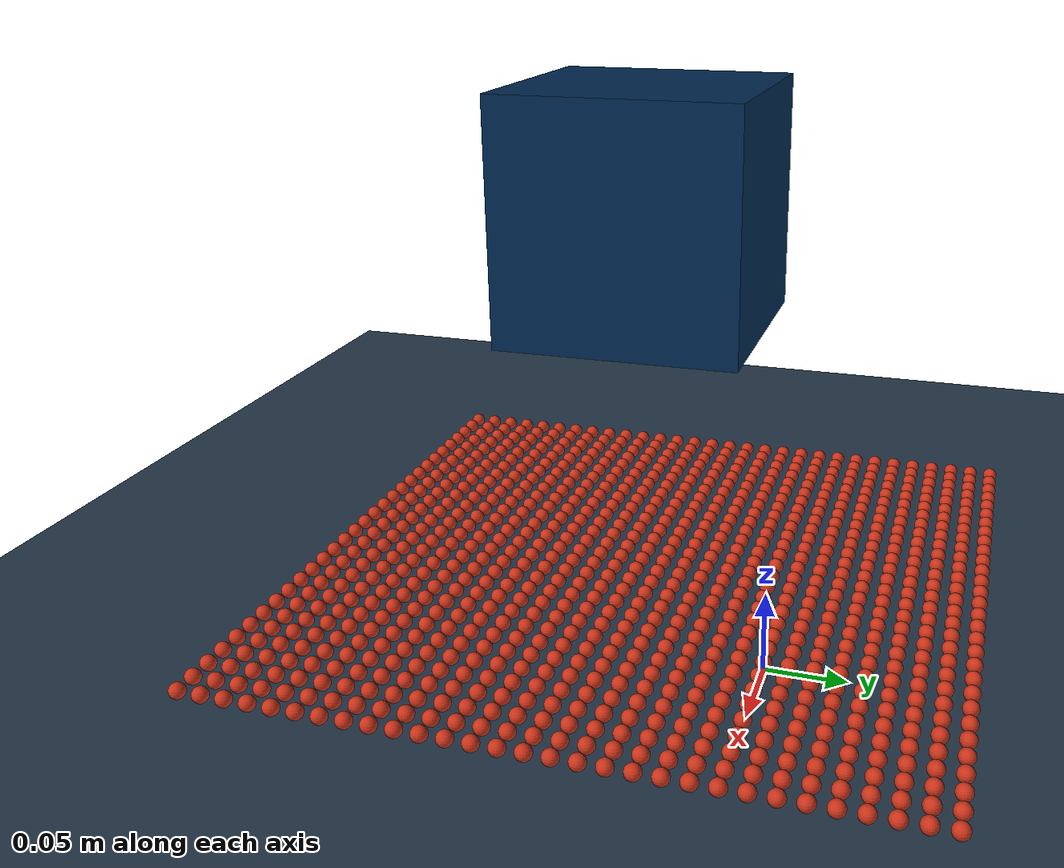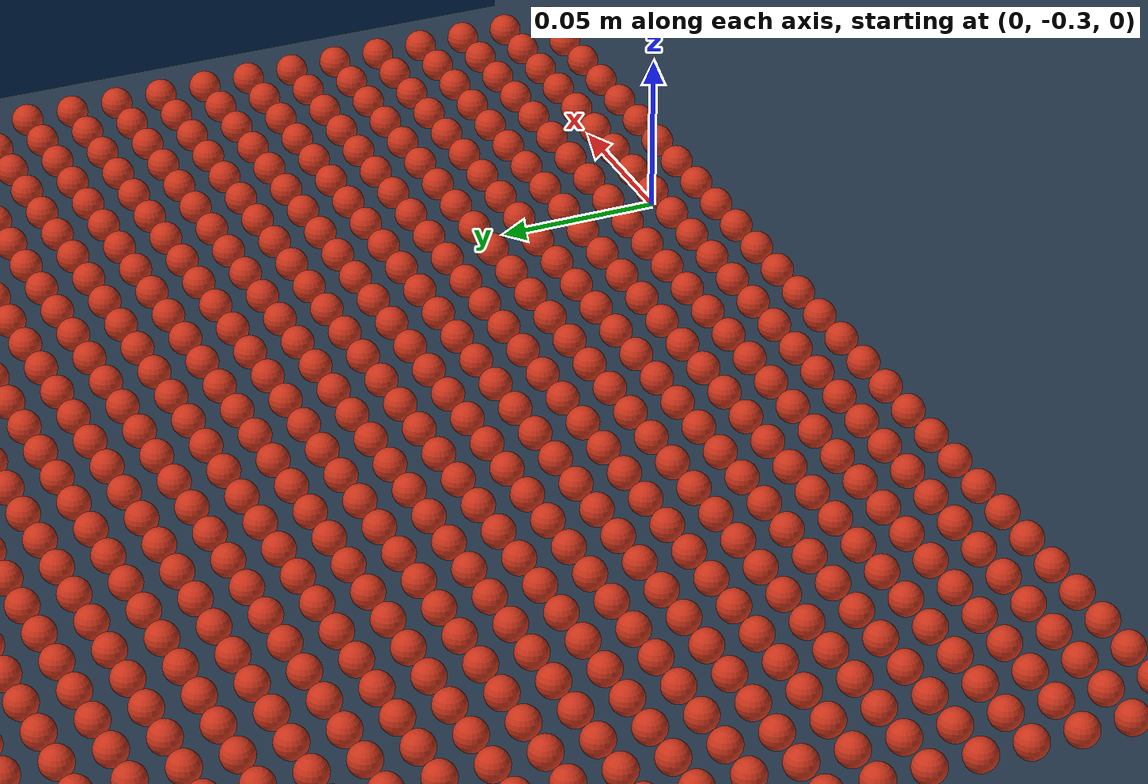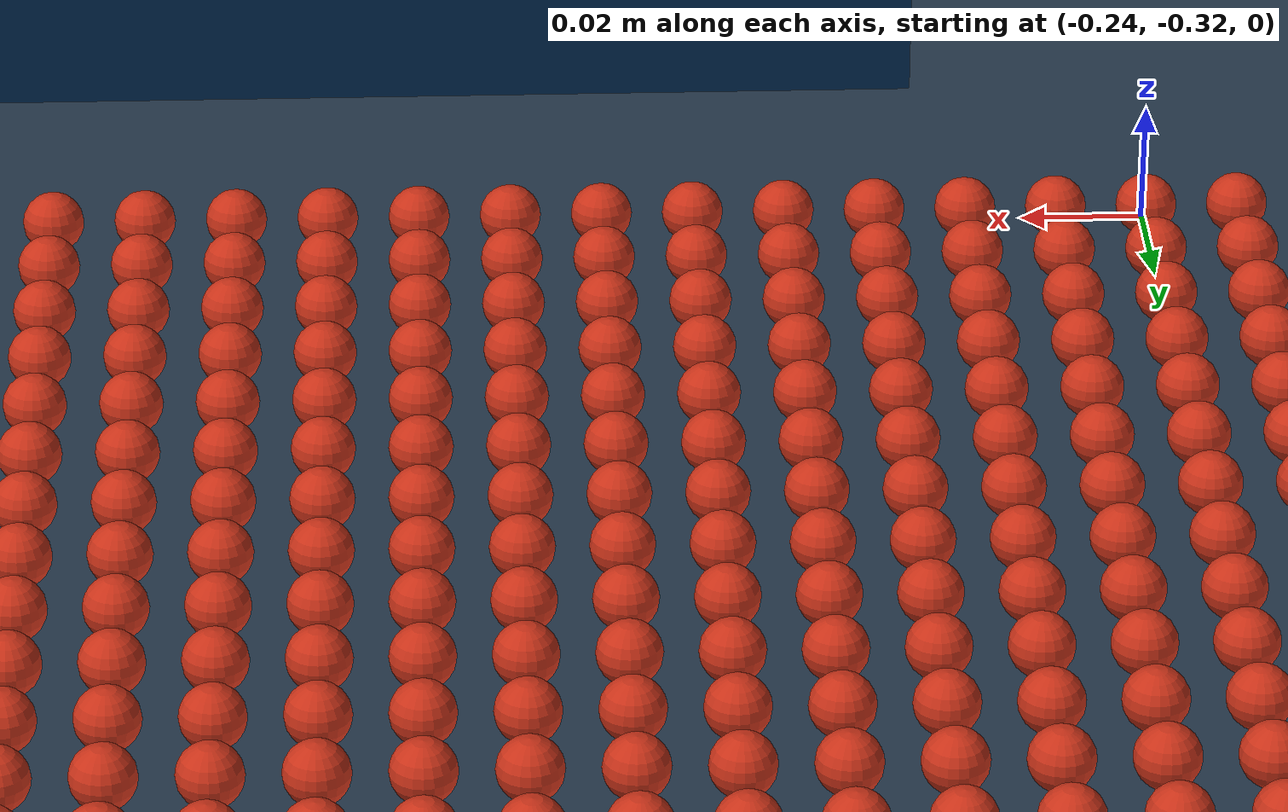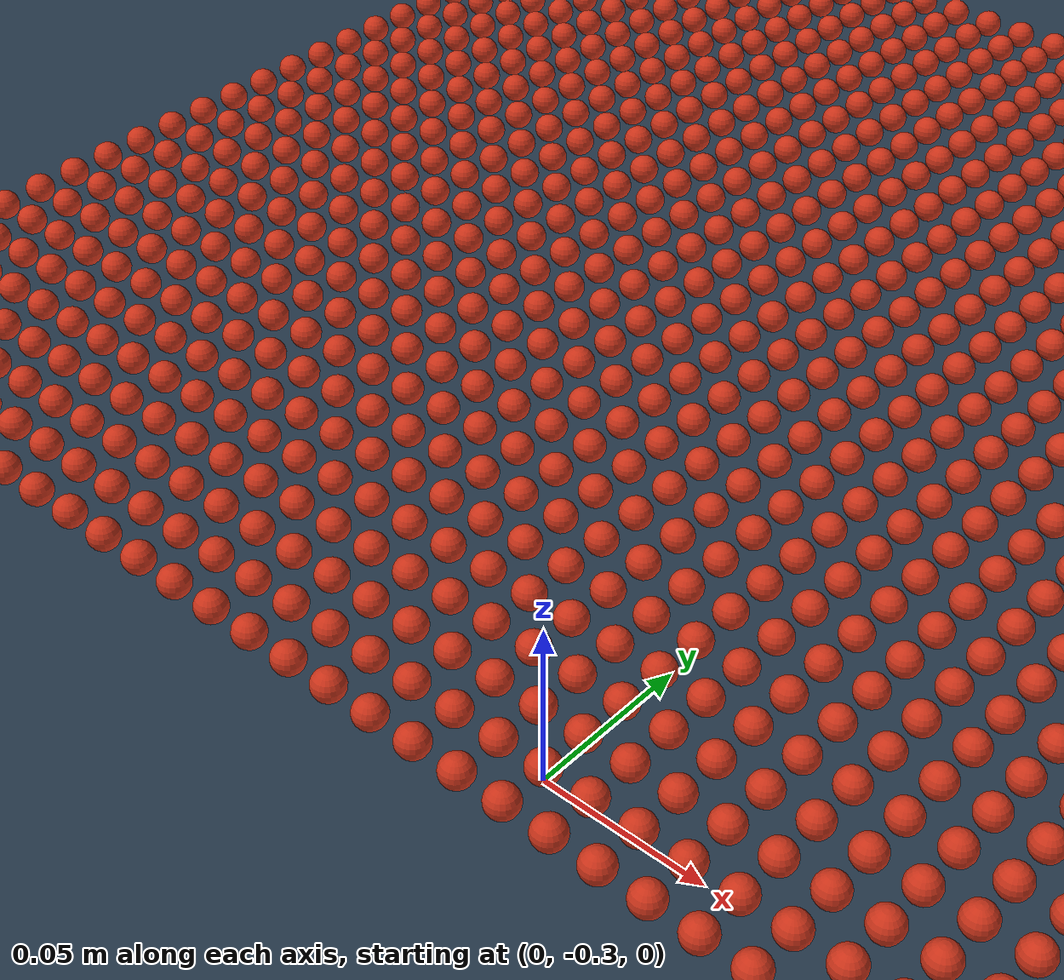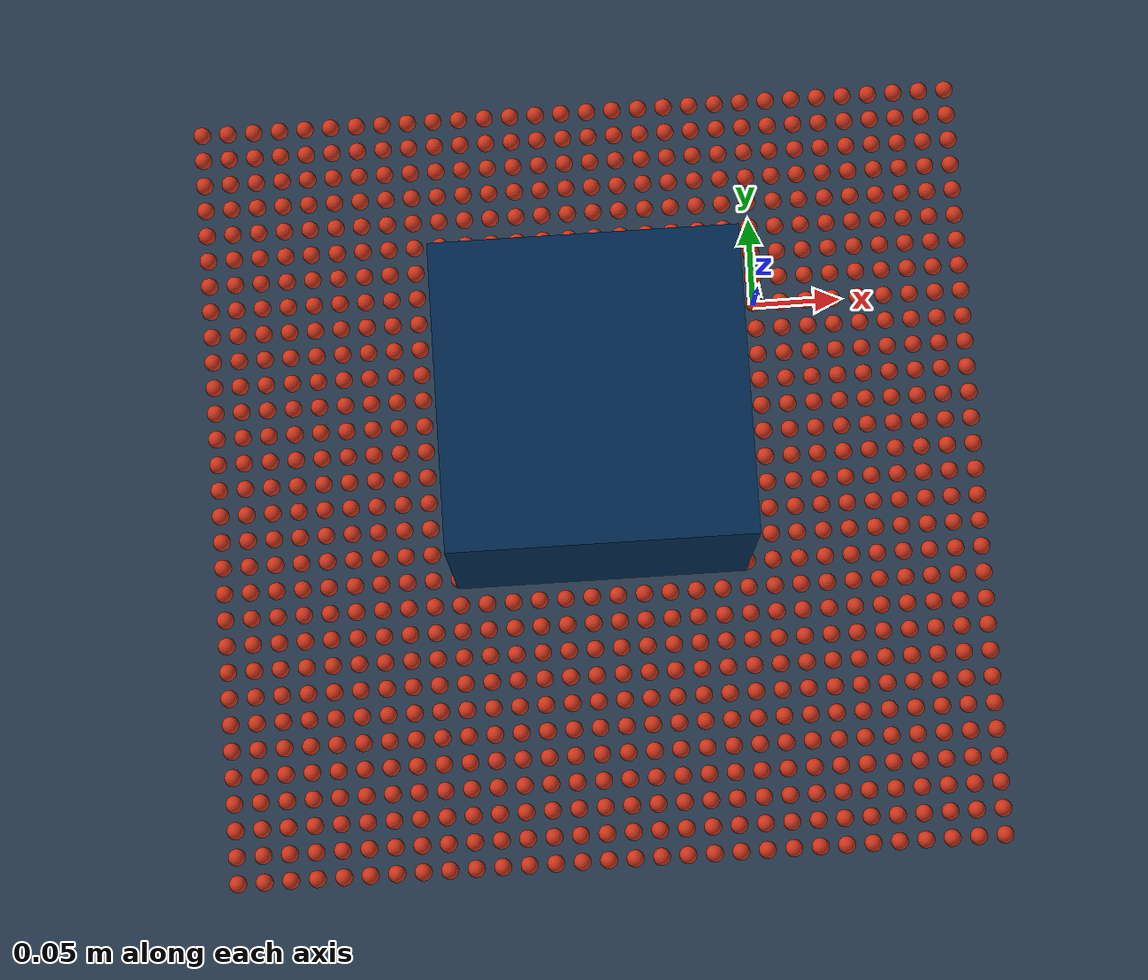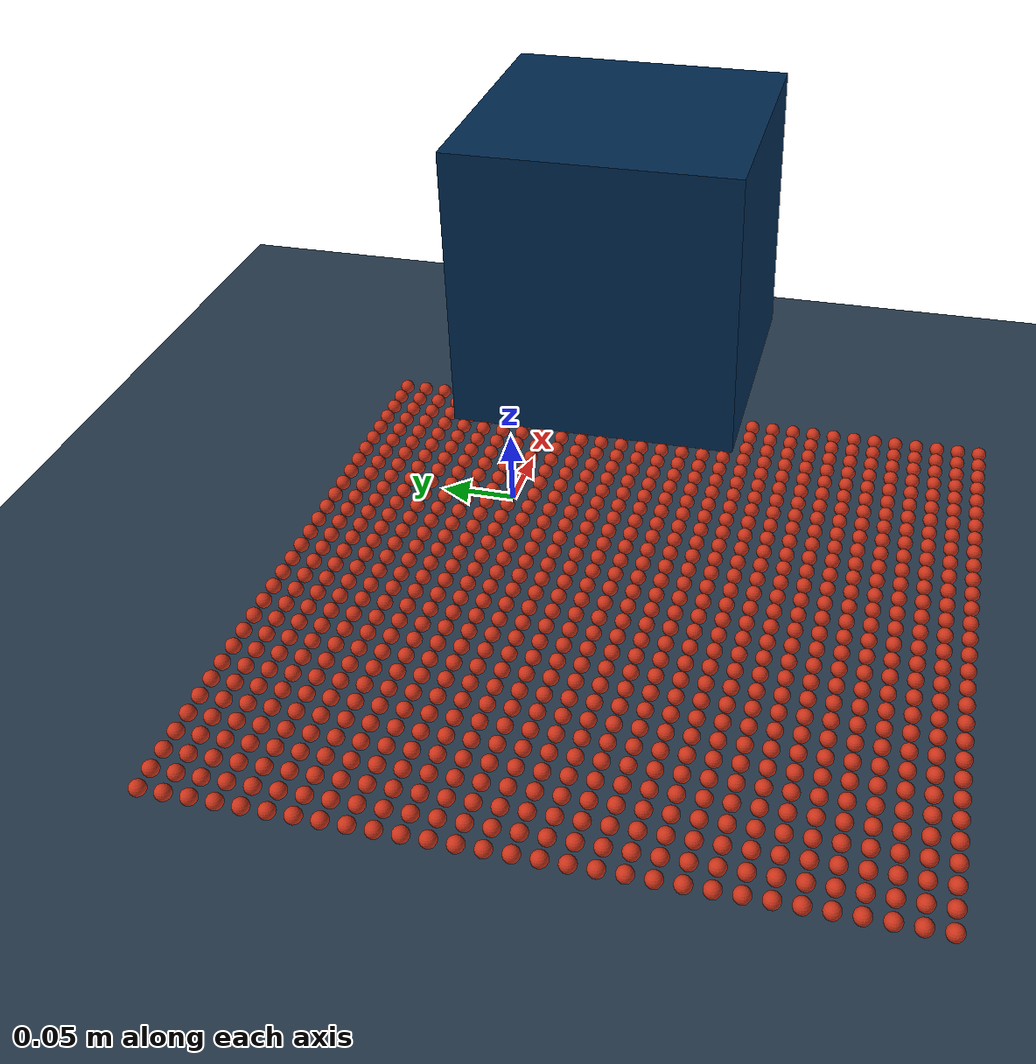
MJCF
<mujoco model="tactile_sleeve">
  <compiler angle="degree"/>
  <option timestep="0.01" cone="elliptic" jacobian="sparse" solver="Newton" iterations="10" tolerance="1e-10">
    <flag gravity="enable"/>
  </option>
  <size njmax="5000" nconmax="10000" nstack="50000"/>
  <visual>
    <map stiffness="100" fogstart="10" fogend="15" zfar="40" shadowscale="0.5"/>
    <scale forcewidth="0.005000000000000001" contactwidth="0.014999999999999999" contactheight="0.005000000000000001" framelength="0.29999999999999999" framewidth="0.029999999999999999"/>
  </visual>
  <default>
    <default class="/"/>
  </default>
  <asset>
    <texture name="texplane" type="2d" builtin="checker" rgb1="0.20000000000000001 0.29999999999999999 0.40000000000000002" rgb2="0.10000000000000001 0.14999999999999999 0.20000000000000001" mark="cross" markrgb="0.80000000000000004 0.80000000000000004 0.80000000000000004" width="512" height="512"/>
    <material name="matplane" class="/" texture="texplane" texuniform="true" reflectance="0.29999999999999999"/>
  </asset>
  <worldbody>
    <geom name="world" class="/" type="plane" condim="1" size="0 0 1" material="matplane"/>
    <light name="//unnamed_light_0" class="/" directional="true" pos="0 0 4" dir="0 0 -1" diffuse="0.59999999999999998 0.59999999999999998 0.59999999999999998" specular="0.20000000000000001 0.20000000000000001 0.20000000000000001"/>
    <site name="taxel_0_0" class="/" type="sphere" rgba="0.80000000000000004 0.20000000000000001 0.10000000000000001 1" size="0.0050000000000000001" pos="0.12 0.12 0.0050000000000000001"/>
    <site name="taxel_0_1" class="/" type="sphere" rgba="0.80000000000000004 0.20000000000000001 0.10000000000000001 1" size="0.0050000000000000001" pos="0.105 0.12 0.0050000000000000001"/>
    <site name="taxel_0_2" class="/" type="sphere" rgba="0.80000000000000004 0.20000000000000001 0.10000000000000001 1" size="0.0050000000000000001" pos="0.089999999999999997 0.12 0.0050000000000000001"/>
    <site name="taxel_0_3" class="/" type="sphere" rgba="0.80000000000000004 0.20000000000000001 0.10000000000000001 1" size="0.0050000000000000001" pos="0.074999999999999997 0.12 0.0050000000000000001"/>
    <site name="taxel_0_4" class="/" type="sphere" rgba="0.80000000000000004 0.20000000000000001 0.10000000000000001 1" size="0.0050000000000000001" pos="0.059999999999999998 0.12 0.0050000000000000001"/>
    <site name="taxel_0_5" class="/" type="sphere" rgba="0.80000000000000004 0.20000000000000001 0.10000000000000001 1" size="0.0050000000000000001" pos="0.044999999999999998 0.12 0.0050000000000000001"/>
    <site name="taxel_0_6" class="/" type="sphere" rgba="0.80000000000000004 0.20000000000000001 0.10000000000000001 1" size="0.0050000000000000001" pos="0.029999999999999999 0.12 0.0050000000000000001"/>
    <site name="taxel_0_7" class="/" type="sphere" rgba="0.80000000000000004 0.20000000000000001 0.10000000000000001 1" size="0.0050000000000000001" pos="0.014999999999999999 0.12 0.0050000000000000001"/>
    <site name="taxel_0_8" class="/" type="sphere" rgba="0.80000000000000004 0.20000000000000001 0.10000000000000001 1" size="0.0050000000000000001" pos="0 0.12 0.0050000000000000001"/>
    <site name="taxel_0_9" class="/" type="sphere" rgba="0.80000000000000004 0.20000000000000001 0.10000000000000001 1" size="0.0050000000000000001" pos="-0.015000000000000013 0.12 0.0050000000000000001"/>
    <site name="taxel_0_10" class="/" type="sphere" rgba="0.80000000000000004 0.20000000000000001 0.10000000000000001 1" size="0.0050000000000000001" pos="-0.030000000000000027 0.12 0.0050000000000000001"/>
    <site name="taxel_0_11" class="/" type="sphere" rgba="0.80000000000000004 0.20000000000000001 0.10000000000000001 1" size="0.0050000000000000001" pos="-0.04500000000000004 0.12 0.0050000000000000001"/>
    <site name="taxel_0_12" class="/" type="sphere" rgba="0.80000000000000004 0.20000000000000001 0.10000000000000001 1" size="0.0050000000000000001" pos="-0.060000000000000053 0.12 0.0050000000000000001"/>
    <site name="taxel_0_13" class="/" type="sphere" rgba="0.80000000000000004 0.20000000000000001 0.10000000000000001 1" size="0.0050000000000000001" pos="-0.075000000000000067 0.12 0.0050000000000000001"/>
    <site name="taxel_0_14" class="/" type="sphere" rgba="0.80000000000000004 0.20000000000000001 0.10000000000000001 1" size="0.0050000000000000001" pos="-0.09000000000000008 0.12 0.0050000000000000001"/>
    <site name="taxel_0_15" class="/" type="sphere" rgba="0.80000000000000004 0.20000000000000001 0.10000000000000001 1" size="0.0050000000000000001" pos="-0.10500000000000009 0.12 0.0050000000000000001"/>
    <site name="taxel_0_16" class="/" type="sphere" rgba="0.80000000000000004 0.20000000000000001 0.10000000000000001 1" size="0.0050000000000000001" pos="-0.12000000000000011 0.12 0.0050000000000000001"/>
    <site name="taxel_0_17" class="/" type="sphere" rgba="0.80000000000000004 0.20000000000000001 0.10000000000000001 1" size="0.0050000000000000001" pos="-0.13500000000000012 0.12 0.0050000000000000001"/>
    <site name="taxel_0_18" class="/" type="sphere" rgba="0.80000000000000004 0.20000000000000001 0.10000000000000001 1" size="0.0050000000000000001" pos="-0.15000000000000013 0.12 0.0050000000000000001"/>
    <site name="taxel_0_19" class="/" type="sphere" rgba="0.80000000000000004 0.20000000000000001 0.10000000000000001 1" size="0.0050000000000000001" pos="-0.16500000000000015 0.12 0.0050000000000000001"/>
    <site name="taxel_0_20" class="/" type="sphere" rgba="0.80000000000000004 0.20000000000000001 0.10000000000000001 1" size="0.0050000000000000001" pos="-0.18000000000000016 0.12 0.0050000000000000001"/>
    <site name="taxel_0_21" class="/" type="sphere" rgba="0.80000000000000004 0.20000000000000001 0.10000000000000001 1" size="0.0050000000000000001" pos="-0.19500000000000017 0.12 0.0050000000000000001"/>
    <site name="taxel_0_22" class="/" type="sphere" rgba="0.80000000000000004 0.20000000000000001 0.10000000000000001 1" size="0.0050000000000000001" pos="-0.21000000000000019 0.12 0.0050000000000000001"/>
    <site name="taxel_0_23" class="/" type="sphere" rgba="0.80000000000000004 0.20000000000000001 0.10000000000000001 1" size="0.0050000000000000001" pos="-0.2250000000000002 0.12 0.0050000000000000001"/>
    <site name="taxel_0_24" class="/" type="sphere" rgba="0.80000000000000004 0.20000000000000001 0.10000000000000001 1" size="0.0050000000000000001" pos="-0.24000000000000021 0.12 0.0050000000000000001"/>
    <site name="taxel_0_25" class="/" type="sphere" rgba="0.80000000000000004 0.20000000000000001 0.10000000000000001 1" size="0.0050000000000000001" pos="-0.25500000000000023 0.12 0.0050000000000000001"/>
    <site name="taxel_0_26" class="/" type="sphere" rgba="0.80000000000000004 0.20000000000000001 0.10000000000000001 1" size="0.0050000000000000001" pos="-0.27000000000000024 0.12 0.0050000000000000001"/>
    <site name="taxel_0_27" class="/" type="sphere" rgba="0.80000000000000004 0.20000000000000001 0.10000000000000001 1" size="0.0050000000000000001" pos="-0.28500000000000025 0.12 0.0050000000000000001"/>
    <site name="taxel_0_28" class="/" type="sphere" rgba="0.80000000000000004 0.20000000000000001 0.10000000000000001 1" size="0.0050000000000000001" pos="-0.30000000000000027 0.12 0.0050000000000000001"/>
    <site name="taxel_0_29" class="/" type="sphere" rgba="0.80000000000000004 0.20000000000000001 0.10000000000000001 1" size="0.0050000000000000001" pos="-0.31500000000000028 0.12 0.0050000000000000001"/>
    <site name="taxel_1_0" class="/" type="sphere" rgba="0.80000000000000004 0.20000000000000001 0.10000000000000001 1" size="0.0050000000000000001" pos="0.12 0.105 0.0050000000000000001"/>
    <site name="taxel_1_1" class="/" type="sphere" rgba="0.80000000000000004 0.20000000000000001 0.10000000000000001 1" size="0.0050000000000000001" pos="0.105 0.105 0.0050000000000000001"/>
    <site name="taxel_1_2" class="/" type="sphere" rgba="0.80000000000000004 0.20000000000000001 0.10000000000000001 1" size="0.0050000000000000001" pos="0.089999999999999997 0.105 0.0050000000000000001"/>
    <site name="taxel_1_3" class="/" type="sphere" rgba="0.80000000000000004 0.20000000000000001 0.10000000000000001 1" size="0.0050000000000000001" pos="0.074999999999999997 0.105 0.0050000000000000001"/>
    <site name="taxel_1_4" class="/" type="sphere" rgba="0.80000000000000004 0.20000000000000001 0.10000000000000001 1" size="0.0050000000000000001" pos="0.059999999999999998 0.105 0.0050000000000000001"/>
    <site name="taxel_1_5" class="/" type="sphere" rgba="0.80000000000000004 0.20000000000000001 0.10000000000000001 1" size="0.0050000000000000001" pos="0.044999999999999998 0.105 0.0050000000000000001"/>
    <site name="taxel_1_6" class="/" type="sphere" rgba="0.80000000000000004 0.20000000000000001 0.10000000000000001 1" size="0.0050000000000000001" pos="0.029999999999999999 0.105 0.0050000000000000001"/>
    <site name="taxel_1_7" class="/" type="sphere" rgba="0.80000000000000004 0.20000000000000001 0.10000000000000001 1" size="0.0050000000000000001" pos="0.014999999999999999 0.105 0.0050000000000000001"/>
    <site name="taxel_1_8" class="/" type="sphere" rgba="0.80000000000000004 0.20000000000000001 0.10000000000000001 1" size="0.0050000000000000001" pos="0 0.105 0.0050000000000000001"/>
    <site name="taxel_1_9" class="/" type="sphere" rgba="0.80000000000000004 0.20000000000000001 0.10000000000000001 1" size="0.0050000000000000001" pos="-0.015000000000000013 0.105 0.0050000000000000001"/>
    <site name="taxel_1_10" class="/" type="sphere" rgba="0.80000000000000004 0.20000000000000001 0.10000000000000001 1" size="0.0050000000000000001" pos="-0.030000000000000027 0.105 0.0050000000000000001"/>
    <site name="taxel_1_11" class="/" type="sphere" rgba="0.80000000000000004 0.20000000000000001 0.10000000000000001 1" size="0.0050000000000000001" pos="-0.04500000000000004 0.105 0.0050000000000000001"/>
    <site name="taxel_1_12" class="/" type="sphere" rgba="0.80000000000000004 0.20000000000000001 0.10000000000000001 1" size="0.0050000000000000001" pos="-0.060000000000000053 0.105 0.0050000000000000001"/>
    <site name="taxel_1_13" class="/" type="sphere" rgba="0.80000000000000004 0.20000000000000001 0.10000000000000001 1" size="0.0050000000000000001" pos="-0.075000000000000067 0.105 0.0050000000000000001"/>
    <site name="taxel_1_14" class="/" type="sphere" rgba="0.80000000000000004 0.20000000000000001 0.10000000000000001 1" size="0.0050000000000000001" pos="-0.09000000000000008 0.105 0.0050000000000000001"/>
    <site name="taxel_1_15" class="/" type="sphere" rgba="0.80000000000000004 0.20000000000000001 0.10000000000000001 1" size="0.0050000000000000001" pos="-0.10500000000000009 0.105 0.0050000000000000001"/>
    <site name="taxel_1_16" class="/" type="sphere" rgba="0.80000000000000004 0.20000000000000001 0.10000000000000001 1" size="0.0050000000000000001" pos="-0.12000000000000011 0.105 0.0050000000000000001"/>
    <site name="taxel_1_17" class="/" type="sphere" rgba="0.80000000000000004 0.20000000000000001 0.10000000000000001 1" size="0.0050000000000000001" pos="-0.13500000000000012 0.105 0.0050000000000000001"/>
    <site name="taxel_1_18" class="/" type="sphere" rgba="0.80000000000000004 0.20000000000000001 0.10000000000000001 1" size="0.0050000000000000001" pos="-0.15000000000000013 0.105 0.0050000000000000001"/>
    <site name="taxel_1_19" class="/" type="sphere" rgba="0.80000000000000004 0.20000000000000001 0.10000000000000001 1" size="0.0050000000000000001" pos="-0.16500000000000015 0.105 0.0050000000000000001"/>
    <site name="taxel_1_20" class="/" type="sphere" rgba="0.80000000000000004 0.20000000000000001 0.10000000000000001 1" size="0.0050000000000000001" pos="-0.18000000000000016 0.105 0.0050000000000000001"/>
    <site name="taxel_1_21" class="/" type="sphere" rgba="0.80000000000000004 0.20000000000000001 0.10000000000000001 1" size="0.0050000000000000001" pos="-0.19500000000000017 0.105 0.0050000000000000001"/>
    <site name="taxel_1_22" class="/" type="sphere" rgba="0.80000000000000004 0.20000000000000001 0.10000000000000001 1" size="0.0050000000000000001" pos="-0.21000000000000019 0.105 0.0050000000000000001"/>
    <site name="taxel_1_23" class="/" type="sphere" rgba="0.80000000000000004 0.20000000000000001 0.10000000000000001 1" size="0.0050000000000000001" pos="-0.2250000000000002 0.105 0.0050000000000000001"/>
    <site name="taxel_1_24" class="/" type="sphere" rgba="0.80000000000000004 0.20000000000000001 0.10000000000000001 1" size="0.0050000000000000001" pos="-0.24000000000000021 0.105 0.0050000000000000001"/>
    <site name="taxel_1_25" class="/" type="sphere" rgba="0.80000000000000004 0.20000000000000001 0.10000000000000001 1" size="0.0050000000000000001" pos="-0.25500000000000023 0.105 0.0050000000000000001"/>
    <site name="taxel_1_26" class="/" type="sphere" rgba="0.80000000000000004 0.20000000000000001 0.10000000000000001 1" size="0.0050000000000000001" pos="-0.27000000000000024 0.105 0.0050000000000000001"/>
    <site name="taxel_1_27" class="/" type="sphere" rgba="0.80000000000000004 0.20000000000000001 0.10000000000000001 1" size="0.0050000000000000001" pos="-0.28500000000000025 0.105 0.0050000000000000001"/>
    <site name="taxel_1_28" class="/" type="sphere" rgba="0.80000000000000004 0.20000000000000001 0.10000000000000001 1" size="0.0050000000000000001" pos="-0.30000000000000027 0.105 0.0050000000000000001"/>
    <site name="taxel_1_29" class="/" type="sphere" rgba="0.80000000000000004 0.20000000000000001 0.10000000000000001 1" size="0.0050000000000000001" pos="-0.31500000000000028 0.105 0.0050000000000000001"/>
    <site name="taxel_2_0" class="/" type="sphere" rgba="0.80000000000000004 0.20000000000000001 0.10000000000000001 1" size="0.0050000000000000001" pos="0.12 0.089999999999999997 0.0050000000000000001"/>
    <site name="taxel_2_1" class="/" type="sphere" rgba="0.80000000000000004 0.20000000000000001 0.10000000000000001 1" size="0.0050000000000000001" pos="0.105 0.089999999999999997 0.0050000000000000001"/>
    <site name="taxel_2_2" class="/" type="sphere" rgba="0.80000000000000004 0.20000000000000001 0.10000000000000001 1" size="0.0050000000000000001" pos="0.089999999999999997 0.089999999999999997 0.0050000000000000001"/>
    <site name="taxel_2_3" class="/" type="sphere" rgba="0.80000000000000004 0.20000000000000001 0.10000000000000001 1" size="0.0050000000000000001" pos="0.074999999999999997 0.089999999999999997 0.0050000000000000001"/>
    <site name="taxel_2_4" class="/" type="sphere" rgba="0.80000000000000004 0.20000000000000001 0.10000000000000001 1" size="0.0050000000000000001" pos="0.059999999999999998 0.089999999999999997 0.0050000000000000001"/>
    <site name="taxel_2_5" class="/" type="sphere" rgba="0.80000000000000004 0.20000000000000001 0.10000000000000001 1" size="0.0050000000000000001" pos="0.044999999999999998 0.089999999999999997 0.0050000000000000001"/>
    <site name="taxel_2_6" class="/" type="sphere" rgba="0.80000000000000004 0.20000000000000001 0.10000000000000001 1" size="0.0050000000000000001" pos="0.029999999999999999 0.089999999999999997 0.0050000000000000001"/>
    <site name="taxel_2_7" class="/" type="sphere" rgba="0.80000000000000004 0.20000000000000001 0.10000000000000001 1" size="0.0050000000000000001" pos="0.014999999999999999 0.089999999999999997 0.0050000000000000001"/>
    <site name="taxel_2_8" class="/" type="sphere" rgba="0.80000000000000004 0.20000000000000001 0.10000000000000001 1" size="0.0050000000000000001" pos="0 0.089999999999999997 0.0050000000000000001"/>
    <site name="taxel_2_9" class="/" type="sphere" rgba="0.80000000000000004 0.20000000000000001 0.10000000000000001 1" size="0.0050000000000000001" pos="-0.015000000000000013 0.089999999999999997 0.0050000000000000001"/>
    <site name="taxel_2_10" class="/" type="sphere" rgba="0.80000000000000004 0.20000000000000001 0.10000000000000001 1" size="0.0050000000000000001" pos="-0.030000000000000027 0.089999999999999997 0.0050000000000000001"/>
    <site name="taxel_2_11" class="/" type="sphere" rgba="0.80000000000000004 0.20000000000000001 0.10000000000000001 1" size="0.0050000000000000001" pos="-0.04500000000000004 0.089999999999999997 0.0050000000000000001"/>
    <site name="taxel_2_12" class="/" type="sphere" rgba="0.80000000000000004 0.20000000000000001 0.10000000000000001 1" size="0.0050000000000000001" pos="-0.060000000000000053 0.089999999999999997 0.0050000000000000001"/>
    <site name="taxel_2_13" class="/" type="sphere" rgba="0.80000000000000004 0.20000000000000001 0.10000000000000001 1" size="0.0050000000000000001" pos="-0.075000000000000067 0.089999999999999997 0.0050000000000000001"/>
    <site name="taxel_2_14" class="/" type="sphere" rgba="0.80000000000000004 0.20000000000000001 0.10000000000000001 1" size="0.0050000000000000001" pos="-0.09000000000000008 0.089999999999999997 0.0050000000000000001"/>
    <site name="taxel_2_15" class="/" type="sphere" rgba="0.80000000000000004 0.20000000000000001 0.10000000000000001 1" size="0.0050000000000000001" pos="-0.10500000000000009 0.089999999999999997 0.0050000000000000001"/>
    <site name="taxel_2_16" class="/" type="sphere" rgba="0.80000000000000004 0.20000000000000001 0.10000000000000001 1" size="0.0050000000000000001" pos="-0.12000000000000011 0.089999999999999997 0.0050000000000000001"/>
    <site name="taxel_2_17" class="/" type="sphere" rgba="0.80000000000000004 0.20000000000000001 0.10000000000000001 1" size="0.0050000000000000001" pos="-0.13500000000000012 0.089999999999999997 0.0050000000000000001"/>
    <site name="taxel_2_18" class="/" type="sphere" rgba="0.80000000000000004 0.20000000000000001 0.10000000000000001 1" size="0.0050000000000000001" pos="-0.15000000000000013 0.089999999999999997 0.0050000000000000001"/>
    <site name="taxel_2_19" class="/" type="sphere" rgba="0.80000000000000004 0.20000000000000001 0.10000000000000001 1" size="0.0050000000000000001" pos="-0.16500000000000015 0.089999999999999997 0.0050000000000000001"/>
    <site name="taxel_2_20" class="/" type="sphere" rgba="0.80000000000000004 0.20000000000000001 0.10000000000000001 1" size="0.0050000000000000001" pos="-0.18000000000000016 0.089999999999999997 0.0050000000000000001"/>
    <site name="taxel_2_21" class="/" type="sphere" rgba="0.80000000000000004 0.20000000000000001 0.10000000000000001 1" size="0.0050000000000000001" pos="-0.19500000000000017 0.089999999999999997 0.0050000000000000001"/>
    <site name="taxel_2_22" class="/" type="sphere" rgba="0.80000000000000004 0.20000000000000001 0.10000000000000001 1" size="0.0050000000000000001" pos="-0.21000000000000019 0.089999999999999997 0.0050000000000000001"/>
    <site name="taxel_2_23" class="/" type="sphere" rgba="0.80000000000000004 0.20000000000000001 0.10000000000000001 1" size="0.0050000000000000001" pos="-0.2250000000000002 0.089999999999999997 0.0050000000000000001"/>
    <site name="taxel_2_24" class="/" type="sphere" rgba="0.80000000000000004 0.20000000000000001 0.10000000000000001 1" size="0.0050000000000000001" pos="-0.24000000000000021 0.089999999999999997 0.0050000000000000001"/>
    <site name="taxel_2_25" class="/" type="sphere" rgba="0.80000000000000004 0.20000000000000001 0.10000000000000001 1" size="0.0050000000000000001" pos="-0.25500000000000023 0.089999999999999997 0.0050000000000000001"/>
    <site name="taxel_2_26" class="/" type="sphere" rgba="0.80000000000000004 0.20000000000000001 0.10000000000000001 1" size="0.0050000000000000001" pos="-0.27000000000000024 0.089999999999999997 0.0050000000000000001"/>
    <site name="taxel_2_27" class="/" type="sphere" rgba="0.80000000000000004 0.20000000000000001 0.10000000000000001 1" size="0.0050000000000000001" pos="-0.28500000000000025 0.089999999999999997 0.0050000000000000001"/>
    <site name="taxel_2_28" class="/" type="sphere" rgba="0.80000000000000004 0.20000000000000001 0.10000000000000001 1" size="0.0050000000000000001" pos="-0.30000000000000027 0.089999999999999997 0.0050000000000000001"/>
    <site name="taxel_2_29" class="/" type="sphere" rgba="0.80000000000000004 0.20000000000000001 0.10000000000000001 1" size="0.0050000000000000001" pos="-0.31500000000000028 0.089999999999999997 0.0050000000000000001"/>
    <site name="taxel_3_0" class="/" type="sphere" rgba="0.80000000000000004 0.20000000000000001 0.10000000000000001 1" size="0.0050000000000000001" pos="0.12 0.074999999999999997 0.0050000000000000001"/>
    <site name="taxel_3_1" class="/" type="sphere" rgba="0.80000000000000004 0.20000000000000001 0.10000000000000001 1" size="0.0050000000000000001" pos="0.105 0.074999999999999997 0.0050000000000000001"/>
    <site name="taxel_3_2" class="/" type="sphere" rgba="0.80000000000000004 0.20000000000000001 0.10000000000000001 1" size="0.0050000000000000001" pos="0.089999999999999997 0.074999999999999997 0.0050000000000000001"/>
    <site name="taxel_3_3" class="/" type="sphere" rgba="0.80000000000000004 0.20000000000000001 0.10000000000000001 1" size="0.0050000000000000001" pos="0.074999999999999997 0.074999999999999997 0.0050000000000000001"/>
    <site name="taxel_3_4" class="/" type="sphere" rgba="0.80000000000000004 0.20000000000000001 0.10000000000000001 1" size="0.0050000000000000001" pos="0.059999999999999998 0.074999999999999997 0.0050000000000000001"/>
    <site name="taxel_3_5" class="/" type="sphere" rgba="0.80000000000000004 0.20000000000000001 0.10000000000000001 1" size="0.0050000000000000001" pos="0.044999999999999998 0.074999999999999997 0.0050000000000000001"/>
    <site name="taxel_3_6" class="/" type="sphere" rgba="0.80000000000000004 0.20000000000000001 0.10000000000000001 1" size="0.0050000000000000001" pos="0.029999999999999999 0.074999999999999997 0.0050000000000000001"/>
    <site name="taxel_3_7" class="/" type="sphere" rgba="0.80000000000000004 0.20000000000000001 0.10000000000000001 1" size="0.0050000000000000001" pos="0.014999999999999999 0.074999999999999997 0.0050000000000000001"/>
    <site name="taxel_3_8" class="/" type="sphere" rgba="0.80000000000000004 0.20000000000000001 0.10000000000000001 1" size="0.0050000000000000001" pos="0 0.074999999999999997 0.0050000000000000001"/>
    <site name="taxel_3_9" class="/" type="sphere" rgba="0.80000000000000004 0.20000000000000001 0.10000000000000001 1" size="0.0050000000000000001" pos="-0.015000000000000013 0.074999999999999997 0.0050000000000000001"/>
    <site name="taxel_3_10" class="/" type="sphere" rgba="0.80000000000000004 0.20000000000000001 0.10000000000000001 1" size="0.0050000000000000001" pos="-0.030000000000000027 0.074999999999999997 0.0050000000000000001"/>
    <site name="taxel_3_11" class="/" type="sphere" rgba="0.80000000000000004 0.20000000000000001 0.10000000000000001 1" size="0.0050000000000000001" pos="-0.04500000000000004 0.074999999999999997 0.0050000000000000001"/>
    <site name="taxel_3_12" class="/" type="sphere" rgba="0.80000000000000004 0.20000000000000001 0.10000000000000001 1" size="0.0050000000000000001" pos="-0.060000000000000053 0.074999999999999997 0.0050000000000000001"/>
    <site name="taxel_3_13" class="/" type="sphere" rgba="0.80000000000000004 0.20000000000000001 0.10000000000000001 1" size="0.0050000000000000001" pos="-0.075000000000000067 0.074999999999999997 0.0050000000000000001"/>
    <site name="taxel_3_14" class="/" type="sphere" rgba="0.80000000000000004 0.20000000000000001 0.10000000000000001 1" size="0.0050000000000000001" pos="-0.09000000000000008 0.074999999999999997 0.0050000000000000001"/>
    <site name="taxel_3_15" class="/" type="sphere" rgba="0.80000000000000004 0.20000000000000001 0.10000000000000001 1" size="0.0050000000000000001" pos="-0.10500000000000009 0.074999999999999997 0.0050000000000000001"/>
    <site name="taxel_3_16" class="/" type="sphere" rgba="0.80000000000000004 0.20000000000000001 0.10000000000000001 1" size="0.0050000000000000001" pos="-0.12000000000000011 0.074999999999999997 0.0050000000000000001"/>
    <site name="taxel_3_17" class="/" type="sphere" rgba="0.80000000000000004 0.20000000000000001 0.10000000000000001 1" size="0.0050000000000000001" pos="-0.13500000000000012 0.074999999999999997 0.0050000000000000001"/>
    <site name="taxel_3_18" class="/" type="sphere" rgba="0.80000000000000004 0.20000000000000001 0.10000000000000001 1" size="0.0050000000000000001" pos="-0.15000000000000013 0.074999999999999997 0.0050000000000000001"/>
    <site name="taxel_3_19" class="/" type="sphere" rgba="0.80000000000000004 0.20000000000000001 0.10000000000000001 1" size="0.0050000000000000001" pos="-0.16500000000000015 0.074999999999999997 0.0050000000000000001"/>
    <site name="taxel_3_20" class="/" type="sphere" rgba="0.80000000000000004 0.20000000000000001 0.10000000000000001 1" size="0.0050000000000000001" pos="-0.18000000000000016 0.074999999999999997 0.0050000000000000001"/>
    <site name="taxel_3_21" class="/" type="sphere" rgba="0.80000000000000004 0.20000000000000001 0.10000000000000001 1" size="0.0050000000000000001" pos="-0.19500000000000017 0.074999999999999997 0.0050000000000000001"/>
    <site name="taxel_3_22" class="/" type="sphere" rgba="0.80000000000000004 0.20000000000000001 0.10000000000000001 1" size="0.0050000000000000001" pos="-0.21000000000000019 0.074999999999999997 0.0050000000000000001"/>
    <site name="taxel_3_23" class="/" type="sphere" rgba="0.80000000000000004 0.20000000000000001 0.10000000000000001 1" size="0.0050000000000000001" pos="-0.2250000000000002 0.074999999999999997 0.0050000000000000001"/>
    <site name="taxel_3_24" class="/" type="sphere" rgba="0.80000000000000004 0.20000000000000001 0.10000000000000001 1" size="0.0050000000000000001" pos="-0.24000000000000021 0.074999999999999997 0.0050000000000000001"/>
    <site name="taxel_3_25" class="/" type="sphere" rgba="0.80000000000000004 0.20000000000000001 0.10000000000000001 1" size="0.0050000000000000001" pos="-0.25500000000000023 0.074999999999999997 0.0050000000000000001"/>
    <site name="taxel_3_26" class="/" type="sphere" rgba="0.80000000000000004 0.20000000000000001 0.10000000000000001 1" size="0.0050000000000000001" pos="-0.27000000000000024 0.074999999999999997 0.0050000000000000001"/>
    <site name="taxel_3_27" class="/" type="sphere" rgba="0.80000000000000004 0.20000000000000001 0.10000000000000001 1" size="0.0050000000000000001" pos="-0.28500000000000025 0.074999999999999997 0.0050000000000000001"/>
    <site name="taxel_3_28" class="/" type="sphere" rgba="0.80000000000000004 0.20000000000000001 0.10000000000000001 1" size="0.0050000000000000001" pos="-0.30000000000000027 0.074999999999999997 0.0050000000000000001"/>
    <site name="taxel_3_29" class="/" type="sphere" rgba="0.80000000000000004 0.20000000000000001 0.10000000000000001 1" size="0.0050000000000000001" pos="-0.31500000000000028 0.074999999999999997 0.0050000000000000001"/>
    <site name="taxel_4_0" class="/" type="sphere" rgba="0.80000000000000004 0.20000000000000001 0.10000000000000001 1" size="0.0050000000000000001" pos="0.12 0.059999999999999998 0.0050000000000000001"/>
    <site name="taxel_4_1" class="/" type="sphere" rgba="0.80000000000000004 0.20000000000000001 0.10000000000000001 1" size="0.0050000000000000001" pos="0.105 0.059999999999999998 0.0050000000000000001"/>
    <site name="taxel_4_2" class="/" type="sphere" rgba="0.80000000000000004 0.20000000000000001 0.10000000000000001 1" size="0.0050000000000000001" pos="0.089999999999999997 0.059999999999999998 0.0050000000000000001"/>
    <site name="taxel_4_3" class="/" type="sphere" rgba="0.80000000000000004 0.20000000000000001 0.10000000000000001 1" size="0.0050000000000000001" pos="0.074999999999999997 0.059999999999999998 0.0050000000000000001"/>
    <site name="taxel_4_4" class="/" type="sphere" rgba="0.80000000000000004 0.20000000000000001 0.10000000000000001 1" size="0.0050000000000000001" pos="0.059999999999999998 0.059999999999999998 0.0050000000000000001"/>
    <site name="taxel_4_5" class="/" type="sphere" rgba="0.80000000000000004 0.20000000000000001 0.10000000000000001 1" size="0.0050000000000000001" pos="0.044999999999999998 0.059999999999999998 0.0050000000000000001"/>
    <site name="taxel_4_6" class="/" type="sphere" rgba="0.80000000000000004 0.20000000000000001 0.10000000000000001 1" size="0.0050000000000000001" pos="0.029999999999999999 0.059999999999999998 0.0050000000000000001"/>
    <site name="taxel_4_7" class="/" type="sphere" rgba="0.80000000000000004 0.20000000000000001 0.10000000000000001 1" size="0.0050000000000000001" pos="0.014999999999999999 0.059999999999999998 0.0050000000000000001"/>
    <site name="taxel_4_8" class="/" type="sphere" rgba="0.80000000000000004 0.20000000000000001 0.10000000000000001 1" size="0.0050000000000000001" pos="0 0.059999999999999998 0.0050000000000000001"/>
    <site name="taxel_4_9" class="/" type="sphere" rgba="0.80000000000000004 0.20000000000000001 0.10000000000000001 1" size="0.0050000000000000001" pos="-0.015000000000000013 0.059999999999999998 0.0050000000000000001"/>
    <site name="taxel_4_10" class="/" type="sphere" rgba="0.80000000000000004 0.20000000000000001 0.10000000000000001 1" size="0.0050000000000000001" pos="-0.030000000000000027 0.059999999999999998 0.0050000000000000001"/>
    <site name="taxel_4_11" class="/" type="sphere" rgba="0.80000000000000004 0.20000000000000001 0.10000000000000001 1" size="0.0050000000000000001" pos="-0.04500000000000004 0.059999999999999998 0.0050000000000000001"/>
    <site name="taxel_4_12" class="/" type="sphere" rgba="0.80000000000000004 0.20000000000000001 0.10000000000000001 1" size="0.0050000000000000001" pos="-0.060000000000000053 0.059999999999999998 0.0050000000000000001"/>
    <site name="taxel_4_13" class="/" type="sphere" rgba="0.80000000000000004 0.20000000000000001 0.10000000000000001 1" size="0.0050000000000000001" pos="-0.075000000000000067 0.059999999999999998 0.0050000000000000001"/>
    <site name="taxel_4_14" class="/" type="sphere" rgba="0.80000000000000004 0.20000000000000001 0.10000000000000001 1" size="0.0050000000000000001" pos="-0.09000000000000008 0.059999999999999998 0.0050000000000000001"/>
    <site name="taxel_4_15" class="/" type="sphere" rgba="0.80000000000000004 0.20000000000000001 0.10000000000000001 1" size="0.0050000000000000001" pos="-0.10500000000000009 0.059999999999999998 0.0050000000000000001"/>
    <site name="taxel_4_16" class="/" type="sphere" rgba="0.80000000000000004 0.20000000000000001 0.10000000000000001 1" size="0.0050000000000000001" pos="-0.12000000000000011 0.059999999999999998 0.0050000000000000001"/>
    <site name="taxel_4_17" class="/" type="sphere" rgba="0.80000000000000004 0.20000000000000001 0.10000000000000001 1" size="0.0050000000000000001" pos="-0.13500000000000012 0.059999999999999998 0.0050000000000000001"/>
    <site name="taxel_4_18" class="/" type="sphere" rgba="0.80000000000000004 0.20000000000000001 0.10000000000000001 1" size="0.0050000000000000001" pos="-0.15000000000000013 0.059999999999999998 0.0050000000000000001"/>
    <site name="taxel_4_19" class="/" type="sphere" rgba="0.80000000000000004 0.20000000000000001 0.10000000000000001 1" size="0.0050000000000000001" pos="-0.16500000000000015 0.059999999999999998 0.0050000000000000001"/>
    <site name="taxel_4_20" class="/" type="sphere" rgba="0.80000000000000004 0.20000000000000001 0.10000000000000001 1" size="0.0050000000000000001" pos="-0.18000000000000016 0.059999999999999998 0.0050000000000000001"/>
    <site name="taxel_4_21" class="/" type="sphere" rgba="0.80000000000000004 0.20000000000000001 0.10000000000000001 1" size="0.0050000000000000001" pos="-0.19500000000000017 0.059999999999999998 0.0050000000000000001"/>
    <site name="taxel_4_22" class="/" type="sphere" rgba="0.80000000000000004 0.20000000000000001 0.10000000000000001 1" size="0.0050000000000000001" pos="-0.21000000000000019 0.059999999999999998 0.0050000000000000001"/>
    <site name="taxel_4_23" class="/" type="sphere" rgba="0.80000000000000004 0.20000000000000001 0.10000000000000001 1" size="0.0050000000000000001" pos="-0.2250000000000002 0.059999999999999998 0.0050000000000000001"/>
    <site name="taxel_4_24" class="/" type="sphere" rgba="0.80000000000000004 0.20000000000000001 0.10000000000000001 1" size="0.0050000000000000001" pos="-0.24000000000000021 0.059999999999999998 0.0050000000000000001"/>
    <site name="taxel_4_25" class="/" type="sphere" rgba="0.80000000000000004 0.20000000000000001 0.10000000000000001 1" size="0.0050000000000000001" pos="-0.25500000000000023 0.059999999999999998 0.0050000000000000001"/>
    <site name="taxel_4_26" class="/" type="sphere" rgba="0.80000000000000004 0.20000000000000001 0.10000000000000001 1" size="0.0050000000000000001" pos="-0.27000000000000024 0.059999999999999998 0.0050000000000000001"/>
    <site name="taxel_4_27" class="/" type="sphere" rgba="0.80000000000000004 0.20000000000000001 0.10000000000000001 1" size="0.0050000000000000001" pos="-0.28500000000000025 0.059999999999999998 0.0050000000000000001"/>
    <site name="taxel_4_28" class="/" type="sphere" rgba="0.80000000000000004 0.20000000000000001 0.10000000000000001 1" size="0.0050000000000000001" pos="-0.30000000000000027 0.059999999999999998 0.0050000000000000001"/>
    <site name="taxel_4_29" class="/" type="sphere" rgba="0.80000000000000004 0.20000000000000001 0.10000000000000001 1" size="0.0050000000000000001" pos="-0.31500000000000028 0.059999999999999998 0.0050000000000000001"/>
    <site name="taxel_5_0" class="/" type="sphere" rgba="0.80000000000000004 0.20000000000000001 0.10000000000000001 1" size="0.0050000000000000001" pos="0.12 0.044999999999999998 0.0050000000000000001"/>
    <site name="taxel_5_1" class="/" type="sphere" rgba="0.80000000000000004 0.20000000000000001 0.10000000000000001 1" size="0.0050000000000000001" pos="0.105 0.044999999999999998 0.0050000000000000001"/>
    <site name="taxel_5_2" class="/" type="sphere" rgba="0.80000000000000004 0.20000000000000001 0.10000000000000001 1" size="0.0050000000000000001" pos="0.089999999999999997 0.044999999999999998 0.0050000000000000001"/>
    <site name="taxel_5_3" class="/" type="sphere" rgba="0.80000000000000004 0.20000000000000001 0.10000000000000001 1" size="0.0050000000000000001" pos="0.074999999999999997 0.044999999999999998 0.0050000000000000001"/>
    <site name="taxel_5_4" class="/" type="sphere" rgba="0.80000000000000004 0.20000000000000001 0.10000000000000001 1" size="0.0050000000000000001" pos="0.059999999999999998 0.044999999999999998 0.0050000000000000001"/>
    <site name="taxel_5_5" class="/" type="sphere" rgba="0.80000000000000004 0.20000000000000001 0.10000000000000001 1" size="0.0050000000000000001" pos="0.044999999999999998 0.044999999999999998 0.0050000000000000001"/>
    <site name="taxel_5_6" class="/" type="sphere" rgba="0.80000000000000004 0.20000000000000001 0.10000000000000001 1" size="0.0050000000000000001" pos="0.029999999999999999 0.044999999999999998 0.0050000000000000001"/>
    <site name="taxel_5_7" class="/" type="sphere" rgba="0.80000000000000004 0.20000000000000001 0.10000000000000001 1" size="0.0050000000000000001" pos="0.014999999999999999 0.044999999999999998 0.0050000000000000001"/>
    <site name="taxel_5_8" class="/" type="sphere" rgba="0.80000000000000004 0.20000000000000001 0.10000000000000001 1" size="0.0050000000000000001" pos="0 0.044999999999999998 0.0050000000000000001"/>
    <site name="taxel_5_9" class="/" type="sphere" rgba="0.80000000000000004 0.20000000000000001 0.10000000000000001 1" size="0.0050000000000000001" pos="-0.015000000000000013 0.044999999999999998 0.0050000000000000001"/>
    <site name="taxel_5_10" class="/" type="sphere" rgba="0.80000000000000004 0.20000000000000001 0.10000000000000001 1" size="0.0050000000000000001" pos="-0.030000000000000027 0.044999999999999998 0.0050000000000000001"/>
    <site name="taxel_5_11" class="/" type="sphere" rgba="0.80000000000000004 0.20000000000000001 0.10000000000000001 1" size="0.0050000000000000001" pos="-0.04500000000000004 0.044999999999999998 0.0050000000000000001"/>
    <site name="taxel_5_12" class="/" type="sphere" rgba="0.80000000000000004 0.20000000000000001 0.10000000000000001 1" size="0.0050000000000000001" pos="-0.060000000000000053 0.044999999999999998 0.0050000000000000001"/>
    <site name="taxel_5_13" class="/" type="sphere" rgba="0.80000000000000004 0.20000000000000001 0.10000000000000001 1" size="0.0050000000000000001" pos="-0.075000000000000067 0.044999999999999998 0.0050000000000000001"/>
    <site name="taxel_5_14" class="/" type="sphere" rgba="0.80000000000000004 0.20000000000000001 0.10000000000000001 1" size="0.0050000000000000001" pos="-0.09000000000000008 0.044999999999999998 0.0050000000000000001"/>
    <site name="taxel_5_15" class="/" type="sphere" rgba="0.80000000000000004 0.20000000000000001 0.10000000000000001 1" size="0.0050000000000000001" pos="-0.10500000000000009 0.044999999999999998 0.0050000000000000001"/>
    <site name="taxel_5_16" class="/" type="sphere" rgba="0.80000000000000004 0.20000000000000001 0.10000000000000001 1" size="0.0050000000000000001" pos="-0.12000000000000011 0.044999999999999998 0.0050000000000000001"/>
    <site name="taxel_5_17" class="/" type="sphere" rgba="0.80000000000000004 0.20000000000000001 0.10000000000000001 1" size="0.0050000000000000001" pos="-0.13500000000000012 0.044999999999999998 0.0050000000000000001"/>
    <site name="taxel_5_18" class="/" type="sphere" rgba="0.80000000000000004 0.20000000000000001 0.10000000000000001 1" size="0.0050000000000000001" pos="-0.15000000000000013 0.044999999999999998 0.0050000000000000001"/>
    <site name="taxel_5_19" class="/" type="sphere" rgba="0.80000000000000004 0.20000000000000001 0.10000000000000001 1" size="0.0050000000000000001" pos="-0.16500000000000015 0.044999999999999998 0.0050000000000000001"/>
    <site name="taxel_5_20" class="/" type="sphere" rgba="0.80000000000000004 0.20000000000000001 0.10000000000000001 1" size="0.0050000000000000001" pos="-0.18000000000000016 0.044999999999999998 0.0050000000000000001"/>
    <site name="taxel_5_21" class="/" type="sphere" rgba="0.80000000000000004 0.20000000000000001 0.10000000000000001 1" size="0.0050000000000000001" pos="-0.19500000000000017 0.044999999999999998 0.0050000000000000001"/>
    <site name="taxel_5_22" class="/" type="sphere" rgba="0.80000000000000004 0.20000000000000001 0.10000000000000001 1" size="0.0050000000000000001" pos="-0.21000000000000019 0.044999999999999998 0.0050000000000000001"/>
    <site name="taxel_5_23" class="/" type="sphere" rgba="0.80000000000000004 0.20000000000000001 0.10000000000000001 1" size="0.0050000000000000001" pos="-0.2250000000000002 0.044999999999999998 0.0050000000000000001"/>
    <site name="taxel_5_24" class="/" type="sphere" rgba="0.80000000000000004 0.20000000000000001 0.10000000000000001 1" size="0.0050000000000000001" pos="-0.24000000000000021 0.044999999999999998 0.0050000000000000001"/>
    <site name="taxel_5_25" class="/" type="sphere" rgba="0.80000000000000004 0.20000000000000001 0.10000000000000001 1" size="0.0050000000000000001" pos="-0.25500000000000023 0.044999999999999998 0.0050000000000000001"/>
    <site name="taxel_5_26" class="/" type="sphere" rgba="0.80000000000000004 0.20000000000000001 0.10000000000000001 1" size="0.0050000000000000001" pos="-0.27000000000000024 0.044999999999999998 0.0050000000000000001"/>
    <site name="taxel_5_27" class="/" type="sphere" rgba="0.80000000000000004 0.20000000000000001 0.10000000000000001 1" size="0.0050000000000000001" pos="-0.28500000000000025 0.044999999999999998 0.0050000000000000001"/>
    <site name="taxel_5_28" class="/" type="sphere" rgba="0.80000000000000004 0.20000000000000001 0.10000000000000001 1" size="0.0050000000000000001" pos="-0.30000000000000027 0.044999999999999998 0.0050000000000000001"/>
    <site name="taxel_5_29" class="/" type="sphere" rgba="0.80000000000000004 0.20000000000000001 0.10000000000000001 1" size="0.0050000000000000001" pos="-0.31500000000000028 0.044999999999999998 0.0050000000000000001"/>
    <site name="taxel_6_0" class="/" type="sphere" rgba="0.80000000000000004 0.20000000000000001 0.10000000000000001 1" size="0.0050000000000000001" pos="0.12 0.029999999999999999 0.0050000000000000001"/>
    <site name="taxel_6_1" class="/" type="sphere" rgba="0.80000000000000004 0.20000000000000001 0.10000000000000001 1" size="0.0050000000000000001" pos="0.105 0.029999999999999999 0.0050000000000000001"/>
    <site name="taxel_6_2" class="/" type="sphere" rgba="0.80000000000000004 0.20000000000000001 0.10000000000000001 1" size="0.0050000000000000001" pos="0.089999999999999997 0.029999999999999999 0.0050000000000000001"/>
    <site name="taxel_6_3" class="/" type="sphere" rgba="0.80000000000000004 0.20000000000000001 0.10000000000000001 1" size="0.0050000000000000001" pos="0.074999999999999997 0.029999999999999999 0.0050000000000000001"/>
    <site name="taxel_6_4" class="/" type="sphere" rgba="0.80000000000000004 0.20000000000000001 0.10000000000000001 1" size="0.0050000000000000001" pos="0.059999999999999998 0.029999999999999999 0.0050000000000000001"/>
    <site name="taxel_6_5" class="/" type="sphere" rgba="0.80000000000000004 0.20000000000000001 0.10000000000000001 1" size="0.0050000000000000001" pos="0.044999999999999998 0.029999999999999999 0.0050000000000000001"/>
    <site name="taxel_6_6" class="/" type="sphere" rgba="0.80000000000000004 0.20000000000000001 0.10000000000000001 1" size="0.0050000000000000001" pos="0.029999999999999999 0.029999999999999999 0.0050000000000000001"/>
    <site name="taxel_6_7" class="/" type="sphere" rgba="0.80000000000000004 0.20000000000000001 0.10000000000000001 1" size="0.0050000000000000001" pos="0.014999999999999999 0.029999999999999999 0.0050000000000000001"/>
    <site name="taxel_6_8" class="/" type="sphere" rgba="0.80000000000000004 0.20000000000000001 0.10000000000000001 1" size="0.0050000000000000001" pos="0 0.029999999999999999 0.0050000000000000001"/>
    <site name="taxel_6_9" class="/" type="sphere" rgba="0.80000000000000004 0.20000000000000001 0.10000000000000001 1" size="0.0050000000000000001" pos="-0.015000000000000013 0.029999999999999999 0.0050000000000000001"/>
    <site name="taxel_6_10" class="/" type="sphere" rgba="0.80000000000000004 0.20000000000000001 0.10000000000000001 1" size="0.0050000000000000001" pos="-0.030000000000000027 0.029999999999999999 0.0050000000000000001"/>
    <site name="taxel_6_11" class="/" type="sphere" rgba="0.80000000000000004 0.20000000000000001 0.10000000000000001 1" size="0.0050000000000000001" pos="-0.04500000000000004 0.029999999999999999 0.0050000000000000001"/>
    <site name="taxel_6_12" class="/" type="sphere" rgba="0.80000000000000004 0.20000000000000001 0.10000000000000001 1" size="0.0050000000000000001" pos="-0.060000000000000053 0.029999999999999999 0.0050000000000000001"/>
    <site name="taxel_6_13" class="/" type="sphere" rgba="0.80000000000000004 0.20000000000000001 0.10000000000000001 1" size="0.0050000000000000001" pos="-0.075000000000000067 0.029999999999999999 0.0050000000000000001"/>
    <site name="taxel_6_14" class="/" type="sphere" rgba="0.80000000000000004 0.20000000000000001 0.10000000000000001 1" size="0.0050000000000000001" pos="-0.09000000000000008 0.029999999999999999 0.0050000000000000001"/>
    <site name="taxel_6_15" class="/" type="sphere" rgba="0.80000000000000004 0.20000000000000001 0.10000000000000001 1" size="0.0050000000000000001" pos="-0.10500000000000009 0.029999999999999999 0.0050000000000000001"/>
    <site name="taxel_6_16" class="/" type="sphere" rgba="0.80000000000000004 0.20000000000000001 0.10000000000000001 1" size="0.0050000000000000001" pos="-0.12000000000000011 0.029999999999999999 0.0050000000000000001"/>
    <site name="taxel_6_17" class="/" type="sphere" rgba="0.80000000000000004 0.20000000000000001 0.10000000000000001 1" size="0.0050000000000000001" pos="-0.13500000000000012 0.029999999999999999 0.0050000000000000001"/>
    <site name="taxel_6_18" class="/" type="sphere" rgba="0.80000000000000004 0.20000000000000001 0.10000000000000001 1" size="0.0050000000000000001" pos="-0.15000000000000013 0.029999999999999999 0.0050000000000000001"/>
    <site name="taxel_6_19" class="/" type="sphere" rgba="0.80000000000000004 0.20000000000000001 0.10000000000000001 1" size="0.0050000000000000001" pos="-0.16500000000000015 0.029999999999999999 0.0050000000000000001"/>
    <site name="taxel_6_20" class="/" type="sphere" rgba="0.80000000000000004 0.20000000000000001 0.10000000000000001 1" size="0.0050000000000000001" pos="-0.18000000000000016 0.029999999999999999 0.0050000000000000001"/>
    <site name="taxel_6_21" class="/" type="sphere" rgba="0.80000000000000004 0.20000000000000001 0.10000000000000001 1" size="0.0050000000000000001" pos="-0.19500000000000017 0.029999999999999999 0.0050000000000000001"/>
    <site name="taxel_6_22" class="/" type="sphere" rgba="0.80000000000000004 0.20000000000000001 0.10000000000000001 1" size="0.0050000000000000001" pos="-0.21000000000000019 0.029999999999999999 0.0050000000000000001"/>
    <site name="taxel_6_23" class="/" type="sphere" rgba="0.80000000000000004 0.20000000000000001 0.10000000000000001 1" size="0.0050000000000000001" pos="-0.2250000000000002 0.029999999999999999 0.0050000000000000001"/>
    <site name="taxel_6_24" class="/" type="sphere" rgba="0.80000000000000004 0.20000000000000001 0.10000000000000001 1" size="0.0050000000000000001" pos="-0.24000000000000021 0.029999999999999999 0.0050000000000000001"/>
    <site name="taxel_6_25" class="/" type="sphere" rgba="0.80000000000000004 0.20000000000000001 0.10000000000000001 1" size="0.0050000000000000001" pos="-0.25500000000000023 0.029999999999999999 0.0050000000000000001"/>
    <site name="taxel_6_26" class="/" type="sphere" rgba="0.80000000000000004 0.20000000000000001 0.10000000000000001 1" size="0.0050000000000000001" pos="-0.27000000000000024 0.029999999999999999 0.0050000000000000001"/>
    <site name="taxel_6_27" class="/" type="sphere" rgba="0.80000000000000004 0.20000000000000001 0.10000000000000001 1" size="0.0050000000000000001" pos="-0.28500000000000025 0.029999999999999999 0.0050000000000000001"/>
    <site name="taxel_6_28" class="/" type="sphere" rgba="0.80000000000000004 0.20000000000000001 0.10000000000000001 1" size="0.0050000000000000001" pos="-0.30000000000000027 0.029999999999999999 0.0050000000000000001"/>
    <site name="taxel_6_29" class="/" type="sphere" rgba="0.80000000000000004 0.20000000000000001 0.10000000000000001 1" size="0.0050000000000000001" pos="-0.31500000000000028 0.029999999999999999 0.0050000000000000001"/>
    <site name="taxel_7_0" class="/" type="sphere" rgba="0.80000000000000004 0.20000000000000001 0.10000000000000001 1" size="0.0050000000000000001" pos="0.12 0.014999999999999999 0.0050000000000000001"/>
    <site name="taxel_7_1" class="/" type="sphere" rgba="0.80000000000000004 0.20000000000000001 0.10000000000000001 1" size="0.0050000000000000001" pos="0.105 0.014999999999999999 0.0050000000000000001"/>
    <site name="taxel_7_2" class="/" type="sphere" rgba="0.80000000000000004 0.20000000000000001 0.10000000000000001 1" size="0.0050000000000000001" pos="0.089999999999999997 0.014999999999999999 0.0050000000000000001"/>
    <site name="taxel_7_3" class="/" type="sphere" rgba="0.80000000000000004 0.20000000000000001 0.10000000000000001 1" size="0.0050000000000000001" pos="0.074999999999999997 0.014999999999999999 0.0050000000000000001"/>
    <site name="taxel_7_4" class="/" type="sphere" rgba="0.80000000000000004 0.20000000000000001 0.10000000000000001 1" size="0.0050000000000000001" pos="0.059999999999999998 0.014999999999999999 0.0050000000000000001"/>
    <site name="taxel_7_5" class="/" type="sphere" rgba="0.80000000000000004 0.20000000000000001 0.10000000000000001 1" size="0.0050000000000000001" pos="0.044999999999999998 0.014999999999999999 0.0050000000000000001"/>
    <site name="taxel_7_6" class="/" type="sphere" rgba="0.80000000000000004 0.20000000000000001 0.10000000000000001 1" size="0.0050000000000000001" pos="0.029999999999999999 0.014999999999999999 0.0050000000000000001"/>
    <site name="taxel_7_7" class="/" type="sphere" rgba="0.80000000000000004 0.20000000000000001 0.10000000000000001 1" size="0.0050000000000000001" pos="0.014999999999999999 0.014999999999999999 0.0050000000000000001"/>
    <site name="taxel_7_8" class="/" type="sphere" rgba="0.80000000000000004 0.20000000000000001 0.10000000000000001 1" size="0.0050000000000000001" pos="0 0.014999999999999999 0.0050000000000000001"/>
    <site name="taxel_7_9" class="/" type="sphere" rgba="0.80000000000000004 0.20000000000000001 0.10000000000000001 1" size="0.0050000000000000001" pos="-0.015000000000000013 0.014999999999999999 0.0050000000000000001"/>
    <site name="taxel_7_10" class="/" type="sphere" rgba="0.80000000000000004 0.20000000000000001 0.10000000000000001 1" size="0.0050000000000000001" pos="-0.030000000000000027 0.014999999999999999 0.0050000000000000001"/>
    <site name="taxel_7_11" class="/" type="sphere" rgba="0.80000000000000004 0.20000000000000001 0.10000000000000001 1" size="0.0050000000000000001" pos="-0.04500000000000004 0.014999999999999999 0.0050000000000000001"/>
    <site name="taxel_7_12" class="/" type="sphere" rgba="0.80000000000000004 0.20000000000000001 0.10000000000000001 1" size="0.0050000000000000001" pos="-0.060000000000000053 0.014999999999999999 0.0050000000000000001"/>
    <site name="taxel_7_13" class="/" type="sphere" rgba="0.80000000000000004 0.20000000000000001 0.10000000000000001 1" size="0.0050000000000000001" pos="-0.075000000000000067 0.014999999999999999 0.0050000000000000001"/>
    <site name="taxel_7_14" class="/" type="sphere" rgba="0.80000000000000004 0.20000000000000001 0.10000000000000001 1" size="0.0050000000000000001" pos="-0.09000000000000008 0.014999999999999999 0.0050000000000000001"/>
    <site name="taxel_7_15" class="/" type="sphere" rgba="0.80000000000000004 0.20000000000000001 0.10000000000000001 1" size="0.0050000000000000001" pos="-0.10500000000000009 0.014999999999999999 0.0050000000000000001"/>
    <site name="taxel_7_16" class="/" type="sphere" rgba="0.80000000000000004 0.20000000000000001 0.10000000000000001 1" size="0.0050000000000000001" pos="-0.12000000000000011 0.014999999999999999 0.0050000000000000001"/>
    <site name="taxel_7_17" class="/" type="sphere" rgba="0.80000000000000004 0.20000000000000001 0.10000000000000001 1" size="0.0050000000000000001" pos="-0.13500000000000012 0.014999999999999999 0.0050000000000000001"/>
    <site name="taxel_7_18" class="/" type="sphere" rgba="0.80000000000000004 0.20000000000000001 0.10000000000000001 1" size="0.0050000000000000001" pos="-0.15000000000000013 0.014999999999999999 0.0050000000000000001"/>
    <site name="taxel_7_19" class="/" type="sphere" rgba="0.80000000000000004 0.20000000000000001 0.10000000000000001 1" size="0.0050000000000000001" pos="-0.16500000000000015 0.014999999999999999 0.0050000000000000001"/>
    <site name="taxel_7_20" class="/" type="sphere" rgba="0.80000000000000004 0.20000000000000001 0.10000000000000001 1" size="0.0050000000000000001" pos="-0.18000000000000016 0.014999999999999999 0.0050000000000000001"/>
    <site name="taxel_7_21" class="/" type="sphere" rgba="0.80000000000000004 0.20000000000000001 0.10000000000000001 1" size="0.0050000000000000001" pos="-0.19500000000000017 0.014999999999999999 0.0050000000000000001"/>
    <site name="taxel_7_22" class="/" type="sphere" rgba="0.80000000000000004 0.20000000000000001 0.10000000000000001 1" size="0.0050000000000000001" pos="-0.21000000000000019 0.014999999999999999 0.0050000000000000001"/>
    <site name="taxel_7_23" class="/" type="sphere" rgba="0.80000000000000004 0.20000000000000001 0.10000000000000001 1" size="0.0050000000000000001" pos="-0.2250000000000002 0.014999999999999999 0.0050000000000000001"/>
    <site name="taxel_7_24" class="/" type="sphere" rgba="0.80000000000000004 0.20000000000000001 0.10000000000000001 1" size="0.0050000000000000001" pos="-0.24000000000000021 0.014999999999999999 0.0050000000000000001"/>
    <site name="taxel_7_25" class="/" type="sphere" rgba="0.80000000000000004 0.20000000000000001 0.10000000000000001 1" size="0.0050000000000000001" pos="-0.25500000000000023 0.014999999999999999 0.0050000000000000001"/>
    <site name="taxel_7_26" class="/" type="sphere" rgba="0.80000000000000004 0.20000000000000001 0.10000000000000001 1" size="0.0050000000000000001" pos="-0.27000000000000024 0.014999999999999999 0.0050000000000000001"/>
    <site name="taxel_7_27" class="/" type="sphere" rgba="0.80000000000000004 0.20000000000000001 0.10000000000000001 1" size="0.0050000000000000001" pos="-0.28500000000000025 0.014999999999999999 0.0050000000000000001"/>
    <site name="taxel_7_28" class="/" type="sphere" rgba="0.80000000000000004 0.20000000000000001 0.10000000000000001 1" size="0.0050000000000000001" pos="-0.30000000000000027 0.014999999999999999 0.0050000000000000001"/>
    <site name="taxel_7_29" class="/" type="sphere" rgba="0.80000000000000004 0.20000000000000001 0.10000000000000001 1" size="0.0050000000000000001" pos="-0.31500000000000028 0.014999999999999999 0.0050000000000000001"/>
    <site name="taxel_8_0" class="/" type="sphere" rgba="0.80000000000000004 0.20000000000000001 0.10000000000000001 1" size="0.0050000000000000001" pos="0.12 0 0.0050000000000000001"/>
    <site name="taxel_8_1" class="/" type="sphere" rgba="0.80000000000000004 0.20000000000000001 0.10000000000000001 1" size="0.0050000000000000001" pos="0.105 0 0.0050000000000000001"/>
    <site name="taxel_8_2" class="/" type="sphere" rgba="0.80000000000000004 0.20000000000000001 0.10000000000000001 1" size="0.0050000000000000001" pos="0.089999999999999997 0 0.0050000000000000001"/>
    <site name="taxel_8_3" class="/" type="sphere" rgba="0.80000000000000004 0.20000000000000001 0.10000000000000001 1" size="0.0050000000000000001" pos="0.074999999999999997 0 0.0050000000000000001"/>
    <site name="taxel_8_4" class="/" type="sphere" rgba="0.80000000000000004 0.20000000000000001 0.10000000000000001 1" size="0.0050000000000000001" pos="0.059999999999999998 0 0.0050000000000000001"/>
    <site name="taxel_8_5" class="/" type="sphere" rgba="0.80000000000000004 0.20000000000000001 0.10000000000000001 1" size="0.0050000000000000001" pos="0.044999999999999998 0 0.0050000000000000001"/>
    <site name="taxel_8_6" class="/" type="sphere" rgba="0.80000000000000004 0.20000000000000001 0.10000000000000001 1" size="0.0050000000000000001" pos="0.029999999999999999 0 0.0050000000000000001"/>
    <site name="taxel_8_7" class="/" type="sphere" rgba="0.80000000000000004 0.20000000000000001 0.10000000000000001 1" size="0.0050000000000000001" pos="0.014999999999999999 0 0.0050000000000000001"/>
    <site name="taxel_8_8" class="/" type="sphere" rgba="0.80000000000000004 0.20000000000000001 0.10000000000000001 1" size="0.0050000000000000001" pos="0 0 0.0050000000000000001"/>
    <site name="taxel_8_9" class="/" type="sphere" rgba="0.80000000000000004 0.20000000000000001 0.10000000000000001 1" size="0.0050000000000000001" pos="-0.015000000000000013 0 0.0050000000000000001"/>
    <site name="taxel_8_10" class="/" type="sphere" rgba="0.80000000000000004 0.20000000000000001 0.10000000000000001 1" size="0.0050000000000000001" pos="-0.030000000000000027 0 0.0050000000000000001"/>
    <site name="taxel_8_11" class="/" type="sphere" rgba="0.80000000000000004 0.20000000000000001 0.10000000000000001 1" size="0.0050000000000000001" pos="-0.04500000000000004 0 0.0050000000000000001"/>
    <site name="taxel_8_12" class="/" type="sphere" rgba="0.80000000000000004 0.20000000000000001 0.10000000000000001 1" size="0.0050000000000000001" pos="-0.060000000000000053 0 0.0050000000000000001"/>
    <site name="taxel_8_13" class="/" type="sphere" rgba="0.80000000000000004 0.20000000000000001 0.10000000000000001 1" size="0.0050000000000000001" pos="-0.075000000000000067 0 0.0050000000000000001"/>
    <site name="taxel_8_14" class="/" type="sphere" rgba="0.80000000000000004 0.20000000000000001 0.10000000000000001 1" size="0.0050000000000000001" pos="-0.09000000000000008 0 0.0050000000000000001"/>
    <site name="taxel_8_15" class="/" type="sphere" rgba="0.80000000000000004 0.20000000000000001 0.10000000000000001 1" size="0.0050000000000000001" pos="-0.10500000000000009 0 0.0050000000000000001"/>
    <site name="taxel_8_16" class="/" type="sphere" rgba="0.80000000000000004 0.20000000000000001 0.10000000000000001 1" size="0.0050000000000000001" pos="-0.12000000000000011 0 0.0050000000000000001"/>
    <site name="taxel_8_17" class="/" type="sphere" rgba="0.80000000000000004 0.20000000000000001 0.10000000000000001 1" size="0.0050000000000000001" pos="-0.13500000000000012 0 0.0050000000000000001"/>
    <site name="taxel_8_18" class="/" type="sphere" rgba="0.80000000000000004 0.20000000000000001 0.10000000000000001 1" size="0.0050000000000000001" pos="-0.15000000000000013 0 0.0050000000000000001"/>
    <site name="taxel_8_19" class="/" type="sphere" rgba="0.80000000000000004 0.20000000000000001 0.10000000000000001 1" size="0.0050000000000000001" pos="-0.16500000000000015 0 0.0050000000000000001"/>
    <site name="taxel_8_20" class="/" type="sphere" rgba="0.80000000000000004 0.20000000000000001 0.10000000000000001 1" size="0.0050000000000000001" pos="-0.18000000000000016 0 0.0050000000000000001"/>
    <site name="taxel_8_21" class="/" type="sphere" rgba="0.80000000000000004 0.20000000000000001 0.10000000000000001 1" size="0.0050000000000000001" pos="-0.19500000000000017 0 0.0050000000000000001"/>
    <site name="taxel_8_22" class="/" type="sphere" rgba="0.80000000000000004 0.20000000000000001 0.10000000000000001 1" size="0.0050000000000000001" pos="-0.21000000000000019 0 0.0050000000000000001"/>
    <site name="taxel_8_23" class="/" type="sphere" rgba="0.80000000000000004 0.20000000000000001 0.10000000000000001 1" size="0.0050000000000000001" pos="-0.2250000000000002 0 0.0050000000000000001"/>
    <site name="taxel_8_24" class="/" type="sphere" rgba="0.80000000000000004 0.20000000000000001 0.10000000000000001 1" size="0.0050000000000000001" pos="-0.24000000000000021 0 0.0050000000000000001"/>
    <site name="taxel_8_25" class="/" type="sphere" rgba="0.80000000000000004 0.20000000000000001 0.10000000000000001 1" size="0.0050000000000000001" pos="-0.25500000000000023 0 0.0050000000000000001"/>
    <site name="taxel_8_26" class="/" type="sphere" rgba="0.80000000000000004 0.20000000000000001 0.10000000000000001 1" size="0.0050000000000000001" pos="-0.27000000000000024 0 0.0050000000000000001"/>
    <site name="taxel_8_27" class="/" type="sphere" rgba="0.80000000000000004 0.20000000000000001 0.10000000000000001 1" size="0.0050000000000000001" pos="-0.28500000000000025 0 0.0050000000000000001"/>
    <site name="taxel_8_28" class="/" type="sphere" rgba="0.80000000000000004 0.20000000000000001 0.10000000000000001 1" size="0.0050000000000000001" pos="-0.30000000000000027 0 0.0050000000000000001"/>
    <site name="taxel_8_29" class="/" type="sphere" rgba="0.80000000000000004 0.20000000000000001 0.10000000000000001 1" size="0.0050000000000000001" pos="-0.31500000000000028 0 0.0050000000000000001"/>
    <site name="taxel_9_0" class="/" type="sphere" rgba="0.80000000000000004 0.20000000000000001 0.10000000000000001 1" size="0.0050000000000000001" pos="0.12 -0.015000000000000013 0.0050000000000000001"/>
    <site name="taxel_9_1" class="/" type="sphere" rgba="0.80000000000000004 0.20000000000000001 0.10000000000000001 1" size="0.0050000000000000001" pos="0.105 -0.015000000000000013 0.0050000000000000001"/>
    <site name="taxel_9_2" class="/" type="sphere" rgba="0.80000000000000004 0.20000000000000001 0.10000000000000001 1" size="0.0050000000000000001" pos="0.089999999999999997 -0.015000000000000013 0.0050000000000000001"/>
    <site name="taxel_9_3" class="/" type="sphere" rgba="0.80000000000000004 0.20000000000000001 0.10000000000000001 1" size="0.0050000000000000001" pos="0.074999999999999997 -0.015000000000000013 0.0050000000000000001"/>
    <site name="taxel_9_4" class="/" type="sphere" rgba="0.80000000000000004 0.20000000000000001 0.10000000000000001 1" size="0.0050000000000000001" pos="0.059999999999999998 -0.015000000000000013 0.0050000000000000001"/>
    <site name="taxel_9_5" class="/" type="sphere" rgba="0.80000000000000004 0.20000000000000001 0.10000000000000001 1" size="0.0050000000000000001" pos="0.044999999999999998 -0.015000000000000013 0.0050000000000000001"/>
    <site name="taxel_9_6" class="/" type="sphere" rgba="0.80000000000000004 0.20000000000000001 0.10000000000000001 1" size="0.0050000000000000001" pos="0.029999999999999999 -0.015000000000000013 0.0050000000000000001"/>
    <site name="taxel_9_7" class="/" type="sphere" rgba="0.80000000000000004 0.20000000000000001 0.10000000000000001 1" size="0.0050000000000000001" pos="0.014999999999999999 -0.015000000000000013 0.0050000000000000001"/>
    <site name="taxel_9_8" class="/" type="sphere" rgba="0.80000000000000004 0.20000000000000001 0.10000000000000001 1" size="0.0050000000000000001" pos="0 -0.015000000000000013 0.0050000000000000001"/>
    <site name="taxel_9_9" class="/" type="sphere" rgba="0.80000000000000004 0.20000000000000001 0.10000000000000001 1" size="0.0050000000000000001" pos="-0.015000000000000013 -0.015000000000000013 0.0050000000000000001"/>
    <site name="taxel_9_10" class="/" type="sphere" rgba="0.80000000000000004 0.20000000000000001 0.10000000000000001 1" size="0.0050000000000000001" pos="-0.030000000000000027 -0.015000000000000013 0.0050000000000000001"/>
    <site name="taxel_9_11" class="/" type="sphere" rgba="0.80000000000000004 0.20000000000000001 0.10000000000000001 1" size="0.0050000000000000001" pos="-0.04500000000000004 -0.015000000000000013 0.0050000000000000001"/>
    <site name="taxel_9_12" class="/" type="sphere" rgba="0.80000000000000004 0.20000000000000001 0.10000000000000001 1" size="0.0050000000000000001" pos="-0.060000000000000053 -0.015000000000000013 0.0050000000000000001"/>
    <site name="taxel_9_13" class="/" type="sphere" rgba="0.80000000000000004 0.20000000000000001 0.10000000000000001 1" size="0.0050000000000000001" pos="-0.075000000000000067 -0.015000000000000013 0.0050000000000000001"/>
    <site name="taxel_9_14" class="/" type="sphere" rgba="0.80000000000000004 0.20000000000000001 0.10000000000000001 1" size="0.0050000000000000001" pos="-0.09000000000000008 -0.015000000000000013 0.0050000000000000001"/>
    <site name="taxel_9_15" class="/" type="sphere" rgba="0.80000000000000004 0.20000000000000001 0.10000000000000001 1" size="0.0050000000000000001" pos="-0.10500000000000009 -0.015000000000000013 0.0050000000000000001"/>
    <site name="taxel_9_16" class="/" type="sphere" rgba="0.80000000000000004 0.20000000000000001 0.10000000000000001 1" size="0.0050000000000000001" pos="-0.12000000000000011 -0.015000000000000013 0.0050000000000000001"/>
    <site name="taxel_9_17" class="/" type="sphere" rgba="0.80000000000000004 0.20000000000000001 0.10000000000000001 1" size="0.0050000000000000001" pos="-0.13500000000000012 -0.015000000000000013 0.0050000000000000001"/>
    <site name="taxel_9_18" class="/" type="sphere" rgba="0.80000000000000004 0.20000000000000001 0.10000000000000001 1" size="0.0050000000000000001" pos="-0.15000000000000013 -0.015000000000000013 0.0050000000000000001"/>
    <site name="taxel_9_19" class="/" type="sphere" rgba="0.80000000000000004 0.20000000000000001 0.10000000000000001 1" size="0.0050000000000000001" pos="-0.16500000000000015 -0.015000000000000013 0.0050000000000000001"/>
    <site name="taxel_9_20" class="/" type="sphere" rgba="0.80000000000000004 0.20000000000000001 0.10000000000000001 1" size="0.0050000000000000001" pos="-0.18000000000000016 -0.015000000000000013 0.0050000000000000001"/>
    <site name="taxel_9_21" class="/" type="sphere" rgba="0.80000000000000004 0.20000000000000001 0.10000000000000001 1" size="0.0050000000000000001" pos="-0.19500000000000017 -0.015000000000000013 0.0050000000000000001"/>
    <site name="taxel_9_22" class="/" type="sphere" rgba="0.80000000000000004 0.20000000000000001 0.10000000000000001 1" size="0.0050000000000000001" pos="-0.21000000000000019 -0.015000000000000013 0.0050000000000000001"/>
    <site name="taxel_9_23" class="/" type="sphere" rgba="0.80000000000000004 0.20000000000000001 0.10000000000000001 1" size="0.0050000000000000001" pos="-0.2250000000000002 -0.015000000000000013 0.0050000000000000001"/>
    <site name="taxel_9_24" class="/" type="sphere" rgba="0.80000000000000004 0.20000000000000001 0.10000000000000001 1" size="0.0050000000000000001" pos="-0.24000000000000021 -0.015000000000000013 0.0050000000000000001"/>
    <site name="taxel_9_25" class="/" type="sphere" rgba="0.80000000000000004 0.20000000000000001 0.10000000000000001 1" size="0.0050000000000000001" pos="-0.25500000000000023 -0.015000000000000013 0.0050000000000000001"/>
    <site name="taxel_9_26" class="/" type="sphere" rgba="0.80000000000000004 0.20000000000000001 0.10000000000000001 1" size="0.0050000000000000001" pos="-0.27000000000000024 -0.015000000000000013 0.0050000000000000001"/>
    <site name="taxel_9_27" class="/" type="sphere" rgba="0.80000000000000004 0.20000000000000001 0.10000000000000001 1" size="0.0050000000000000001" pos="-0.28500000000000025 -0.015000000000000013 0.0050000000000000001"/>
    <site name="taxel_9_28" class="/" type="sphere" rgba="0.80000000000000004 0.20000000000000001 0.10000000000000001 1" size="0.0050000000000000001" pos="-0.30000000000000027 -0.015000000000000013 0.0050000000000000001"/>
    <site name="taxel_9_29" class="/" type="sphere" rgba="0.80000000000000004 0.20000000000000001 0.10000000000000001 1" size="0.0050000000000000001" pos="-0.31500000000000028 -0.015000000000000013 0.0050000000000000001"/>
    <site name="taxel_10_0" class="/" type="sphere" rgba="0.80000000000000004 0.20000000000000001 0.10000000000000001 1" size="0.0050000000000000001" pos="0.12 -0.030000000000000027 0.0050000000000000001"/>
    <site name="taxel_10_1" class="/" type="sphere" rgba="0.80000000000000004 0.20000000000000001 0.10000000000000001 1" size="0.0050000000000000001" pos="0.105 -0.030000000000000027 0.0050000000000000001"/>
    <site name="taxel_10_2" class="/" type="sphere" rgba="0.80000000000000004 0.20000000000000001 0.10000000000000001 1" size="0.0050000000000000001" pos="0.089999999999999997 -0.030000000000000027 0.0050000000000000001"/>
    <site name="taxel_10_3" class="/" type="sphere" rgba="0.80000000000000004 0.20000000000000001 0.10000000000000001 1" size="0.0050000000000000001" pos="0.074999999999999997 -0.030000000000000027 0.0050000000000000001"/>
    <site name="taxel_10_4" class="/" type="sphere" rgba="0.80000000000000004 0.20000000000000001 0.10000000000000001 1" size="0.0050000000000000001" pos="0.059999999999999998 -0.030000000000000027 0.0050000000000000001"/>
    <site name="taxel_10_5" class="/" type="sphere" rgba="0.80000000000000004 0.20000000000000001 0.10000000000000001 1" size="0.0050000000000000001" pos="0.044999999999999998 -0.030000000000000027 0.0050000000000000001"/>
    <site name="taxel_10_6" class="/" type="sphere" rgba="0.80000000000000004 0.20000000000000001 0.10000000000000001 1" size="0.0050000000000000001" pos="0.029999999999999999 -0.030000000000000027 0.0050000000000000001"/>
    <site name="taxel_10_7" class="/" type="sphere" rgba="0.80000000000000004 0.20000000000000001 0.10000000000000001 1" size="0.0050000000000000001" pos="0.014999999999999999 -0.030000000000000027 0.0050000000000000001"/>
    <site name="taxel_10_8" class="/" type="sphere" rgba="0.80000000000000004 0.20000000000000001 0.10000000000000001 1" size="0.0050000000000000001" pos="0 -0.030000000000000027 0.0050000000000000001"/>
    <site name="taxel_10_9" class="/" type="sphere" rgba="0.80000000000000004 0.20000000000000001 0.10000000000000001 1" size="0.0050000000000000001" pos="-0.015000000000000013 -0.030000000000000027 0.0050000000000000001"/>
    <site name="taxel_10_10" class="/" type="sphere" rgba="0.80000000000000004 0.20000000000000001 0.10000000000000001 1" size="0.0050000000000000001" pos="-0.030000000000000027 -0.030000000000000027 0.0050000000000000001"/>
    <site name="taxel_10_11" class="/" type="sphere" rgba="0.80000000000000004 0.20000000000000001 0.10000000000000001 1" size="0.0050000000000000001" pos="-0.04500000000000004 -0.030000000000000027 0.0050000000000000001"/>
    <site name="taxel_10_12" class="/" type="sphere" rgba="0.80000000000000004 0.20000000000000001 0.10000000000000001 1" size="0.0050000000000000001" pos="-0.060000000000000053 -0.030000000000000027 0.0050000000000000001"/>
    <site name="taxel_10_13" class="/" type="sphere" rgba="0.80000000000000004 0.20000000000000001 0.10000000000000001 1" size="0.0050000000000000001" pos="-0.075000000000000067 -0.030000000000000027 0.0050000000000000001"/>
    <site name="taxel_10_14" class="/" type="sphere" rgba="0.80000000000000004 0.20000000000000001 0.10000000000000001 1" size="0.0050000000000000001" pos="-0.09000000000000008 -0.030000000000000027 0.0050000000000000001"/>
    <site name="taxel_10_15" class="/" type="sphere" rgba="0.80000000000000004 0.20000000000000001 0.10000000000000001 1" size="0.0050000000000000001" pos="-0.10500000000000009 -0.030000000000000027 0.0050000000000000001"/>
    <site name="taxel_10_16" class="/" type="sphere" rgba="0.80000000000000004 0.20000000000000001 0.10000000000000001 1" size="0.0050000000000000001" pos="-0.12000000000000011 -0.030000000000000027 0.0050000000000000001"/>
    <site name="taxel_10_17" class="/" type="sphere" rgba="0.80000000000000004 0.20000000000000001 0.10000000000000001 1" size="0.0050000000000000001" pos="-0.13500000000000012 -0.030000000000000027 0.0050000000000000001"/>
    <site name="taxel_10_18" class="/" type="sphere" rgba="0.80000000000000004 0.20000000000000001 0.10000000000000001 1" size="0.0050000000000000001" pos="-0.15000000000000013 -0.030000000000000027 0.0050000000000000001"/>
    <site name="taxel_10_19" class="/" type="sphere" rgba="0.80000000000000004 0.20000000000000001 0.10000000000000001 1" size="0.0050000000000000001" pos="-0.16500000000000015 -0.030000000000000027 0.0050000000000000001"/>
    <site name="taxel_10_20" class="/" type="sphere" rgba="0.80000000000000004 0.20000000000000001 0.10000000000000001 1" size="0.0050000000000000001" pos="-0.18000000000000016 -0.030000000000000027 0.0050000000000000001"/>
    <site name="taxel_10_21" class="/" type="sphere" rgba="0.80000000000000004 0.20000000000000001 0.10000000000000001 1" size="0.0050000000000000001" pos="-0.19500000000000017 -0.030000000000000027 0.0050000000000000001"/>
    <site name="taxel_10_22" class="/" type="sphere" rgba="0.80000000000000004 0.20000000000000001 0.10000000000000001 1" size="0.0050000000000000001" pos="-0.21000000000000019 -0.030000000000000027 0.0050000000000000001"/>
    <site name="taxel_10_23" class="/" type="sphere" rgba="0.80000000000000004 0.20000000000000001 0.10000000000000001 1" size="0.0050000000000000001" pos="-0.2250000000000002 -0.030000000000000027 0.0050000000000000001"/>
    <site name="taxel_10_24" class="/" type="sphere" rgba="0.80000000000000004 0.20000000000000001 0.10000000000000001 1" size="0.0050000000000000001" pos="-0.24000000000000021 -0.030000000000000027 0.0050000000000000001"/>
    <site name="taxel_10_25" class="/" type="sphere" rgba="0.80000000000000004 0.20000000000000001 0.10000000000000001 1" size="0.0050000000000000001" pos="-0.25500000000000023 -0.030000000000000027 0.0050000000000000001"/>
    <site name="taxel_10_26" class="/" type="sphere" rgba="0.80000000000000004 0.20000000000000001 0.10000000000000001 1" size="0.0050000000000000001" pos="-0.27000000000000024 -0.030000000000000027 0.0050000000000000001"/>
    <site name="taxel_10_27" class="/" type="sphere" rgba="0.80000000000000004 0.20000000000000001 0.10000000000000001 1" size="0.0050000000000000001" pos="-0.28500000000000025 -0.030000000000000027 0.0050000000000000001"/>
    <site name="taxel_10_28" class="/" type="sphere" rgba="0.80000000000000004 0.20000000000000001 0.10000000000000001 1" size="0.0050000000000000001" pos="-0.30000000000000027 -0.030000000000000027 0.0050000000000000001"/>
    <site name="taxel_10_29" class="/" type="sphere" rgba="0.80000000000000004 0.20000000000000001 0.10000000000000001 1" size="0.0050000000000000001" pos="-0.31500000000000028 -0.030000000000000027 0.0050000000000000001"/>
    <site name="taxel_11_0" class="/" type="sphere" rgba="0.80000000000000004 0.20000000000000001 0.10000000000000001 1" size="0.0050000000000000001" pos="0.12 -0.04500000000000004 0.0050000000000000001"/>
    <site name="taxel_11_1" class="/" type="sphere" rgba="0.80000000000000004 0.20000000000000001 0.10000000000000001 1" size="0.0050000000000000001" pos="0.105 -0.04500000000000004 0.0050000000000000001"/>
    <site name="taxel_11_2" class="/" type="sphere" rgba="0.80000000000000004 0.20000000000000001 0.10000000000000001 1" size="0.0050000000000000001" pos="0.089999999999999997 -0.04500000000000004 0.0050000000000000001"/>
    <site name="taxel_11_3" class="/" type="sphere" rgba="0.80000000000000004 0.20000000000000001 0.10000000000000001 1" size="0.0050000000000000001" pos="0.074999999999999997 -0.04500000000000004 0.0050000000000000001"/>
    <site name="taxel_11_4" class="/" type="sphere" rgba="0.80000000000000004 0.20000000000000001 0.10000000000000001 1" size="0.0050000000000000001" pos="0.059999999999999998 -0.04500000000000004 0.0050000000000000001"/>
    <site name="taxel_11_5" class="/" type="sphere" rgba="0.80000000000000004 0.20000000000000001 0.10000000000000001 1" size="0.0050000000000000001" pos="0.044999999999999998 -0.04500000000000004 0.0050000000000000001"/>
    <site name="taxel_11_6" class="/" type="sphere" rgba="0.80000000000000004 0.20000000000000001 0.10000000000000001 1" size="0.0050000000000000001" pos="0.029999999999999999 -0.04500000000000004 0.0050000000000000001"/>
    <site name="taxel_11_7" class="/" type="sphere" rgba="0.80000000000000004 0.20000000000000001 0.10000000000000001 1" size="0.0050000000000000001" pos="0.014999999999999999 -0.04500000000000004 0.0050000000000000001"/>
    <site name="taxel_11_8" class="/" type="sphere" rgba="0.80000000000000004 0.20000000000000001 0.10000000000000001 1" size="0.0050000000000000001" pos="0 -0.04500000000000004 0.0050000000000000001"/>
    <site name="taxel_11_9" class="/" type="sphere" rgba="0.80000000000000004 0.20000000000000001 0.10000000000000001 1" size="0.0050000000000000001" pos="-0.015000000000000013 -0.04500000000000004 0.0050000000000000001"/>
    <site name="taxel_11_10" class="/" type="sphere" rgba="0.80000000000000004 0.20000000000000001 0.10000000000000001 1" size="0.0050000000000000001" pos="-0.030000000000000027 -0.04500000000000004 0.0050000000000000001"/>
    <site name="taxel_11_11" class="/" type="sphere" rgba="0.80000000000000004 0.20000000000000001 0.10000000000000001 1" size="0.0050000000000000001" pos="-0.04500000000000004 -0.04500000000000004 0.0050000000000000001"/>
    <site name="taxel_11_12" class="/" type="sphere" rgba="0.80000000000000004 0.20000000000000001 0.10000000000000001 1" size="0.0050000000000000001" pos="-0.060000000000000053 -0.04500000000000004 0.0050000000000000001"/>
    <site name="taxel_11_13" class="/" type="sphere" rgba="0.80000000000000004 0.20000000000000001 0.10000000000000001 1" size="0.0050000000000000001" pos="-0.075000000000000067 -0.04500000000000004 0.0050000000000000001"/>
    <site name="taxel_11_14" class="/" type="sphere" rgba="0.80000000000000004 0.20000000000000001 0.10000000000000001 1" size="0.0050000000000000001" pos="-0.09000000000000008 -0.04500000000000004 0.0050000000000000001"/>
    <site name="taxel_11_15" class="/" type="sphere" rgba="0.80000000000000004 0.20000000000000001 0.10000000000000001 1" size="0.0050000000000000001" pos="-0.10500000000000009 -0.04500000000000004 0.0050000000000000001"/>
    <site name="taxel_11_16" class="/" type="sphere" rgba="0.80000000000000004 0.20000000000000001 0.10000000000000001 1" size="0.0050000000000000001" pos="-0.12000000000000011 -0.04500000000000004 0.0050000000000000001"/>
    <site name="taxel_11_17" class="/" type="sphere" rgba="0.80000000000000004 0.20000000000000001 0.10000000000000001 1" size="0.0050000000000000001" pos="-0.13500000000000012 -0.04500000000000004 0.0050000000000000001"/>
    <site name="taxel_11_18" class="/" type="sphere" rgba="0.80000000000000004 0.20000000000000001 0.10000000000000001 1" size="0.0050000000000000001" pos="-0.15000000000000013 -0.04500000000000004 0.0050000000000000001"/>
    <site name="taxel_11_19" class="/" type="sphere" rgba="0.80000000000000004 0.20000000000000001 0.10000000000000001 1" size="0.0050000000000000001" pos="-0.16500000000000015 -0.04500000000000004 0.0050000000000000001"/>
    <site name="taxel_11_20" class="/" type="sphere" rgba="0.80000000000000004 0.20000000000000001 0.10000000000000001 1" size="0.0050000000000000001" pos="-0.18000000000000016 -0.04500000000000004 0.0050000000000000001"/>
    <site name="taxel_11_21" class="/" type="sphere" rgba="0.80000000000000004 0.20000000000000001 0.10000000000000001 1" size="0.0050000000000000001" pos="-0.19500000000000017 -0.04500000000000004 0.0050000000000000001"/>
    <site name="taxel_11_22" class="/" type="sphere" rgba="0.80000000000000004 0.20000000000000001 0.10000000000000001 1" size="0.0050000000000000001" pos="-0.21000000000000019 -0.04500000000000004 0.0050000000000000001"/>
    <site name="taxel_11_23" class="/" type="sphere" rgba="0.80000000000000004 0.20000000000000001 0.10000000000000001 1" size="0.0050000000000000001" pos="-0.2250000000000002 -0.04500000000000004 0.0050000000000000001"/>
    <site name="taxel_11_24" class="/" type="sphere" rgba="0.80000000000000004 0.20000000000000001 0.10000000000000001 1" size="0.0050000000000000001" pos="-0.24000000000000021 -0.04500000000000004 0.0050000000000000001"/>
    <site name="taxel_11_25" class="/" type="sphere" rgba="0.80000000000000004 0.20000000000000001 0.10000000000000001 1" size="0.0050000000000000001" pos="-0.25500000000000023 -0.04500000000000004 0.0050000000000000001"/>
    <site name="taxel_11_26" class="/" type="sphere" rgba="0.80000000000000004 0.20000000000000001 0.10000000000000001 1" size="0.0050000000000000001" pos="-0.27000000000000024 -0.04500000000000004 0.0050000000000000001"/>
    <site name="taxel_11_27" class="/" type="sphere" rgba="0.80000000000000004 0.20000000000000001 0.10000000000000001 1" size="0.0050000000000000001" pos="-0.28500000000000025 -0.04500000000000004 0.0050000000000000001"/>
    <site name="taxel_11_28" class="/" type="sphere" rgba="0.80000000000000004 0.20000000000000001 0.10000000000000001 1" size="0.0050000000000000001" pos="-0.30000000000000027 -0.04500000000000004 0.0050000000000000001"/>
    <site name="taxel_11_29" class="/" type="sphere" rgba="0.80000000000000004 0.20000000000000001 0.10000000000000001 1" size="0.0050000000000000001" pos="-0.31500000000000028 -0.04500000000000004 0.0050000000000000001"/>
    <site name="taxel_12_0" class="/" type="sphere" rgba="0.80000000000000004 0.20000000000000001 0.10000000000000001 1" size="0.0050000000000000001" pos="0.12 -0.060000000000000053 0.0050000000000000001"/>
    <site name="taxel_12_1" class="/" type="sphere" rgba="0.80000000000000004 0.20000000000000001 0.10000000000000001 1" size="0.0050000000000000001" pos="0.105 -0.060000000000000053 0.0050000000000000001"/>
    <site name="taxel_12_2" class="/" type="sphere" rgba="0.80000000000000004 0.20000000000000001 0.10000000000000001 1" size="0.0050000000000000001" pos="0.089999999999999997 -0.060000000000000053 0.0050000000000000001"/>
    <site name="taxel_12_3" class="/" type="sphere" rgba="0.80000000000000004 0.20000000000000001 0.10000000000000001 1" size="0.0050000000000000001" pos="0.074999999999999997 -0.060000000000000053 0.0050000000000000001"/>
    <site name="taxel_12_4" class="/" type="sphere" rgba="0.80000000000000004 0.20000000000000001 0.10000000000000001 1" size="0.0050000000000000001" pos="0.059999999999999998 -0.060000000000000053 0.0050000000000000001"/>
    <site name="taxel_12_5" class="/" type="sphere" rgba="0.80000000000000004 0.20000000000000001 0.10000000000000001 1" size="0.0050000000000000001" pos="0.044999999999999998 -0.060000000000000053 0.0050000000000000001"/>
    <site name="taxel_12_6" class="/" type="sphere" rgba="0.80000000000000004 0.20000000000000001 0.10000000000000001 1" size="0.0050000000000000001" pos="0.029999999999999999 -0.060000000000000053 0.0050000000000000001"/>
    <site name="taxel_12_7" class="/" type="sphere" rgba="0.80000000000000004 0.20000000000000001 0.10000000000000001 1" size="0.0050000000000000001" pos="0.014999999999999999 -0.060000000000000053 0.0050000000000000001"/>
    <site name="taxel_12_8" class="/" type="sphere" rgba="0.80000000000000004 0.20000000000000001 0.10000000000000001 1" size="0.0050000000000000001" pos="0 -0.060000000000000053 0.0050000000000000001"/>
    <site name="taxel_12_9" class="/" type="sphere" rgba="0.80000000000000004 0.20000000000000001 0.10000000000000001 1" size="0.0050000000000000001" pos="-0.015000000000000013 -0.060000000000000053 0.0050000000000000001"/>
    <site name="taxel_12_10" class="/" type="sphere" rgba="0.80000000000000004 0.20000000000000001 0.10000000000000001 1" size="0.0050000000000000001" pos="-0.030000000000000027 -0.060000000000000053 0.0050000000000000001"/>
    <site name="taxel_12_11" class="/" type="sphere" rgba="0.80000000000000004 0.20000000000000001 0.10000000000000001 1" size="0.0050000000000000001" pos="-0.04500000000000004 -0.060000000000000053 0.0050000000000000001"/>
    <site name="taxel_12_12" class="/" type="sphere" rgba="0.80000000000000004 0.20000000000000001 0.10000000000000001 1" size="0.0050000000000000001" pos="-0.060000000000000053 -0.060000000000000053 0.0050000000000000001"/>
    <site name="taxel_12_13" class="/" type="sphere" rgba="0.80000000000000004 0.20000000000000001 0.10000000000000001 1" size="0.0050000000000000001" pos="-0.075000000000000067 -0.060000000000000053 0.0050000000000000001"/>
    <site name="taxel_12_14" class="/" type="sphere" rgba="0.80000000000000004 0.20000000000000001 0.10000000000000001 1" size="0.0050000000000000001" pos="-0.09000000000000008 -0.060000000000000053 0.0050000000000000001"/>
    <site name="taxel_12_15" class="/" type="sphere" rgba="0.80000000000000004 0.20000000000000001 0.10000000000000001 1" size="0.0050000000000000001" pos="-0.10500000000000009 -0.060000000000000053 0.0050000000000000001"/>
    <site name="taxel_12_16" class="/" type="sphere" rgba="0.80000000000000004 0.20000000000000001 0.10000000000000001 1" size="0.0050000000000000001" pos="-0.12000000000000011 -0.060000000000000053 0.0050000000000000001"/>
    <site name="taxel_12_17" class="/" type="sphere" rgba="0.80000000000000004 0.20000000000000001 0.10000000000000001 1" size="0.0050000000000000001" pos="-0.13500000000000012 -0.060000000000000053 0.0050000000000000001"/>
    <site name="taxel_12_18" class="/" type="sphere" rgba="0.80000000000000004 0.20000000000000001 0.10000000000000001 1" size="0.0050000000000000001" pos="-0.15000000000000013 -0.060000000000000053 0.0050000000000000001"/>
    <site name="taxel_12_19" class="/" type="sphere" rgba="0.80000000000000004 0.20000000000000001 0.10000000000000001 1" size="0.0050000000000000001" pos="-0.16500000000000015 -0.060000000000000053 0.0050000000000000001"/>
    <site name="taxel_12_20" class="/" type="sphere" rgba="0.80000000000000004 0.20000000000000001 0.10000000000000001 1" size="0.0050000000000000001" pos="-0.18000000000000016 -0.060000000000000053 0.0050000000000000001"/>
    <site name="taxel_12_21" class="/" type="sphere" rgba="0.80000000000000004 0.20000000000000001 0.10000000000000001 1" size="0.0050000000000000001" pos="-0.19500000000000017 -0.060000000000000053 0.0050000000000000001"/>
    <site name="taxel_12_22" class="/" type="sphere" rgba="0.80000000000000004 0.20000000000000001 0.10000000000000001 1" size="0.0050000000000000001" pos="-0.21000000000000019 -0.060000000000000053 0.0050000000000000001"/>
    <site name="taxel_12_23" class="/" type="sphere" rgba="0.80000000000000004 0.20000000000000001 0.10000000000000001 1" size="0.0050000000000000001" pos="-0.2250000000000002 -0.060000000000000053 0.0050000000000000001"/>
    <site name="taxel_12_24" class="/" type="sphere" rgba="0.80000000000000004 0.20000000000000001 0.10000000000000001 1" size="0.0050000000000000001" pos="-0.24000000000000021 -0.060000000000000053 0.0050000000000000001"/>
    <site name="taxel_12_25" class="/" type="sphere" rgba="0.80000000000000004 0.20000000000000001 0.10000000000000001 1" size="0.0050000000000000001" pos="-0.25500000000000023 -0.060000000000000053 0.0050000000000000001"/>
    <site name="taxel_12_26" class="/" type="sphere" rgba="0.80000000000000004 0.20000000000000001 0.10000000000000001 1" size="0.0050000000000000001" pos="-0.27000000000000024 -0.060000000000000053 0.0050000000000000001"/>
    <site name="taxel_12_27" class="/" type="sphere" rgba="0.80000000000000004 0.20000000000000001 0.10000000000000001 1" size="0.0050000000000000001" pos="-0.28500000000000025 -0.060000000000000053 0.0050000000000000001"/>
    <site name="taxel_12_28" class="/" type="sphere" rgba="0.80000000000000004 0.20000000000000001 0.10000000000000001 1" size="0.0050000000000000001" pos="-0.30000000000000027 -0.060000000000000053 0.0050000000000000001"/>
    <site name="taxel_12_29" class="/" type="sphere" rgba="0.80000000000000004 0.20000000000000001 0.10000000000000001 1" size="0.0050000000000000001" pos="-0.31500000000000028 -0.060000000000000053 0.0050000000000000001"/>
    <site name="taxel_13_0" class="/" type="sphere" rgba="0.80000000000000004 0.20000000000000001 0.10000000000000001 1" size="0.0050000000000000001" pos="0.12 -0.075000000000000067 0.0050000000000000001"/>
    <site name="taxel_13_1" class="/" type="sphere" rgba="0.80000000000000004 0.20000000000000001 0.10000000000000001 1" size="0.0050000000000000001" pos="0.105 -0.075000000000000067 0.0050000000000000001"/>
    <site name="taxel_13_2" class="/" type="sphere" rgba="0.80000000000000004 0.20000000000000001 0.10000000000000001 1" size="0.0050000000000000001" pos="0.089999999999999997 -0.075000000000000067 0.0050000000000000001"/>
    <site name="taxel_13_3" class="/" type="sphere" rgba="0.80000000000000004 0.20000000000000001 0.10000000000000001 1" size="0.0050000000000000001" pos="0.074999999999999997 -0.075000000000000067 0.0050000000000000001"/>
    <site name="taxel_13_4" class="/" type="sphere" rgba="0.80000000000000004 0.20000000000000001 0.10000000000000001 1" size="0.0050000000000000001" pos="0.059999999999999998 -0.075000000000000067 0.0050000000000000001"/>
    <site name="taxel_13_5" class="/" type="sphere" rgba="0.80000000000000004 0.20000000000000001 0.10000000000000001 1" size="0.0050000000000000001" pos="0.044999999999999998 -0.075000000000000067 0.0050000000000000001"/>
    <site name="taxel_13_6" class="/" type="sphere" rgba="0.80000000000000004 0.20000000000000001 0.10000000000000001 1" size="0.0050000000000000001" pos="0.029999999999999999 -0.075000000000000067 0.0050000000000000001"/>
    <site name="taxel_13_7" class="/" type="sphere" rgba="0.80000000000000004 0.20000000000000001 0.10000000000000001 1" size="0.0050000000000000001" pos="0.014999999999999999 -0.075000000000000067 0.0050000000000000001"/>
    <site name="taxel_13_8" class="/" type="sphere" rgba="0.80000000000000004 0.20000000000000001 0.10000000000000001 1" size="0.0050000000000000001" pos="0 -0.075000000000000067 0.0050000000000000001"/>
    <site name="taxel_13_9" class="/" type="sphere" rgba="0.80000000000000004 0.20000000000000001 0.10000000000000001 1" size="0.0050000000000000001" pos="-0.015000000000000013 -0.075000000000000067 0.0050000000000000001"/>
    <site name="taxel_13_10" class="/" type="sphere" rgba="0.80000000000000004 0.20000000000000001 0.10000000000000001 1" size="0.0050000000000000001" pos="-0.030000000000000027 -0.075000000000000067 0.0050000000000000001"/>
    <site name="taxel_13_11" class="/" type="sphere" rgba="0.80000000000000004 0.20000000000000001 0.10000000000000001 1" size="0.0050000000000000001" pos="-0.04500000000000004 -0.075000000000000067 0.0050000000000000001"/>
    <site name="taxel_13_12" class="/" type="sphere" rgba="0.80000000000000004 0.20000000000000001 0.10000000000000001 1" size="0.0050000000000000001" pos="-0.060000000000000053 -0.075000000000000067 0.0050000000000000001"/>
    <site name="taxel_13_13" class="/" type="sphere" rgba="0.80000000000000004 0.20000000000000001 0.10000000000000001 1" size="0.0050000000000000001" pos="-0.075000000000000067 -0.075000000000000067 0.0050000000000000001"/>
    <site name="taxel_13_14" class="/" type="sphere" rgba="0.80000000000000004 0.20000000000000001 0.10000000000000001 1" size="0.0050000000000000001" pos="-0.09000000000000008 -0.075000000000000067 0.0050000000000000001"/>
    <site name="taxel_13_15" class="/" type="sphere" rgba="0.80000000000000004 0.20000000000000001 0.10000000000000001 1" size="0.0050000000000000001" pos="-0.10500000000000009 -0.075000000000000067 0.0050000000000000001"/>
    <site name="taxel_13_16" class="/" type="sphere" rgba="0.80000000000000004 0.20000000000000001 0.10000000000000001 1" size="0.0050000000000000001" pos="-0.12000000000000011 -0.075000000000000067 0.0050000000000000001"/>
    <site name="taxel_13_17" class="/" type="sphere" rgba="0.80000000000000004 0.20000000000000001 0.10000000000000001 1" size="0.0050000000000000001" pos="-0.13500000000000012 -0.075000000000000067 0.0050000000000000001"/>
    <site name="taxel_13_18" class="/" type="sphere" rgba="0.80000000000000004 0.20000000000000001 0.10000000000000001 1" size="0.0050000000000000001" pos="-0.15000000000000013 -0.075000000000000067 0.0050000000000000001"/>
    <site name="taxel_13_19" class="/" type="sphere" rgba="0.80000000000000004 0.20000000000000001 0.10000000000000001 1" size="0.0050000000000000001" pos="-0.16500000000000015 -0.075000000000000067 0.0050000000000000001"/>
    <site name="taxel_13_20" class="/" type="sphere" rgba="0.80000000000000004 0.20000000000000001 0.10000000000000001 1" size="0.0050000000000000001" pos="-0.18000000000000016 -0.075000000000000067 0.0050000000000000001"/>
    <site name="taxel_13_21" class="/" type="sphere" rgba="0.80000000000000004 0.20000000000000001 0.10000000000000001 1" size="0.0050000000000000001" pos="-0.19500000000000017 -0.075000000000000067 0.0050000000000000001"/>
    <site name="taxel_13_22" class="/" type="sphere" rgba="0.80000000000000004 0.20000000000000001 0.10000000000000001 1" size="0.0050000000000000001" pos="-0.21000000000000019 -0.075000000000000067 0.0050000000000000001"/>
    <site name="taxel_13_23" class="/" type="sphere" rgba="0.80000000000000004 0.20000000000000001 0.10000000000000001 1" size="0.0050000000000000001" pos="-0.2250000000000002 -0.075000000000000067 0.0050000000000000001"/>
    <site name="taxel_13_24" class="/" type="sphere" rgba="0.80000000000000004 0.20000000000000001 0.10000000000000001 1" size="0.0050000000000000001" pos="-0.24000000000000021 -0.075000000000000067 0.0050000000000000001"/>
    <site name="taxel_13_25" class="/" type="sphere" rgba="0.80000000000000004 0.20000000000000001 0.10000000000000001 1" size="0.0050000000000000001" pos="-0.25500000000000023 -0.075000000000000067 0.0050000000000000001"/>
    <site name="taxel_13_26" class="/" type="sphere" rgba="0.80000000000000004 0.20000000000000001 0.10000000000000001 1" size="0.0050000000000000001" pos="-0.27000000000000024 -0.075000000000000067 0.0050000000000000001"/>
    <site name="taxel_13_27" class="/" type="sphere" rgba="0.80000000000000004 0.20000000000000001 0.10000000000000001 1" size="0.0050000000000000001" pos="-0.28500000000000025 -0.075000000000000067 0.0050000000000000001"/>
    <site name="taxel_13_28" class="/" type="sphere" rgba="0.80000000000000004 0.20000000000000001 0.10000000000000001 1" size="0.0050000000000000001" pos="-0.30000000000000027 -0.075000000000000067 0.0050000000000000001"/>
    <site name="taxel_13_29" class="/" type="sphere" rgba="0.80000000000000004 0.20000000000000001 0.10000000000000001 1" size="0.0050000000000000001" pos="-0.31500000000000028 -0.075000000000000067 0.0050000000000000001"/>
    <site name="taxel_14_0" class="/" type="sphere" rgba="0.80000000000000004 0.20000000000000001 0.10000000000000001 1" size="0.0050000000000000001" pos="0.12 -0.09000000000000008 0.0050000000000000001"/>
    <site name="taxel_14_1" class="/" type="sphere" rgba="0.80000000000000004 0.20000000000000001 0.10000000000000001 1" size="0.0050000000000000001" pos="0.105 -0.09000000000000008 0.0050000000000000001"/>
    <site name="taxel_14_2" class="/" type="sphere" rgba="0.80000000000000004 0.20000000000000001 0.10000000000000001 1" size="0.0050000000000000001" pos="0.089999999999999997 -0.09000000000000008 0.0050000000000000001"/>
    <site name="taxel_14_3" class="/" type="sphere" rgba="0.80000000000000004 0.20000000000000001 0.10000000000000001 1" size="0.0050000000000000001" pos="0.074999999999999997 -0.09000000000000008 0.0050000000000000001"/>
    <site name="taxel_14_4" class="/" type="sphere" rgba="0.80000000000000004 0.20000000000000001 0.10000000000000001 1" size="0.0050000000000000001" pos="0.059999999999999998 -0.09000000000000008 0.0050000000000000001"/>
    <site name="taxel_14_5" class="/" type="sphere" rgba="0.80000000000000004 0.20000000000000001 0.10000000000000001 1" size="0.0050000000000000001" pos="0.044999999999999998 -0.09000000000000008 0.0050000000000000001"/>
    <site name="taxel_14_6" class="/" type="sphere" rgba="0.80000000000000004 0.20000000000000001 0.10000000000000001 1" size="0.0050000000000000001" pos="0.029999999999999999 -0.09000000000000008 0.0050000000000000001"/>
    <site name="taxel_14_7" class="/" type="sphere" rgba="0.80000000000000004 0.20000000000000001 0.10000000000000001 1" size="0.0050000000000000001" pos="0.014999999999999999 -0.09000000000000008 0.0050000000000000001"/>
    <site name="taxel_14_8" class="/" type="sphere" rgba="0.80000000000000004 0.20000000000000001 0.10000000000000001 1" size="0.0050000000000000001" pos="0 -0.09000000000000008 0.0050000000000000001"/>
    <site name="taxel_14_9" class="/" type="sphere" rgba="0.80000000000000004 0.20000000000000001 0.10000000000000001 1" size="0.0050000000000000001" pos="-0.015000000000000013 -0.09000000000000008 0.0050000000000000001"/>
    <site name="taxel_14_10" class="/" type="sphere" rgba="0.80000000000000004 0.20000000000000001 0.10000000000000001 1" size="0.0050000000000000001" pos="-0.030000000000000027 -0.09000000000000008 0.0050000000000000001"/>
    <site name="taxel_14_11" class="/" type="sphere" rgba="0.80000000000000004 0.20000000000000001 0.10000000000000001 1" size="0.0050000000000000001" pos="-0.04500000000000004 -0.09000000000000008 0.0050000000000000001"/>
    <site name="taxel_14_12" class="/" type="sphere" rgba="0.80000000000000004 0.20000000000000001 0.10000000000000001 1" size="0.0050000000000000001" pos="-0.060000000000000053 -0.09000000000000008 0.0050000000000000001"/>
    <site name="taxel_14_13" class="/" type="sphere" rgba="0.80000000000000004 0.20000000000000001 0.10000000000000001 1" size="0.0050000000000000001" pos="-0.075000000000000067 -0.09000000000000008 0.0050000000000000001"/>
    <site name="taxel_14_14" class="/" type="sphere" rgba="0.80000000000000004 0.20000000000000001 0.10000000000000001 1" size="0.0050000000000000001" pos="-0.09000000000000008 -0.09000000000000008 0.0050000000000000001"/>
    <site name="taxel_14_15" class="/" type="sphere" rgba="0.80000000000000004 0.20000000000000001 0.10000000000000001 1" size="0.0050000000000000001" pos="-0.10500000000000009 -0.09000000000000008 0.0050000000000000001"/>
    <site name="taxel_14_16" class="/" type="sphere" rgba="0.80000000000000004 0.20000000000000001 0.10000000000000001 1" size="0.0050000000000000001" pos="-0.12000000000000011 -0.09000000000000008 0.0050000000000000001"/>
    <site name="taxel_14_17" class="/" type="sphere" rgba="0.80000000000000004 0.20000000000000001 0.10000000000000001 1" size="0.0050000000000000001" pos="-0.13500000000000012 -0.09000000000000008 0.0050000000000000001"/>
    <site name="taxel_14_18" class="/" type="sphere" rgba="0.80000000000000004 0.20000000000000001 0.10000000000000001 1" size="0.0050000000000000001" pos="-0.15000000000000013 -0.09000000000000008 0.0050000000000000001"/>
    <site name="taxel_14_19" class="/" type="sphere" rgba="0.80000000000000004 0.20000000000000001 0.10000000000000001 1" size="0.0050000000000000001" pos="-0.16500000000000015 -0.09000000000000008 0.0050000000000000001"/>
    <site name="taxel_14_20" class="/" type="sphere" rgba="0.80000000000000004 0.20000000000000001 0.10000000000000001 1" size="0.0050000000000000001" pos="-0.18000000000000016 -0.09000000000000008 0.0050000000000000001"/>
    <site name="taxel_14_21" class="/" type="sphere" rgba="0.80000000000000004 0.20000000000000001 0.10000000000000001 1" size="0.0050000000000000001" pos="-0.19500000000000017 -0.09000000000000008 0.0050000000000000001"/>
    <site name="taxel_14_22" class="/" type="sphere" rgba="0.80000000000000004 0.20000000000000001 0.10000000000000001 1" size="0.0050000000000000001" pos="-0.21000000000000019 -0.09000000000000008 0.0050000000000000001"/>
    <site name="taxel_14_23" class="/" type="sphere" rgba="0.80000000000000004 0.20000000000000001 0.10000000000000001 1" size="0.0050000000000000001" pos="-0.2250000000000002 -0.09000000000000008 0.0050000000000000001"/>
    <site name="taxel_14_24" class="/" type="sphere" rgba="0.80000000000000004 0.20000000000000001 0.10000000000000001 1" size="0.0050000000000000001" pos="-0.24000000000000021 -0.09000000000000008 0.0050000000000000001"/>
    <site name="taxel_14_25" class="/" type="sphere" rgba="0.80000000000000004 0.20000000000000001 0.10000000000000001 1" size="0.0050000000000000001" pos="-0.25500000000000023 -0.09000000000000008 0.0050000000000000001"/>
    <site name="taxel_14_26" class="/" type="sphere" rgba="0.80000000000000004 0.20000000000000001 0.10000000000000001 1" size="0.0050000000000000001" pos="-0.27000000000000024 -0.09000000000000008 0.0050000000000000001"/>
    <site name="taxel_14_27" class="/" type="sphere" rgba="0.80000000000000004 0.20000000000000001 0.10000000000000001 1" size="0.0050000000000000001" pos="-0.28500000000000025 -0.09000000000000008 0.0050000000000000001"/>
    <site name="taxel_14_28" class="/" type="sphere" rgba="0.80000000000000004 0.20000000000000001 0.10000000000000001 1" size="0.0050000000000000001" pos="-0.30000000000000027 -0.09000000000000008 0.0050000000000000001"/>
    <site name="taxel_14_29" class="/" type="sphere" rgba="0.80000000000000004 0.20000000000000001 0.10000000000000001 1" size="0.0050000000000000001" pos="-0.31500000000000028 -0.09000000000000008 0.0050000000000000001"/>
    <site name="taxel_15_0" class="/" type="sphere" rgba="0.80000000000000004 0.20000000000000001 0.10000000000000001 1" size="0.0050000000000000001" pos="0.12 -0.10500000000000009 0.0050000000000000001"/>
    <site name="taxel_15_1" class="/" type="sphere" rgba="0.80000000000000004 0.20000000000000001 0.10000000000000001 1" size="0.0050000000000000001" pos="0.105 -0.10500000000000009 0.0050000000000000001"/>
    <site name="taxel_15_2" class="/" type="sphere" rgba="0.80000000000000004 0.20000000000000001 0.10000000000000001 1" size="0.0050000000000000001" pos="0.089999999999999997 -0.10500000000000009 0.0050000000000000001"/>
    <site name="taxel_15_3" class="/" type="sphere" rgba="0.80000000000000004 0.20000000000000001 0.10000000000000001 1" size="0.0050000000000000001" pos="0.074999999999999997 -0.10500000000000009 0.0050000000000000001"/>
    <site name="taxel_15_4" class="/" type="sphere" rgba="0.80000000000000004 0.20000000000000001 0.10000000000000001 1" size="0.0050000000000000001" pos="0.059999999999999998 -0.10500000000000009 0.0050000000000000001"/>
    <site name="taxel_15_5" class="/" type="sphere" rgba="0.80000000000000004 0.20000000000000001 0.10000000000000001 1" size="0.0050000000000000001" pos="0.044999999999999998 -0.10500000000000009 0.0050000000000000001"/>
    <site name="taxel_15_6" class="/" type="sphere" rgba="0.80000000000000004 0.20000000000000001 0.10000000000000001 1" size="0.0050000000000000001" pos="0.029999999999999999 -0.10500000000000009 0.0050000000000000001"/>
    <site name="taxel_15_7" class="/" type="sphere" rgba="0.80000000000000004 0.20000000000000001 0.10000000000000001 1" size="0.0050000000000000001" pos="0.014999999999999999 -0.10500000000000009 0.0050000000000000001"/>
    <site name="taxel_15_8" class="/" type="sphere" rgba="0.80000000000000004 0.20000000000000001 0.10000000000000001 1" size="0.0050000000000000001" pos="0 -0.10500000000000009 0.0050000000000000001"/>
    <site name="taxel_15_9" class="/" type="sphere" rgba="0.80000000000000004 0.20000000000000001 0.10000000000000001 1" size="0.0050000000000000001" pos="-0.015000000000000013 -0.10500000000000009 0.0050000000000000001"/>
    <site name="taxel_15_10" class="/" type="sphere" rgba="0.80000000000000004 0.20000000000000001 0.10000000000000001 1" size="0.0050000000000000001" pos="-0.030000000000000027 -0.10500000000000009 0.0050000000000000001"/>
    <site name="taxel_15_11" class="/" type="sphere" rgba="0.80000000000000004 0.20000000000000001 0.10000000000000001 1" size="0.0050000000000000001" pos="-0.04500000000000004 -0.10500000000000009 0.0050000000000000001"/>
    <site name="taxel_15_12" class="/" type="sphere" rgba="0.80000000000000004 0.20000000000000001 0.10000000000000001 1" size="0.0050000000000000001" pos="-0.060000000000000053 -0.10500000000000009 0.0050000000000000001"/>
    <site name="taxel_15_13" class="/" type="sphere" rgba="0.80000000000000004 0.20000000000000001 0.10000000000000001 1" size="0.0050000000000000001" pos="-0.075000000000000067 -0.10500000000000009 0.0050000000000000001"/>
    <site name="taxel_15_14" class="/" type="sphere" rgba="0.80000000000000004 0.20000000000000001 0.10000000000000001 1" size="0.0050000000000000001" pos="-0.09000000000000008 -0.10500000000000009 0.0050000000000000001"/>
    <site name="taxel_15_15" class="/" type="sphere" rgba="0.80000000000000004 0.20000000000000001 0.10000000000000001 1" size="0.0050000000000000001" pos="-0.10500000000000009 -0.10500000000000009 0.0050000000000000001"/>
    <site name="taxel_15_16" class="/" type="sphere" rgba="0.80000000000000004 0.20000000000000001 0.10000000000000001 1" size="0.0050000000000000001" pos="-0.12000000000000011 -0.10500000000000009 0.0050000000000000001"/>
    <site name="taxel_15_17" class="/" type="sphere" rgba="0.80000000000000004 0.20000000000000001 0.10000000000000001 1" size="0.0050000000000000001" pos="-0.13500000000000012 -0.10500000000000009 0.0050000000000000001"/>
    <site name="taxel_15_18" class="/" type="sphere" rgba="0.80000000000000004 0.20000000000000001 0.10000000000000001 1" size="0.0050000000000000001" pos="-0.15000000000000013 -0.10500000000000009 0.0050000000000000001"/>
    <site name="taxel_15_19" class="/" type="sphere" rgba="0.80000000000000004 0.20000000000000001 0.10000000000000001 1" size="0.0050000000000000001" pos="-0.16500000000000015 -0.10500000000000009 0.0050000000000000001"/>
    <site name="taxel_15_20" class="/" type="sphere" rgba="0.80000000000000004 0.20000000000000001 0.10000000000000001 1" size="0.0050000000000000001" pos="-0.18000000000000016 -0.10500000000000009 0.0050000000000000001"/>
    <site name="taxel_15_21" class="/" type="sphere" rgba="0.80000000000000004 0.20000000000000001 0.10000000000000001 1" size="0.0050000000000000001" pos="-0.19500000000000017 -0.10500000000000009 0.0050000000000000001"/>
    <site name="taxel_15_22" class="/" type="sphere" rgba="0.80000000000000004 0.20000000000000001 0.10000000000000001 1" size="0.0050000000000000001" pos="-0.21000000000000019 -0.10500000000000009 0.0050000000000000001"/>
    <site name="taxel_15_23" class="/" type="sphere" rgba="0.80000000000000004 0.20000000000000001 0.10000000000000001 1" size="0.0050000000000000001" pos="-0.2250000000000002 -0.10500000000000009 0.0050000000000000001"/>
    <site name="taxel_15_24" class="/" type="sphere" rgba="0.80000000000000004 0.20000000000000001 0.10000000000000001 1" size="0.0050000000000000001" pos="-0.24000000000000021 -0.10500000000000009 0.0050000000000000001"/>
    <site name="taxel_15_25" class="/" type="sphere" rgba="0.80000000000000004 0.20000000000000001 0.10000000000000001 1" size="0.0050000000000000001" pos="-0.25500000000000023 -0.10500000000000009 0.0050000000000000001"/>
    <site name="taxel_15_26" class="/" type="sphere" rgba="0.80000000000000004 0.20000000000000001 0.10000000000000001 1" size="0.0050000000000000001" pos="-0.27000000000000024 -0.10500000000000009 0.0050000000000000001"/>
    <site name="taxel_15_27" class="/" type="sphere" rgba="0.80000000000000004 0.20000000000000001 0.10000000000000001 1" size="0.0050000000000000001" pos="-0.28500000000000025 -0.10500000000000009 0.0050000000000000001"/>
    <site name="taxel_15_28" class="/" type="sphere" rgba="0.80000000000000004 0.20000000000000001 0.10000000000000001 1" size="0.0050000000000000001" pos="-0.30000000000000027 -0.10500000000000009 0.0050000000000000001"/>
    <site name="taxel_15_29" class="/" type="sphere" rgba="0.80000000000000004 0.20000000000000001 0.10000000000000001 1" size="0.0050000000000000001" pos="-0.31500000000000028 -0.10500000000000009 0.0050000000000000001"/>
    <site name="taxel_16_0" class="/" type="sphere" rgba="0.80000000000000004 0.20000000000000001 0.10000000000000001 1" size="0.0050000000000000001" pos="0.12 -0.12000000000000011 0.0050000000000000001"/>
    <site name="taxel_16_1" class="/" type="sphere" rgba="0.80000000000000004 0.20000000000000001 0.10000000000000001 1" size="0.0050000000000000001" pos="0.105 -0.12000000000000011 0.0050000000000000001"/>
    <site name="taxel_16_2" class="/" type="sphere" rgba="0.80000000000000004 0.20000000000000001 0.10000000000000001 1" size="0.0050000000000000001" pos="0.089999999999999997 -0.12000000000000011 0.0050000000000000001"/>
    <site name="taxel_16_3" class="/" type="sphere" rgba="0.80000000000000004 0.20000000000000001 0.10000000000000001 1" size="0.0050000000000000001" pos="0.074999999999999997 -0.12000000000000011 0.0050000000000000001"/>
    <site name="taxel_16_4" class="/" type="sphere" rgba="0.80000000000000004 0.20000000000000001 0.10000000000000001 1" size="0.0050000000000000001" pos="0.059999999999999998 -0.12000000000000011 0.0050000000000000001"/>
    <site name="taxel_16_5" class="/" type="sphere" rgba="0.80000000000000004 0.20000000000000001 0.10000000000000001 1" size="0.0050000000000000001" pos="0.044999999999999998 -0.12000000000000011 0.0050000000000000001"/>
    <site name="taxel_16_6" class="/" type="sphere" rgba="0.80000000000000004 0.20000000000000001 0.10000000000000001 1" size="0.0050000000000000001" pos="0.029999999999999999 -0.12000000000000011 0.0050000000000000001"/>
    <site name="taxel_16_7" class="/" type="sphere" rgba="0.80000000000000004 0.20000000000000001 0.10000000000000001 1" size="0.0050000000000000001" pos="0.014999999999999999 -0.12000000000000011 0.0050000000000000001"/>
    <site name="taxel_16_8" class="/" type="sphere" rgba="0.80000000000000004 0.20000000000000001 0.10000000000000001 1" size="0.0050000000000000001" pos="0 -0.12000000000000011 0.0050000000000000001"/>
    <site name="taxel_16_9" class="/" type="sphere" rgba="0.80000000000000004 0.20000000000000001 0.10000000000000001 1" size="0.0050000000000000001" pos="-0.015000000000000013 -0.12000000000000011 0.0050000000000000001"/>
    <site name="taxel_16_10" class="/" type="sphere" rgba="0.80000000000000004 0.20000000000000001 0.10000000000000001 1" size="0.0050000000000000001" pos="-0.030000000000000027 -0.12000000000000011 0.0050000000000000001"/>
    <site name="taxel_16_11" class="/" type="sphere" rgba="0.80000000000000004 0.20000000000000001 0.10000000000000001 1" size="0.0050000000000000001" pos="-0.04500000000000004 -0.12000000000000011 0.0050000000000000001"/>
    <site name="taxel_16_12" class="/" type="sphere" rgba="0.80000000000000004 0.20000000000000001 0.10000000000000001 1" size="0.0050000000000000001" pos="-0.060000000000000053 -0.12000000000000011 0.0050000000000000001"/>
    <site name="taxel_16_13" class="/" type="sphere" rgba="0.80000000000000004 0.20000000000000001 0.10000000000000001 1" size="0.0050000000000000001" pos="-0.075000000000000067 -0.12000000000000011 0.0050000000000000001"/>
    <site name="taxel_16_14" class="/" type="sphere" rgba="0.80000000000000004 0.20000000000000001 0.10000000000000001 1" size="0.0050000000000000001" pos="-0.09000000000000008 -0.12000000000000011 0.0050000000000000001"/>
    <site name="taxel_16_15" class="/" type="sphere" rgba="0.80000000000000004 0.20000000000000001 0.10000000000000001 1" size="0.0050000000000000001" pos="-0.10500000000000009 -0.12000000000000011 0.0050000000000000001"/>
    <site name="taxel_16_16" class="/" type="sphere" rgba="0.80000000000000004 0.20000000000000001 0.10000000000000001 1" size="0.0050000000000000001" pos="-0.12000000000000011 -0.12000000000000011 0.0050000000000000001"/>
    <site name="taxel_16_17" class="/" type="sphere" rgba="0.80000000000000004 0.20000000000000001 0.10000000000000001 1" size="0.0050000000000000001" pos="-0.13500000000000012 -0.12000000000000011 0.0050000000000000001"/>
    <site name="taxel_16_18" class="/" type="sphere" rgba="0.80000000000000004 0.20000000000000001 0.10000000000000001 1" size="0.0050000000000000001" pos="-0.15000000000000013 -0.12000000000000011 0.0050000000000000001"/>
    <site name="taxel_16_19" class="/" type="sphere" rgba="0.80000000000000004 0.20000000000000001 0.10000000000000001 1" size="0.0050000000000000001" pos="-0.16500000000000015 -0.12000000000000011 0.0050000000000000001"/>
    <site name="taxel_16_20" class="/" type="sphere" rgba="0.80000000000000004 0.20000000000000001 0.10000000000000001 1" size="0.0050000000000000001" pos="-0.18000000000000016 -0.12000000000000011 0.0050000000000000001"/>
    <site name="taxel_16_21" class="/" type="sphere" rgba="0.80000000000000004 0.20000000000000001 0.10000000000000001 1" size="0.0050000000000000001" pos="-0.19500000000000017 -0.12000000000000011 0.0050000000000000001"/>
    <site name="taxel_16_22" class="/" type="sphere" rgba="0.80000000000000004 0.20000000000000001 0.10000000000000001 1" size="0.0050000000000000001" pos="-0.21000000000000019 -0.12000000000000011 0.0050000000000000001"/>
    <site name="taxel_16_23" class="/" type="sphere" rgba="0.80000000000000004 0.20000000000000001 0.10000000000000001 1" size="0.0050000000000000001" pos="-0.2250000000000002 -0.12000000000000011 0.0050000000000000001"/>
    <site name="taxel_16_24" class="/" type="sphere" rgba="0.80000000000000004 0.20000000000000001 0.10000000000000001 1" size="0.0050000000000000001" pos="-0.24000000000000021 -0.12000000000000011 0.0050000000000000001"/>
    <site name="taxel_16_25" class="/" type="sphere" rgba="0.80000000000000004 0.20000000000000001 0.10000000000000001 1" size="0.0050000000000000001" pos="-0.25500000000000023 -0.12000000000000011 0.0050000000000000001"/>
    <site name="taxel_16_26" class="/" type="sphere" rgba="0.80000000000000004 0.20000000000000001 0.10000000000000001 1" size="0.0050000000000000001" pos="-0.27000000000000024 -0.12000000000000011 0.0050000000000000001"/>
    <site name="taxel_16_27" class="/" type="sphere" rgba="0.80000000000000004 0.20000000000000001 0.10000000000000001 1" size="0.0050000000000000001" pos="-0.28500000000000025 -0.12000000000000011 0.0050000000000000001"/>
    <site name="taxel_16_28" class="/" type="sphere" rgba="0.80000000000000004 0.20000000000000001 0.10000000000000001 1" size="0.0050000000000000001" pos="-0.30000000000000027 -0.12000000000000011 0.0050000000000000001"/>
    <site name="taxel_16_29" class="/" type="sphere" rgba="0.80000000000000004 0.20000000000000001 0.10000000000000001 1" size="0.0050000000000000001" pos="-0.31500000000000028 -0.12000000000000011 0.0050000000000000001"/>
    <site name="taxel_17_0" class="/" type="sphere" rgba="0.80000000000000004 0.20000000000000001 0.10000000000000001 1" size="0.0050000000000000001" pos="0.12 -0.13500000000000012 0.0050000000000000001"/>
    <site name="taxel_17_1" class="/" type="sphere" rgba="0.80000000000000004 0.20000000000000001 0.10000000000000001 1" size="0.0050000000000000001" pos="0.105 -0.13500000000000012 0.0050000000000000001"/>
    <site name="taxel_17_2" class="/" type="sphere" rgba="0.80000000000000004 0.20000000000000001 0.10000000000000001 1" size="0.0050000000000000001" pos="0.089999999999999997 -0.13500000000000012 0.0050000000000000001"/>
    <site name="taxel_17_3" class="/" type="sphere" rgba="0.80000000000000004 0.20000000000000001 0.10000000000000001 1" size="0.0050000000000000001" pos="0.074999999999999997 -0.13500000000000012 0.0050000000000000001"/>
    <site name="taxel_17_4" class="/" type="sphere" rgba="0.80000000000000004 0.20000000000000001 0.10000000000000001 1" size="0.0050000000000000001" pos="0.059999999999999998 -0.13500000000000012 0.0050000000000000001"/>
    <site name="taxel_17_5" class="/" type="sphere" rgba="0.80000000000000004 0.20000000000000001 0.10000000000000001 1" size="0.0050000000000000001" pos="0.044999999999999998 -0.13500000000000012 0.0050000000000000001"/>
    <site name="taxel_17_6" class="/" type="sphere" rgba="0.80000000000000004 0.20000000000000001 0.10000000000000001 1" size="0.0050000000000000001" pos="0.029999999999999999 -0.13500000000000012 0.0050000000000000001"/>
    <site name="taxel_17_7" class="/" type="sphere" rgba="0.80000000000000004 0.20000000000000001 0.10000000000000001 1" size="0.0050000000000000001" pos="0.014999999999999999 -0.13500000000000012 0.0050000000000000001"/>
    <site name="taxel_17_8" class="/" type="sphere" rgba="0.80000000000000004 0.20000000000000001 0.10000000000000001 1" size="0.0050000000000000001" pos="0 -0.13500000000000012 0.0050000000000000001"/>
    <site name="taxel_17_9" class="/" type="sphere" rgba="0.80000000000000004 0.20000000000000001 0.10000000000000001 1" size="0.0050000000000000001" pos="-0.015000000000000013 -0.13500000000000012 0.0050000000000000001"/>
    <site name="taxel_17_10" class="/" type="sphere" rgba="0.80000000000000004 0.20000000000000001 0.10000000000000001 1" size="0.0050000000000000001" pos="-0.030000000000000027 -0.13500000000000012 0.0050000000000000001"/>
    <site name="taxel_17_11" class="/" type="sphere" rgba="0.80000000000000004 0.20000000000000001 0.10000000000000001 1" size="0.0050000000000000001" pos="-0.04500000000000004 -0.13500000000000012 0.0050000000000000001"/>
    <site name="taxel_17_12" class="/" type="sphere" rgba="0.80000000000000004 0.20000000000000001 0.10000000000000001 1" size="0.0050000000000000001" pos="-0.060000000000000053 -0.13500000000000012 0.0050000000000000001"/>
    <site name="taxel_17_13" class="/" type="sphere" rgba="0.80000000000000004 0.20000000000000001 0.10000000000000001 1" size="0.0050000000000000001" pos="-0.075000000000000067 -0.13500000000000012 0.0050000000000000001"/>
    <site name="taxel_17_14" class="/" type="sphere" rgba="0.80000000000000004 0.20000000000000001 0.10000000000000001 1" size="0.0050000000000000001" pos="-0.09000000000000008 -0.13500000000000012 0.0050000000000000001"/>
    <site name="taxel_17_15" class="/" type="sphere" rgba="0.80000000000000004 0.20000000000000001 0.10000000000000001 1" size="0.0050000000000000001" pos="-0.10500000000000009 -0.13500000000000012 0.0050000000000000001"/>
    <site name="taxel_17_16" class="/" type="sphere" rgba="0.80000000000000004 0.20000000000000001 0.10000000000000001 1" size="0.0050000000000000001" pos="-0.12000000000000011 -0.13500000000000012 0.0050000000000000001"/>
    <site name="taxel_17_17" class="/" type="sphere" rgba="0.80000000000000004 0.20000000000000001 0.10000000000000001 1" size="0.0050000000000000001" pos="-0.13500000000000012 -0.13500000000000012 0.0050000000000000001"/>
    <site name="taxel_17_18" class="/" type="sphere" rgba="0.80000000000000004 0.20000000000000001 0.10000000000000001 1" size="0.0050000000000000001" pos="-0.15000000000000013 -0.13500000000000012 0.0050000000000000001"/>
    <site name="taxel_17_19" class="/" type="sphere" rgba="0.80000000000000004 0.20000000000000001 0.10000000000000001 1" size="0.0050000000000000001" pos="-0.16500000000000015 -0.13500000000000012 0.0050000000000000001"/>
    <site name="taxel_17_20" class="/" type="sphere" rgba="0.80000000000000004 0.20000000000000001 0.10000000000000001 1" size="0.0050000000000000001" pos="-0.18000000000000016 -0.13500000000000012 0.0050000000000000001"/>
    <site name="taxel_17_21" class="/" type="sphere" rgba="0.80000000000000004 0.20000000000000001 0.10000000000000001 1" size="0.0050000000000000001" pos="-0.19500000000000017 -0.13500000000000012 0.0050000000000000001"/>
    <site name="taxel_17_22" class="/" type="sphere" rgba="0.80000000000000004 0.20000000000000001 0.10000000000000001 1" size="0.0050000000000000001" pos="-0.21000000000000019 -0.13500000000000012 0.0050000000000000001"/>
    <site name="taxel_17_23" class="/" type="sphere" rgba="0.80000000000000004 0.20000000000000001 0.10000000000000001 1" size="0.0050000000000000001" pos="-0.2250000000000002 -0.13500000000000012 0.0050000000000000001"/>
    <site name="taxel_17_24" class="/" type="sphere" rgba="0.80000000000000004 0.20000000000000001 0.10000000000000001 1" size="0.0050000000000000001" pos="-0.24000000000000021 -0.13500000000000012 0.0050000000000000001"/>
    <site name="taxel_17_25" class="/" type="sphere" rgba="0.80000000000000004 0.20000000000000001 0.10000000000000001 1" size="0.0050000000000000001" pos="-0.25500000000000023 -0.13500000000000012 0.0050000000000000001"/>
    <site name="taxel_17_26" class="/" type="sphere" rgba="0.80000000000000004 0.20000000000000001 0.10000000000000001 1" size="0.0050000000000000001" pos="-0.27000000000000024 -0.13500000000000012 0.0050000000000000001"/>
    <site name="taxel_17_27" class="/" type="sphere" rgba="0.80000000000000004 0.20000000000000001 0.10000000000000001 1" size="0.0050000000000000001" pos="-0.28500000000000025 -0.13500000000000012 0.0050000000000000001"/>
    <site name="taxel_17_28" class="/" type="sphere" rgba="0.80000000000000004 0.20000000000000001 0.10000000000000001 1" size="0.0050000000000000001" pos="-0.30000000000000027 -0.13500000000000012 0.0050000000000000001"/>
    <site name="taxel_17_29" class="/" type="sphere" rgba="0.80000000000000004 0.20000000000000001 0.10000000000000001 1" size="0.0050000000000000001" pos="-0.31500000000000028 -0.13500000000000012 0.0050000000000000001"/>
    <site name="taxel_18_0" class="/" type="sphere" rgba="0.80000000000000004 0.20000000000000001 0.10000000000000001 1" size="0.0050000000000000001" pos="0.12 -0.15000000000000013 0.0050000000000000001"/>
    <site name="taxel_18_1" class="/" type="sphere" rgba="0.80000000000000004 0.20000000000000001 0.10000000000000001 1" size="0.0050000000000000001" pos="0.105 -0.15000000000000013 0.0050000000000000001"/>
    <site name="taxel_18_2" class="/" type="sphere" rgba="0.80000000000000004 0.20000000000000001 0.10000000000000001 1" size="0.0050000000000000001" pos="0.089999999999999997 -0.15000000000000013 0.0050000000000000001"/>
    <site name="taxel_18_3" class="/" type="sphere" rgba="0.80000000000000004 0.20000000000000001 0.10000000000000001 1" size="0.0050000000000000001" pos="0.074999999999999997 -0.15000000000000013 0.0050000000000000001"/>
    <site name="taxel_18_4" class="/" type="sphere" rgba="0.80000000000000004 0.20000000000000001 0.10000000000000001 1" size="0.0050000000000000001" pos="0.059999999999999998 -0.15000000000000013 0.0050000000000000001"/>
    <site name="taxel_18_5" class="/" type="sphere" rgba="0.80000000000000004 0.20000000000000001 0.10000000000000001 1" size="0.0050000000000000001" pos="0.044999999999999998 -0.15000000000000013 0.0050000000000000001"/>
    <site name="taxel_18_6" class="/" type="sphere" rgba="0.80000000000000004 0.20000000000000001 0.10000000000000001 1" size="0.0050000000000000001" pos="0.029999999999999999 -0.15000000000000013 0.0050000000000000001"/>
    <site name="taxel_18_7" class="/" type="sphere" rgba="0.80000000000000004 0.20000000000000001 0.10000000000000001 1" size="0.0050000000000000001" pos="0.014999999999999999 -0.15000000000000013 0.0050000000000000001"/>
    <site name="taxel_18_8" class="/" type="sphere" rgba="0.80000000000000004 0.20000000000000001 0.10000000000000001 1" size="0.0050000000000000001" pos="0 -0.15000000000000013 0.0050000000000000001"/>
    <site name="taxel_18_9" class="/" type="sphere" rgba="0.80000000000000004 0.20000000000000001 0.10000000000000001 1" size="0.0050000000000000001" pos="-0.015000000000000013 -0.15000000000000013 0.0050000000000000001"/>
    <site name="taxel_18_10" class="/" type="sphere" rgba="0.80000000000000004 0.20000000000000001 0.10000000000000001 1" size="0.0050000000000000001" pos="-0.030000000000000027 -0.15000000000000013 0.0050000000000000001"/>
    <site name="taxel_18_11" class="/" type="sphere" rgba="0.80000000000000004 0.20000000000000001 0.10000000000000001 1" size="0.0050000000000000001" pos="-0.04500000000000004 -0.15000000000000013 0.0050000000000000001"/>
    <site name="taxel_18_12" class="/" type="sphere" rgba="0.80000000000000004 0.20000000000000001 0.10000000000000001 1" size="0.0050000000000000001" pos="-0.060000000000000053 -0.15000000000000013 0.0050000000000000001"/>
    <site name="taxel_18_13" class="/" type="sphere" rgba="0.80000000000000004 0.20000000000000001 0.10000000000000001 1" size="0.0050000000000000001" pos="-0.075000000000000067 -0.15000000000000013 0.0050000000000000001"/>
    <site name="taxel_18_14" class="/" type="sphere" rgba="0.80000000000000004 0.20000000000000001 0.10000000000000001 1" size="0.0050000000000000001" pos="-0.09000000000000008 -0.15000000000000013 0.0050000000000000001"/>
    <site name="taxel_18_15" class="/" type="sphere" rgba="0.80000000000000004 0.20000000000000001 0.10000000000000001 1" size="0.0050000000000000001" pos="-0.10500000000000009 -0.15000000000000013 0.0050000000000000001"/>
    <site name="taxel_18_16" class="/" type="sphere" rgba="0.80000000000000004 0.20000000000000001 0.10000000000000001 1" size="0.0050000000000000001" pos="-0.12000000000000011 -0.15000000000000013 0.0050000000000000001"/>
    <site name="taxel_18_17" class="/" type="sphere" rgba="0.80000000000000004 0.20000000000000001 0.10000000000000001 1" size="0.0050000000000000001" pos="-0.13500000000000012 -0.15000000000000013 0.0050000000000000001"/>
    <site name="taxel_18_18" class="/" type="sphere" rgba="0.80000000000000004 0.20000000000000001 0.10000000000000001 1" size="0.0050000000000000001" pos="-0.15000000000000013 -0.15000000000000013 0.0050000000000000001"/>
    <site name="taxel_18_19" class="/" type="sphere" rgba="0.80000000000000004 0.20000000000000001 0.10000000000000001 1" size="0.0050000000000000001" pos="-0.16500000000000015 -0.15000000000000013 0.0050000000000000001"/>
    <site name="taxel_18_20" class="/" type="sphere" rgba="0.80000000000000004 0.20000000000000001 0.10000000000000001 1" size="0.0050000000000000001" pos="-0.18000000000000016 -0.15000000000000013 0.0050000000000000001"/>
    <site name="taxel_18_21" class="/" type="sphere" rgba="0.80000000000000004 0.20000000000000001 0.10000000000000001 1" size="0.0050000000000000001" pos="-0.19500000000000017 -0.15000000000000013 0.0050000000000000001"/>
    <site name="taxel_18_22" class="/" type="sphere" rgba="0.80000000000000004 0.20000000000000001 0.10000000000000001 1" size="0.0050000000000000001" pos="-0.21000000000000019 -0.15000000000000013 0.0050000000000000001"/>
    <site name="taxel_18_23" class="/" type="sphere" rgba="0.80000000000000004 0.20000000000000001 0.10000000000000001 1" size="0.0050000000000000001" pos="-0.2250000000000002 -0.15000000000000013 0.0050000000000000001"/>
    <site name="taxel_18_24" class="/" type="sphere" rgba="0.80000000000000004 0.20000000000000001 0.10000000000000001 1" size="0.0050000000000000001" pos="-0.24000000000000021 -0.15000000000000013 0.0050000000000000001"/>
    <site name="taxel_18_25" class="/" type="sphere" rgba="0.80000000000000004 0.20000000000000001 0.10000000000000001 1" size="0.0050000000000000001" pos="-0.25500000000000023 -0.15000000000000013 0.0050000000000000001"/>
    <site name="taxel_18_26" class="/" type="sphere" rgba="0.80000000000000004 0.20000000000000001 0.10000000000000001 1" size="0.0050000000000000001" pos="-0.27000000000000024 -0.15000000000000013 0.0050000000000000001"/>
    <site name="taxel_18_27" class="/" type="sphere" rgba="0.80000000000000004 0.20000000000000001 0.10000000000000001 1" size="0.0050000000000000001" pos="-0.28500000000000025 -0.15000000000000013 0.0050000000000000001"/>
    <site name="taxel_18_28" class="/" type="sphere" rgba="0.80000000000000004 0.20000000000000001 0.10000000000000001 1" size="0.0050000000000000001" pos="-0.30000000000000027 -0.15000000000000013 0.0050000000000000001"/>
    <site name="taxel_18_29" class="/" type="sphere" rgba="0.80000000000000004 0.20000000000000001 0.10000000000000001 1" size="0.0050000000000000001" pos="-0.31500000000000028 -0.15000000000000013 0.0050000000000000001"/>
    <site name="taxel_19_0" class="/" type="sphere" rgba="0.80000000000000004 0.20000000000000001 0.10000000000000001 1" size="0.0050000000000000001" pos="0.12 -0.16500000000000015 0.0050000000000000001"/>
    <site name="taxel_19_1" class="/" type="sphere" rgba="0.80000000000000004 0.20000000000000001 0.10000000000000001 1" size="0.0050000000000000001" pos="0.105 -0.16500000000000015 0.0050000000000000001"/>
    <site name="taxel_19_2" class="/" type="sphere" rgba="0.80000000000000004 0.20000000000000001 0.10000000000000001 1" size="0.0050000000000000001" pos="0.089999999999999997 -0.16500000000000015 0.0050000000000000001"/>
    <site name="taxel_19_3" class="/" type="sphere" rgba="0.80000000000000004 0.20000000000000001 0.10000000000000001 1" size="0.0050000000000000001" pos="0.074999999999999997 -0.16500000000000015 0.0050000000000000001"/>
    <site name="taxel_19_4" class="/" type="sphere" rgba="0.80000000000000004 0.20000000000000001 0.10000000000000001 1" size="0.0050000000000000001" pos="0.059999999999999998 -0.16500000000000015 0.0050000000000000001"/>
    <site name="taxel_19_5" class="/" type="sphere" rgba="0.80000000000000004 0.20000000000000001 0.10000000000000001 1" size="0.0050000000000000001" pos="0.044999999999999998 -0.16500000000000015 0.0050000000000000001"/>
    <site name="taxel_19_6" class="/" type="sphere" rgba="0.80000000000000004 0.20000000000000001 0.10000000000000001 1" size="0.0050000000000000001" pos="0.029999999999999999 -0.16500000000000015 0.0050000000000000001"/>
    <site name="taxel_19_7" class="/" type="sphere" rgba="0.80000000000000004 0.20000000000000001 0.10000000000000001 1" size="0.0050000000000000001" pos="0.014999999999999999 -0.16500000000000015 0.0050000000000000001"/>
    <site name="taxel_19_8" class="/" type="sphere" rgba="0.80000000000000004 0.20000000000000001 0.10000000000000001 1" size="0.0050000000000000001" pos="0 -0.16500000000000015 0.0050000000000000001"/>
    <site name="taxel_19_9" class="/" type="sphere" rgba="0.80000000000000004 0.20000000000000001 0.10000000000000001 1" size="0.0050000000000000001" pos="-0.015000000000000013 -0.16500000000000015 0.0050000000000000001"/>
    <site name="taxel_19_10" class="/" type="sphere" rgba="0.80000000000000004 0.20000000000000001 0.10000000000000001 1" size="0.0050000000000000001" pos="-0.030000000000000027 -0.16500000000000015 0.0050000000000000001"/>
    <site name="taxel_19_11" class="/" type="sphere" rgba="0.80000000000000004 0.20000000000000001 0.10000000000000001 1" size="0.0050000000000000001" pos="-0.04500000000000004 -0.16500000000000015 0.0050000000000000001"/>
    <site name="taxel_19_12" class="/" type="sphere" rgba="0.80000000000000004 0.20000000000000001 0.10000000000000001 1" size="0.0050000000000000001" pos="-0.060000000000000053 -0.16500000000000015 0.0050000000000000001"/>
    <site name="taxel_19_13" class="/" type="sphere" rgba="0.80000000000000004 0.20000000000000001 0.10000000000000001 1" size="0.0050000000000000001" pos="-0.075000000000000067 -0.16500000000000015 0.0050000000000000001"/>
    <site name="taxel_19_14" class="/" type="sphere" rgba="0.80000000000000004 0.20000000000000001 0.10000000000000001 1" size="0.0050000000000000001" pos="-0.09000000000000008 -0.16500000000000015 0.0050000000000000001"/>
    <site name="taxel_19_15" class="/" type="sphere" rgba="0.80000000000000004 0.20000000000000001 0.10000000000000001 1" size="0.0050000000000000001" pos="-0.10500000000000009 -0.16500000000000015 0.0050000000000000001"/>
    <site name="taxel_19_16" class="/" type="sphere" rgba="0.80000000000000004 0.20000000000000001 0.10000000000000001 1" size="0.0050000000000000001" pos="-0.12000000000000011 -0.16500000000000015 0.0050000000000000001"/>
    <site name="taxel_19_17" class="/" type="sphere" rgba="0.80000000000000004 0.20000000000000001 0.10000000000000001 1" size="0.0050000000000000001" pos="-0.13500000000000012 -0.16500000000000015 0.0050000000000000001"/>
    <site name="taxel_19_18" class="/" type="sphere" rgba="0.80000000000000004 0.20000000000000001 0.10000000000000001 1" size="0.0050000000000000001" pos="-0.15000000000000013 -0.16500000000000015 0.0050000000000000001"/>
    <site name="taxel_19_19" class="/" type="sphere" rgba="0.80000000000000004 0.20000000000000001 0.10000000000000001 1" size="0.0050000000000000001" pos="-0.16500000000000015 -0.16500000000000015 0.0050000000000000001"/>
    <site name="taxel_19_20" class="/" type="sphere" rgba="0.80000000000000004 0.20000000000000001 0.10000000000000001 1" size="0.0050000000000000001" pos="-0.18000000000000016 -0.16500000000000015 0.0050000000000000001"/>
    <site name="taxel_19_21" class="/" type="sphere" rgba="0.80000000000000004 0.20000000000000001 0.10000000000000001 1" size="0.0050000000000000001" pos="-0.19500000000000017 -0.16500000000000015 0.0050000000000000001"/>
    <site name="taxel_19_22" class="/" type="sphere" rgba="0.80000000000000004 0.20000000000000001 0.10000000000000001 1" size="0.0050000000000000001" pos="-0.21000000000000019 -0.16500000000000015 0.0050000000000000001"/>
    <site name="taxel_19_23" class="/" type="sphere" rgba="0.80000000000000004 0.20000000000000001 0.10000000000000001 1" size="0.0050000000000000001" pos="-0.2250000000000002 -0.16500000000000015 0.0050000000000000001"/>
    <site name="taxel_19_24" class="/" type="sphere" rgba="0.80000000000000004 0.20000000000000001 0.10000000000000001 1" size="0.0050000000000000001" pos="-0.24000000000000021 -0.16500000000000015 0.0050000000000000001"/>
    <site name="taxel_19_25" class="/" type="sphere" rgba="0.80000000000000004 0.20000000000000001 0.10000000000000001 1" size="0.0050000000000000001" pos="-0.25500000000000023 -0.16500000000000015 0.0050000000000000001"/>
    <site name="taxel_19_26" class="/" type="sphere" rgba="0.80000000000000004 0.20000000000000001 0.10000000000000001 1" size="0.0050000000000000001" pos="-0.27000000000000024 -0.16500000000000015 0.0050000000000000001"/>
    <site name="taxel_19_27" class="/" type="sphere" rgba="0.80000000000000004 0.20000000000000001 0.10000000000000001 1" size="0.0050000000000000001" pos="-0.28500000000000025 -0.16500000000000015 0.0050000000000000001"/>
    <site name="taxel_19_28" class="/" type="sphere" rgba="0.80000000000000004 0.20000000000000001 0.10000000000000001 1" size="0.0050000000000000001" pos="-0.30000000000000027 -0.16500000000000015 0.0050000000000000001"/>
    <site name="taxel_19_29" class="/" type="sphere" rgba="0.80000000000000004 0.20000000000000001 0.10000000000000001 1" size="0.0050000000000000001" pos="-0.31500000000000028 -0.16500000000000015 0.0050000000000000001"/>
    <site name="taxel_20_0" class="/" type="sphere" rgba="0.80000000000000004 0.20000000000000001 0.10000000000000001 1" size="0.0050000000000000001" pos="0.12 -0.18000000000000016 0.0050000000000000001"/>
    <site name="taxel_20_1" class="/" type="sphere" rgba="0.80000000000000004 0.20000000000000001 0.10000000000000001 1" size="0.0050000000000000001" pos="0.105 -0.18000000000000016 0.0050000000000000001"/>
    <site name="taxel_20_2" class="/" type="sphere" rgba="0.80000000000000004 0.20000000000000001 0.10000000000000001 1" size="0.0050000000000000001" pos="0.089999999999999997 -0.18000000000000016 0.0050000000000000001"/>
    <site name="taxel_20_3" class="/" type="sphere" rgba="0.80000000000000004 0.20000000000000001 0.10000000000000001 1" size="0.0050000000000000001" pos="0.074999999999999997 -0.18000000000000016 0.0050000000000000001"/>
    <site name="taxel_20_4" class="/" type="sphere" rgba="0.80000000000000004 0.20000000000000001 0.10000000000000001 1" size="0.0050000000000000001" pos="0.059999999999999998 -0.18000000000000016 0.0050000000000000001"/>
    <site name="taxel_20_5" class="/" type="sphere" rgba="0.80000000000000004 0.20000000000000001 0.10000000000000001 1" size="0.0050000000000000001" pos="0.044999999999999998 -0.18000000000000016 0.0050000000000000001"/>
    <site name="taxel_20_6" class="/" type="sphere" rgba="0.80000000000000004 0.20000000000000001 0.10000000000000001 1" size="0.0050000000000000001" pos="0.029999999999999999 -0.18000000000000016 0.0050000000000000001"/>
    <site name="taxel_20_7" class="/" type="sphere" rgba="0.80000000000000004 0.20000000000000001 0.10000000000000001 1" size="0.0050000000000000001" pos="0.014999999999999999 -0.18000000000000016 0.0050000000000000001"/>
    <site name="taxel_20_8" class="/" type="sphere" rgba="0.80000000000000004 0.20000000000000001 0.10000000000000001 1" size="0.0050000000000000001" pos="0 -0.18000000000000016 0.0050000000000000001"/>
    <site name="taxel_20_9" class="/" type="sphere" rgba="0.80000000000000004 0.20000000000000001 0.10000000000000001 1" size="0.0050000000000000001" pos="-0.015000000000000013 -0.18000000000000016 0.0050000000000000001"/>
    <site name="taxel_20_10" class="/" type="sphere" rgba="0.80000000000000004 0.20000000000000001 0.10000000000000001 1" size="0.0050000000000000001" pos="-0.030000000000000027 -0.18000000000000016 0.0050000000000000001"/>
    <site name="taxel_20_11" class="/" type="sphere" rgba="0.80000000000000004 0.20000000000000001 0.10000000000000001 1" size="0.0050000000000000001" pos="-0.04500000000000004 -0.18000000000000016 0.0050000000000000001"/>
    <site name="taxel_20_12" class="/" type="sphere" rgba="0.80000000000000004 0.20000000000000001 0.10000000000000001 1" size="0.0050000000000000001" pos="-0.060000000000000053 -0.18000000000000016 0.0050000000000000001"/>
    <site name="taxel_20_13" class="/" type="sphere" rgba="0.80000000000000004 0.20000000000000001 0.10000000000000001 1" size="0.0050000000000000001" pos="-0.075000000000000067 -0.18000000000000016 0.0050000000000000001"/>
    <site name="taxel_20_14" class="/" type="sphere" rgba="0.80000000000000004 0.20000000000000001 0.10000000000000001 1" size="0.0050000000000000001" pos="-0.09000000000000008 -0.18000000000000016 0.0050000000000000001"/>
    <site name="taxel_20_15" class="/" type="sphere" rgba="0.80000000000000004 0.20000000000000001 0.10000000000000001 1" size="0.0050000000000000001" pos="-0.10500000000000009 -0.18000000000000016 0.0050000000000000001"/>
    <site name="taxel_20_16" class="/" type="sphere" rgba="0.80000000000000004 0.20000000000000001 0.10000000000000001 1" size="0.0050000000000000001" pos="-0.12000000000000011 -0.18000000000000016 0.0050000000000000001"/>
    <site name="taxel_20_17" class="/" type="sphere" rgba="0.80000000000000004 0.20000000000000001 0.10000000000000001 1" size="0.0050000000000000001" pos="-0.13500000000000012 -0.18000000000000016 0.0050000000000000001"/>
    <site name="taxel_20_18" class="/" type="sphere" rgba="0.80000000000000004 0.20000000000000001 0.10000000000000001 1" size="0.0050000000000000001" pos="-0.15000000000000013 -0.18000000000000016 0.0050000000000000001"/>
    <site name="taxel_20_19" class="/" type="sphere" rgba="0.80000000000000004 0.20000000000000001 0.10000000000000001 1" size="0.0050000000000000001" pos="-0.16500000000000015 -0.18000000000000016 0.0050000000000000001"/>
    <site name="taxel_20_20" class="/" type="sphere" rgba="0.80000000000000004 0.20000000000000001 0.10000000000000001 1" size="0.0050000000000000001" pos="-0.18000000000000016 -0.18000000000000016 0.0050000000000000001"/>
    <site name="taxel_20_21" class="/" type="sphere" rgba="0.80000000000000004 0.20000000000000001 0.10000000000000001 1" size="0.0050000000000000001" pos="-0.19500000000000017 -0.18000000000000016 0.0050000000000000001"/>
    <site name="taxel_20_22" class="/" type="sphere" rgba="0.80000000000000004 0.20000000000000001 0.10000000000000001 1" size="0.0050000000000000001" pos="-0.21000000000000019 -0.18000000000000016 0.0050000000000000001"/>
    <site name="taxel_20_23" class="/" type="sphere" rgba="0.80000000000000004 0.20000000000000001 0.10000000000000001 1" size="0.0050000000000000001" pos="-0.2250000000000002 -0.18000000000000016 0.0050000000000000001"/>
    <site name="taxel_20_24" class="/" type="sphere" rgba="0.80000000000000004 0.20000000000000001 0.10000000000000001 1" size="0.0050000000000000001" pos="-0.24000000000000021 -0.18000000000000016 0.0050000000000000001"/>
    <site name="taxel_20_25" class="/" type="sphere" rgba="0.80000000000000004 0.20000000000000001 0.10000000000000001 1" size="0.0050000000000000001" pos="-0.25500000000000023 -0.18000000000000016 0.0050000000000000001"/>
    <site name="taxel_20_26" class="/" type="sphere" rgba="0.80000000000000004 0.20000000000000001 0.10000000000000001 1" size="0.0050000000000000001" pos="-0.27000000000000024 -0.18000000000000016 0.0050000000000000001"/>
    <site name="taxel_20_27" class="/" type="sphere" rgba="0.80000000000000004 0.20000000000000001 0.10000000000000001 1" size="0.0050000000000000001" pos="-0.28500000000000025 -0.18000000000000016 0.0050000000000000001"/>
    <site name="taxel_20_28" class="/" type="sphere" rgba="0.80000000000000004 0.20000000000000001 0.10000000000000001 1" size="0.0050000000000000001" pos="-0.30000000000000027 -0.18000000000000016 0.0050000000000000001"/>
    <site name="taxel_20_29" class="/" type="sphere" rgba="0.80000000000000004 0.20000000000000001 0.10000000000000001 1" size="0.0050000000000000001" pos="-0.31500000000000028 -0.18000000000000016 0.0050000000000000001"/>
    <site name="taxel_21_0" class="/" type="sphere" rgba="0.80000000000000004 0.20000000000000001 0.10000000000000001 1" size="0.0050000000000000001" pos="0.12 -0.19500000000000017 0.0050000000000000001"/>
    <site name="taxel_21_1" class="/" type="sphere" rgba="0.80000000000000004 0.20000000000000001 0.10000000000000001 1" size="0.0050000000000000001" pos="0.105 -0.19500000000000017 0.0050000000000000001"/>
    <site name="taxel_21_2" class="/" type="sphere" rgba="0.80000000000000004 0.20000000000000001 0.10000000000000001 1" size="0.0050000000000000001" pos="0.089999999999999997 -0.19500000000000017 0.0050000000000000001"/>
    <site name="taxel_21_3" class="/" type="sphere" rgba="0.80000000000000004 0.20000000000000001 0.10000000000000001 1" size="0.0050000000000000001" pos="0.074999999999999997 -0.19500000000000017 0.0050000000000000001"/>
    <site name="taxel_21_4" class="/" type="sphere" rgba="0.80000000000000004 0.20000000000000001 0.10000000000000001 1" size="0.0050000000000000001" pos="0.059999999999999998 -0.19500000000000017 0.0050000000000000001"/>
    <site name="taxel_21_5" class="/" type="sphere" rgba="0.80000000000000004 0.20000000000000001 0.10000000000000001 1" size="0.0050000000000000001" pos="0.044999999999999998 -0.19500000000000017 0.0050000000000000001"/>
    <site name="taxel_21_6" class="/" type="sphere" rgba="0.80000000000000004 0.20000000000000001 0.10000000000000001 1" size="0.0050000000000000001" pos="0.029999999999999999 -0.19500000000000017 0.0050000000000000001"/>
    <site name="taxel_21_7" class="/" type="sphere" rgba="0.80000000000000004 0.20000000000000001 0.10000000000000001 1" size="0.0050000000000000001" pos="0.014999999999999999 -0.19500000000000017 0.0050000000000000001"/>
    <site name="taxel_21_8" class="/" type="sphere" rgba="0.80000000000000004 0.20000000000000001 0.10000000000000001 1" size="0.0050000000000000001" pos="0 -0.19500000000000017 0.0050000000000000001"/>
    <site name="taxel_21_9" class="/" type="sphere" rgba="0.80000000000000004 0.20000000000000001 0.10000000000000001 1" size="0.0050000000000000001" pos="-0.015000000000000013 -0.19500000000000017 0.0050000000000000001"/>
    <site name="taxel_21_10" class="/" type="sphere" rgba="0.80000000000000004 0.20000000000000001 0.10000000000000001 1" size="0.0050000000000000001" pos="-0.030000000000000027 -0.19500000000000017 0.0050000000000000001"/>
    <site name="taxel_21_11" class="/" type="sphere" rgba="0.80000000000000004 0.20000000000000001 0.10000000000000001 1" size="0.0050000000000000001" pos="-0.04500000000000004 -0.19500000000000017 0.0050000000000000001"/>
    <site name="taxel_21_12" class="/" type="sphere" rgba="0.80000000000000004 0.20000000000000001 0.10000000000000001 1" size="0.0050000000000000001" pos="-0.060000000000000053 -0.19500000000000017 0.0050000000000000001"/>
    <site name="taxel_21_13" class="/" type="sphere" rgba="0.80000000000000004 0.20000000000000001 0.10000000000000001 1" size="0.0050000000000000001" pos="-0.075000000000000067 -0.19500000000000017 0.0050000000000000001"/>
    <site name="taxel_21_14" class="/" type="sphere" rgba="0.80000000000000004 0.20000000000000001 0.10000000000000001 1" size="0.0050000000000000001" pos="-0.09000000000000008 -0.19500000000000017 0.0050000000000000001"/>
    <site name="taxel_21_15" class="/" type="sphere" rgba="0.80000000000000004 0.20000000000000001 0.10000000000000001 1" size="0.0050000000000000001" pos="-0.10500000000000009 -0.19500000000000017 0.0050000000000000001"/>
    <site name="taxel_21_16" class="/" type="sphere" rgba="0.80000000000000004 0.20000000000000001 0.10000000000000001 1" size="0.0050000000000000001" pos="-0.12000000000000011 -0.19500000000000017 0.0050000000000000001"/>
    <site name="taxel_21_17" class="/" type="sphere" rgba="0.80000000000000004 0.20000000000000001 0.10000000000000001 1" size="0.0050000000000000001" pos="-0.13500000000000012 -0.19500000000000017 0.0050000000000000001"/>
    <site name="taxel_21_18" class="/" type="sphere" rgba="0.80000000000000004 0.20000000000000001 0.10000000000000001 1" size="0.0050000000000000001" pos="-0.15000000000000013 -0.19500000000000017 0.0050000000000000001"/>
    <site name="taxel_21_19" class="/" type="sphere" rgba="0.80000000000000004 0.20000000000000001 0.10000000000000001 1" size="0.0050000000000000001" pos="-0.16500000000000015 -0.19500000000000017 0.0050000000000000001"/>
    <site name="taxel_21_20" class="/" type="sphere" rgba="0.80000000000000004 0.20000000000000001 0.10000000000000001 1" size="0.0050000000000000001" pos="-0.18000000000000016 -0.19500000000000017 0.0050000000000000001"/>
    <site name="taxel_21_21" class="/" type="sphere" rgba="0.80000000000000004 0.20000000000000001 0.10000000000000001 1" size="0.0050000000000000001" pos="-0.19500000000000017 -0.19500000000000017 0.0050000000000000001"/>
    <site name="taxel_21_22" class="/" type="sphere" rgba="0.80000000000000004 0.20000000000000001 0.10000000000000001 1" size="0.0050000000000000001" pos="-0.21000000000000019 -0.19500000000000017 0.0050000000000000001"/>
    <site name="taxel_21_23" class="/" type="sphere" rgba="0.80000000000000004 0.20000000000000001 0.10000000000000001 1" size="0.0050000000000000001" pos="-0.2250000000000002 -0.19500000000000017 0.0050000000000000001"/>
    <site name="taxel_21_24" class="/" type="sphere" rgba="0.80000000000000004 0.20000000000000001 0.10000000000000001 1" size="0.0050000000000000001" pos="-0.24000000000000021 -0.19500000000000017 0.0050000000000000001"/>
    <site name="taxel_21_25" class="/" type="sphere" rgba="0.80000000000000004 0.20000000000000001 0.10000000000000001 1" size="0.0050000000000000001" pos="-0.25500000000000023 -0.19500000000000017 0.0050000000000000001"/>
    <site name="taxel_21_26" class="/" type="sphere" rgba="0.80000000000000004 0.20000000000000001 0.10000000000000001 1" size="0.0050000000000000001" pos="-0.27000000000000024 -0.19500000000000017 0.0050000000000000001"/>
    <site name="taxel_21_27" class="/" type="sphere" rgba="0.80000000000000004 0.20000000000000001 0.10000000000000001 1" size="0.0050000000000000001" pos="-0.28500000000000025 -0.19500000000000017 0.0050000000000000001"/>
    <site name="taxel_21_28" class="/" type="sphere" rgba="0.80000000000000004 0.20000000000000001 0.10000000000000001 1" size="0.0050000000000000001" pos="-0.30000000000000027 -0.19500000000000017 0.0050000000000000001"/>
    <site name="taxel_21_29" class="/" type="sphere" rgba="0.80000000000000004 0.20000000000000001 0.10000000000000001 1" size="0.0050000000000000001" pos="-0.31500000000000028 -0.19500000000000017 0.0050000000000000001"/>
    <site name="taxel_22_0" class="/" type="sphere" rgba="0.80000000000000004 0.20000000000000001 0.10000000000000001 1" size="0.0050000000000000001" pos="0.12 -0.21000000000000019 0.0050000000000000001"/>
    <site name="taxel_22_1" class="/" type="sphere" rgba="0.80000000000000004 0.20000000000000001 0.10000000000000001 1" size="0.0050000000000000001" pos="0.105 -0.21000000000000019 0.0050000000000000001"/>
    <site name="taxel_22_2" class="/" type="sphere" rgba="0.80000000000000004 0.20000000000000001 0.10000000000000001 1" size="0.0050000000000000001" pos="0.089999999999999997 -0.21000000000000019 0.0050000000000000001"/>
    <site name="taxel_22_3" class="/" type="sphere" rgba="0.80000000000000004 0.20000000000000001 0.10000000000000001 1" size="0.0050000000000000001" pos="0.074999999999999997 -0.21000000000000019 0.0050000000000000001"/>
    <site name="taxel_22_4" class="/" type="sphere" rgba="0.80000000000000004 0.20000000000000001 0.10000000000000001 1" size="0.0050000000000000001" pos="0.059999999999999998 -0.21000000000000019 0.0050000000000000001"/>
    <site name="taxel_22_5" class="/" type="sphere" rgba="0.80000000000000004 0.20000000000000001 0.10000000000000001 1" size="0.0050000000000000001" pos="0.044999999999999998 -0.21000000000000019 0.0050000000000000001"/>
    <site name="taxel_22_6" class="/" type="sphere" rgba="0.80000000000000004 0.20000000000000001 0.10000000000000001 1" size="0.0050000000000000001" pos="0.029999999999999999 -0.21000000000000019 0.0050000000000000001"/>
    <site name="taxel_22_7" class="/" type="sphere" rgba="0.80000000000000004 0.20000000000000001 0.10000000000000001 1" size="0.0050000000000000001" pos="0.014999999999999999 -0.21000000000000019 0.0050000000000000001"/>
    <site name="taxel_22_8" class="/" type="sphere" rgba="0.80000000000000004 0.20000000000000001 0.10000000000000001 1" size="0.0050000000000000001" pos="0 -0.21000000000000019 0.0050000000000000001"/>
    <site name="taxel_22_9" class="/" type="sphere" rgba="0.80000000000000004 0.20000000000000001 0.10000000000000001 1" size="0.0050000000000000001" pos="-0.015000000000000013 -0.21000000000000019 0.0050000000000000001"/>
    <site name="taxel_22_10" class="/" type="sphere" rgba="0.80000000000000004 0.20000000000000001 0.10000000000000001 1" size="0.0050000000000000001" pos="-0.030000000000000027 -0.21000000000000019 0.0050000000000000001"/>
    <site name="taxel_22_11" class="/" type="sphere" rgba="0.80000000000000004 0.20000000000000001 0.10000000000000001 1" size="0.0050000000000000001" pos="-0.04500000000000004 -0.21000000000000019 0.0050000000000000001"/>
    <site name="taxel_22_12" class="/" type="sphere" rgba="0.80000000000000004 0.20000000000000001 0.10000000000000001 1" size="0.0050000000000000001" pos="-0.060000000000000053 -0.21000000000000019 0.0050000000000000001"/>
    <site name="taxel_22_13" class="/" type="sphere" rgba="0.80000000000000004 0.20000000000000001 0.10000000000000001 1" size="0.0050000000000000001" pos="-0.075000000000000067 -0.21000000000000019 0.0050000000000000001"/>
    <site name="taxel_22_14" class="/" type="sphere" rgba="0.80000000000000004 0.20000000000000001 0.10000000000000001 1" size="0.0050000000000000001" pos="-0.09000000000000008 -0.21000000000000019 0.0050000000000000001"/>
    <site name="taxel_22_15" class="/" type="sphere" rgba="0.80000000000000004 0.20000000000000001 0.10000000000000001 1" size="0.0050000000000000001" pos="-0.10500000000000009 -0.21000000000000019 0.0050000000000000001"/>
    <site name="taxel_22_16" class="/" type="sphere" rgba="0.80000000000000004 0.20000000000000001 0.10000000000000001 1" size="0.0050000000000000001" pos="-0.12000000000000011 -0.21000000000000019 0.0050000000000000001"/>
    <site name="taxel_22_17" class="/" type="sphere" rgba="0.80000000000000004 0.20000000000000001 0.10000000000000001 1" size="0.0050000000000000001" pos="-0.13500000000000012 -0.21000000000000019 0.0050000000000000001"/>
    <site name="taxel_22_18" class="/" type="sphere" rgba="0.80000000000000004 0.20000000000000001 0.10000000000000001 1" size="0.0050000000000000001" pos="-0.15000000000000013 -0.21000000000000019 0.0050000000000000001"/>
    <site name="taxel_22_19" class="/" type="sphere" rgba="0.80000000000000004 0.20000000000000001 0.10000000000000001 1" size="0.0050000000000000001" pos="-0.16500000000000015 -0.21000000000000019 0.0050000000000000001"/>
    <site name="taxel_22_20" class="/" type="sphere" rgba="0.80000000000000004 0.20000000000000001 0.10000000000000001 1" size="0.0050000000000000001" pos="-0.18000000000000016 -0.21000000000000019 0.0050000000000000001"/>
    <site name="taxel_22_21" class="/" type="sphere" rgba="0.80000000000000004 0.20000000000000001 0.10000000000000001 1" size="0.0050000000000000001" pos="-0.19500000000000017 -0.21000000000000019 0.0050000000000000001"/>
    <site name="taxel_22_22" class="/" type="sphere" rgba="0.80000000000000004 0.20000000000000001 0.10000000000000001 1" size="0.0050000000000000001" pos="-0.21000000000000019 -0.21000000000000019 0.0050000000000000001"/>
    <site name="taxel_22_23" class="/" type="sphere" rgba="0.80000000000000004 0.20000000000000001 0.10000000000000001 1" size="0.0050000000000000001" pos="-0.2250000000000002 -0.21000000000000019 0.0050000000000000001"/>
    <site name="taxel_22_24" class="/" type="sphere" rgba="0.80000000000000004 0.20000000000000001 0.10000000000000001 1" size="0.0050000000000000001" pos="-0.24000000000000021 -0.21000000000000019 0.0050000000000000001"/>
    <site name="taxel_22_25" class="/" type="sphere" rgba="0.80000000000000004 0.20000000000000001 0.10000000000000001 1" size="0.0050000000000000001" pos="-0.25500000000000023 -0.21000000000000019 0.0050000000000000001"/>
    <site name="taxel_22_26" class="/" type="sphere" rgba="0.80000000000000004 0.20000000000000001 0.10000000000000001 1" size="0.0050000000000000001" pos="-0.27000000000000024 -0.21000000000000019 0.0050000000000000001"/>
    <site name="taxel_22_27" class="/" type="sphere" rgba="0.80000000000000004 0.20000000000000001 0.10000000000000001 1" size="0.0050000000000000001" pos="-0.28500000000000025 -0.21000000000000019 0.0050000000000000001"/>
    <site name="taxel_22_28" class="/" type="sphere" rgba="0.80000000000000004 0.20000000000000001 0.10000000000000001 1" size="0.0050000000000000001" pos="-0.30000000000000027 -0.21000000000000019 0.0050000000000000001"/>
    <site name="taxel_22_29" class="/" type="sphere" rgba="0.80000000000000004 0.20000000000000001 0.10000000000000001 1" size="0.0050000000000000001" pos="-0.31500000000000028 -0.21000000000000019 0.0050000000000000001"/>
    <site name="taxel_23_0" class="/" type="sphere" rgba="0.80000000000000004 0.20000000000000001 0.10000000000000001 1" size="0.0050000000000000001" pos="0.12 -0.2250000000000002 0.0050000000000000001"/>
    <site name="taxel_23_1" class="/" type="sphere" rgba="0.80000000000000004 0.20000000000000001 0.10000000000000001 1" size="0.0050000000000000001" pos="0.105 -0.2250000000000002 0.0050000000000000001"/>
    <site name="taxel_23_2" class="/" type="sphere" rgba="0.80000000000000004 0.20000000000000001 0.10000000000000001 1" size="0.0050000000000000001" pos="0.089999999999999997 -0.2250000000000002 0.0050000000000000001"/>
    <site name="taxel_23_3" class="/" type="sphere" rgba="0.80000000000000004 0.20000000000000001 0.10000000000000001 1" size="0.0050000000000000001" pos="0.074999999999999997 -0.2250000000000002 0.0050000000000000001"/>
    <site name="taxel_23_4" class="/" type="sphere" rgba="0.80000000000000004 0.20000000000000001 0.10000000000000001 1" size="0.0050000000000000001" pos="0.059999999999999998 -0.2250000000000002 0.0050000000000000001"/>
    <site name="taxel_23_5" class="/" type="sphere" rgba="0.80000000000000004 0.20000000000000001 0.10000000000000001 1" size="0.0050000000000000001" pos="0.044999999999999998 -0.2250000000000002 0.0050000000000000001"/>
    <site name="taxel_23_6" class="/" type="sphere" rgba="0.80000000000000004 0.20000000000000001 0.10000000000000001 1" size="0.0050000000000000001" pos="0.029999999999999999 -0.2250000000000002 0.0050000000000000001"/>
    <site name="taxel_23_7" class="/" type="sphere" rgba="0.80000000000000004 0.20000000000000001 0.10000000000000001 1" size="0.0050000000000000001" pos="0.014999999999999999 -0.2250000000000002 0.0050000000000000001"/>
    <site name="taxel_23_8" class="/" type="sphere" rgba="0.80000000000000004 0.20000000000000001 0.10000000000000001 1" size="0.0050000000000000001" pos="0 -0.2250000000000002 0.0050000000000000001"/>
    <site name="taxel_23_9" class="/" type="sphere" rgba="0.80000000000000004 0.20000000000000001 0.10000000000000001 1" size="0.0050000000000000001" pos="-0.015000000000000013 -0.2250000000000002 0.0050000000000000001"/>
    <site name="taxel_23_10" class="/" type="sphere" rgba="0.80000000000000004 0.20000000000000001 0.10000000000000001 1" size="0.0050000000000000001" pos="-0.030000000000000027 -0.2250000000000002 0.0050000000000000001"/>
    <site name="taxel_23_11" class="/" type="sphere" rgba="0.80000000000000004 0.20000000000000001 0.10000000000000001 1" size="0.0050000000000000001" pos="-0.04500000000000004 -0.2250000000000002 0.0050000000000000001"/>
    <site name="taxel_23_12" class="/" type="sphere" rgba="0.80000000000000004 0.20000000000000001 0.10000000000000001 1" size="0.0050000000000000001" pos="-0.060000000000000053 -0.2250000000000002 0.0050000000000000001"/>
    <site name="taxel_23_13" class="/" type="sphere" rgba="0.80000000000000004 0.20000000000000001 0.10000000000000001 1" size="0.0050000000000000001" pos="-0.075000000000000067 -0.2250000000000002 0.0050000000000000001"/>
    <site name="taxel_23_14" class="/" type="sphere" rgba="0.80000000000000004 0.20000000000000001 0.10000000000000001 1" size="0.0050000000000000001" pos="-0.09000000000000008 -0.2250000000000002 0.0050000000000000001"/>
    <site name="taxel_23_15" class="/" type="sphere" rgba="0.80000000000000004 0.20000000000000001 0.10000000000000001 1" size="0.0050000000000000001" pos="-0.10500000000000009 -0.2250000000000002 0.0050000000000000001"/>
    <site name="taxel_23_16" class="/" type="sphere" rgba="0.80000000000000004 0.20000000000000001 0.10000000000000001 1" size="0.0050000000000000001" pos="-0.12000000000000011 -0.2250000000000002 0.0050000000000000001"/>
    <site name="taxel_23_17" class="/" type="sphere" rgba="0.80000000000000004 0.20000000000000001 0.10000000000000001 1" size="0.0050000000000000001" pos="-0.13500000000000012 -0.2250000000000002 0.0050000000000000001"/>
    <site name="taxel_23_18" class="/" type="sphere" rgba="0.80000000000000004 0.20000000000000001 0.10000000000000001 1" size="0.0050000000000000001" pos="-0.15000000000000013 -0.2250000000000002 0.0050000000000000001"/>
    <site name="taxel_23_19" class="/" type="sphere" rgba="0.80000000000000004 0.20000000000000001 0.10000000000000001 1" size="0.0050000000000000001" pos="-0.16500000000000015 -0.2250000000000002 0.0050000000000000001"/>
    <site name="taxel_23_20" class="/" type="sphere" rgba="0.80000000000000004 0.20000000000000001 0.10000000000000001 1" size="0.0050000000000000001" pos="-0.18000000000000016 -0.2250000000000002 0.0050000000000000001"/>
    <site name="taxel_23_21" class="/" type="sphere" rgba="0.80000000000000004 0.20000000000000001 0.10000000000000001 1" size="0.0050000000000000001" pos="-0.19500000000000017 -0.2250000000000002 0.0050000000000000001"/>
    <site name="taxel_23_22" class="/" type="sphere" rgba="0.80000000000000004 0.20000000000000001 0.10000000000000001 1" size="0.0050000000000000001" pos="-0.21000000000000019 -0.2250000000000002 0.0050000000000000001"/>
    <site name="taxel_23_23" class="/" type="sphere" rgba="0.80000000000000004 0.20000000000000001 0.10000000000000001 1" size="0.0050000000000000001" pos="-0.2250000000000002 -0.2250000000000002 0.0050000000000000001"/>
    <site name="taxel_23_24" class="/" type="sphere" rgba="0.80000000000000004 0.20000000000000001 0.10000000000000001 1" size="0.0050000000000000001" pos="-0.24000000000000021 -0.2250000000000002 0.0050000000000000001"/>
    <site name="taxel_23_25" class="/" type="sphere" rgba="0.80000000000000004 0.20000000000000001 0.10000000000000001 1" size="0.0050000000000000001" pos="-0.25500000000000023 -0.2250000000000002 0.0050000000000000001"/>
    <site name="taxel_23_26" class="/" type="sphere" rgba="0.80000000000000004 0.20000000000000001 0.10000000000000001 1" size="0.0050000000000000001" pos="-0.27000000000000024 -0.2250000000000002 0.0050000000000000001"/>
    <site name="taxel_23_27" class="/" type="sphere" rgba="0.80000000000000004 0.20000000000000001 0.10000000000000001 1" size="0.0050000000000000001" pos="-0.28500000000000025 -0.2250000000000002 0.0050000000000000001"/>
    <site name="taxel_23_28" class="/" type="sphere" rgba="0.80000000000000004 0.20000000000000001 0.10000000000000001 1" size="0.0050000000000000001" pos="-0.30000000000000027 -0.2250000000000002 0.0050000000000000001"/>
    <site name="taxel_23_29" class="/" type="sphere" rgba="0.80000000000000004 0.20000000000000001 0.10000000000000001 1" size="0.0050000000000000001" pos="-0.31500000000000028 -0.2250000000000002 0.0050000000000000001"/>
    <site name="taxel_24_0" class="/" type="sphere" rgba="0.80000000000000004 0.20000000000000001 0.10000000000000001 1" size="0.0050000000000000001" pos="0.12 -0.24000000000000021 0.0050000000000000001"/>
    <site name="taxel_24_1" class="/" type="sphere" rgba="0.80000000000000004 0.20000000000000001 0.10000000000000001 1" size="0.0050000000000000001" pos="0.105 -0.24000000000000021 0.0050000000000000001"/>
    <site name="taxel_24_2" class="/" type="sphere" rgba="0.80000000000000004 0.20000000000000001 0.10000000000000001 1" size="0.0050000000000000001" pos="0.089999999999999997 -0.24000000000000021 0.0050000000000000001"/>
    <site name="taxel_24_3" class="/" type="sphere" rgba="0.80000000000000004 0.20000000000000001 0.10000000000000001 1" size="0.0050000000000000001" pos="0.074999999999999997 -0.24000000000000021 0.0050000000000000001"/>
    <site name="taxel_24_4" class="/" type="sphere" rgba="0.80000000000000004 0.20000000000000001 0.10000000000000001 1" size="0.0050000000000000001" pos="0.059999999999999998 -0.24000000000000021 0.0050000000000000001"/>
    <site name="taxel_24_5" class="/" type="sphere" rgba="0.80000000000000004 0.20000000000000001 0.10000000000000001 1" size="0.0050000000000000001" pos="0.044999999999999998 -0.24000000000000021 0.0050000000000000001"/>
    <site name="taxel_24_6" class="/" type="sphere" rgba="0.80000000000000004 0.20000000000000001 0.10000000000000001 1" size="0.0050000000000000001" pos="0.029999999999999999 -0.24000000000000021 0.0050000000000000001"/>
    <site name="taxel_24_7" class="/" type="sphere" rgba="0.80000000000000004 0.20000000000000001 0.10000000000000001 1" size="0.0050000000000000001" pos="0.014999999999999999 -0.24000000000000021 0.0050000000000000001"/>
    <site name="taxel_24_8" class="/" type="sphere" rgba="0.80000000000000004 0.20000000000000001 0.10000000000000001 1" size="0.0050000000000000001" pos="0 -0.24000000000000021 0.0050000000000000001"/>
    <site name="taxel_24_9" class="/" type="sphere" rgba="0.80000000000000004 0.20000000000000001 0.10000000000000001 1" size="0.0050000000000000001" pos="-0.015000000000000013 -0.24000000000000021 0.0050000000000000001"/>
    <site name="taxel_24_10" class="/" type="sphere" rgba="0.80000000000000004 0.20000000000000001 0.10000000000000001 1" size="0.0050000000000000001" pos="-0.030000000000000027 -0.24000000000000021 0.0050000000000000001"/>
    <site name="taxel_24_11" class="/" type="sphere" rgba="0.80000000000000004 0.20000000000000001 0.10000000000000001 1" size="0.0050000000000000001" pos="-0.04500000000000004 -0.24000000000000021 0.0050000000000000001"/>
    <site name="taxel_24_12" class="/" type="sphere" rgba="0.80000000000000004 0.20000000000000001 0.10000000000000001 1" size="0.0050000000000000001" pos="-0.060000000000000053 -0.24000000000000021 0.0050000000000000001"/>
    <site name="taxel_24_13" class="/" type="sphere" rgba="0.80000000000000004 0.20000000000000001 0.10000000000000001 1" size="0.0050000000000000001" pos="-0.075000000000000067 -0.24000000000000021 0.0050000000000000001"/>
    <site name="taxel_24_14" class="/" type="sphere" rgba="0.80000000000000004 0.20000000000000001 0.10000000000000001 1" size="0.0050000000000000001" pos="-0.09000000000000008 -0.24000000000000021 0.0050000000000000001"/>
    <site name="taxel_24_15" class="/" type="sphere" rgba="0.80000000000000004 0.20000000000000001 0.10000000000000001 1" size="0.0050000000000000001" pos="-0.10500000000000009 -0.24000000000000021 0.0050000000000000001"/>
    <site name="taxel_24_16" class="/" type="sphere" rgba="0.80000000000000004 0.20000000000000001 0.10000000000000001 1" size="0.0050000000000000001" pos="-0.12000000000000011 -0.24000000000000021 0.0050000000000000001"/>
    <site name="taxel_24_17" class="/" type="sphere" rgba="0.80000000000000004 0.20000000000000001 0.10000000000000001 1" size="0.0050000000000000001" pos="-0.13500000000000012 -0.24000000000000021 0.0050000000000000001"/>
    <site name="taxel_24_18" class="/" type="sphere" rgba="0.80000000000000004 0.20000000000000001 0.10000000000000001 1" size="0.0050000000000000001" pos="-0.15000000000000013 -0.24000000000000021 0.0050000000000000001"/>
    <site name="taxel_24_19" class="/" type="sphere" rgba="0.80000000000000004 0.20000000000000001 0.10000000000000001 1" size="0.0050000000000000001" pos="-0.16500000000000015 -0.24000000000000021 0.0050000000000000001"/>
    <site name="taxel_24_20" class="/" type="sphere" rgba="0.80000000000000004 0.20000000000000001 0.10000000000000001 1" size="0.0050000000000000001" pos="-0.18000000000000016 -0.24000000000000021 0.0050000000000000001"/>
    <site name="taxel_24_21" class="/" type="sphere" rgba="0.80000000000000004 0.20000000000000001 0.10000000000000001 1" size="0.0050000000000000001" pos="-0.19500000000000017 -0.24000000000000021 0.0050000000000000001"/>
    <site name="taxel_24_22" class="/" type="sphere" rgba="0.80000000000000004 0.20000000000000001 0.10000000000000001 1" size="0.0050000000000000001" pos="-0.21000000000000019 -0.24000000000000021 0.0050000000000000001"/>
    <site name="taxel_24_23" class="/" type="sphere" rgba="0.80000000000000004 0.20000000000000001 0.10000000000000001 1" size="0.0050000000000000001" pos="-0.2250000000000002 -0.24000000000000021 0.0050000000000000001"/>
    <site name="taxel_24_24" class="/" type="sphere" rgba="0.80000000000000004 0.20000000000000001 0.10000000000000001 1" size="0.0050000000000000001" pos="-0.24000000000000021 -0.24000000000000021 0.0050000000000000001"/>
    <site name="taxel_24_25" class="/" type="sphere" rgba="0.80000000000000004 0.20000000000000001 0.10000000000000001 1" size="0.0050000000000000001" pos="-0.25500000000000023 -0.24000000000000021 0.0050000000000000001"/>
    <site name="taxel_24_26" class="/" type="sphere" rgba="0.80000000000000004 0.20000000000000001 0.10000000000000001 1" size="0.0050000000000000001" pos="-0.27000000000000024 -0.24000000000000021 0.0050000000000000001"/>
    <site name="taxel_24_27" class="/" type="sphere" rgba="0.80000000000000004 0.20000000000000001 0.10000000000000001 1" size="0.0050000000000000001" pos="-0.28500000000000025 -0.24000000000000021 0.0050000000000000001"/>
    <site name="taxel_24_28" class="/" type="sphere" rgba="0.80000000000000004 0.20000000000000001 0.10000000000000001 1" size="0.0050000000000000001" pos="-0.30000000000000027 -0.24000000000000021 0.0050000000000000001"/>
    <site name="taxel_24_29" class="/" type="sphere" rgba="0.80000000000000004 0.20000000000000001 0.10000000000000001 1" size="0.0050000000000000001" pos="-0.31500000000000028 -0.24000000000000021 0.0050000000000000001"/>
    <site name="taxel_25_0" class="/" type="sphere" rgba="0.80000000000000004 0.20000000000000001 0.10000000000000001 1" size="0.0050000000000000001" pos="0.12 -0.25500000000000023 0.0050000000000000001"/>
    <site name="taxel_25_1" class="/" type="sphere" rgba="0.80000000000000004 0.20000000000000001 0.10000000000000001 1" size="0.0050000000000000001" pos="0.105 -0.25500000000000023 0.0050000000000000001"/>
    <site name="taxel_25_2" class="/" type="sphere" rgba="0.80000000000000004 0.20000000000000001 0.10000000000000001 1" size="0.0050000000000000001" pos="0.089999999999999997 -0.25500000000000023 0.0050000000000000001"/>
    <site name="taxel_25_3" class="/" type="sphere" rgba="0.80000000000000004 0.20000000000000001 0.10000000000000001 1" size="0.0050000000000000001" pos="0.074999999999999997 -0.25500000000000023 0.0050000000000000001"/>
    <site name="taxel_25_4" class="/" type="sphere" rgba="0.80000000000000004 0.20000000000000001 0.10000000000000001 1" size="0.0050000000000000001" pos="0.059999999999999998 -0.25500000000000023 0.0050000000000000001"/>
    <site name="taxel_25_5" class="/" type="sphere" rgba="0.80000000000000004 0.20000000000000001 0.10000000000000001 1" size="0.0050000000000000001" pos="0.044999999999999998 -0.25500000000000023 0.0050000000000000001"/>
    <site name="taxel_25_6" class="/" type="sphere" rgba="0.80000000000000004 0.20000000000000001 0.10000000000000001 1" size="0.0050000000000000001" pos="0.029999999999999999 -0.25500000000000023 0.0050000000000000001"/>
    <site name="taxel_25_7" class="/" type="sphere" rgba="0.80000000000000004 0.20000000000000001 0.10000000000000001 1" size="0.0050000000000000001" pos="0.014999999999999999 -0.25500000000000023 0.0050000000000000001"/>
    <site name="taxel_25_8" class="/" type="sphere" rgba="0.80000000000000004 0.20000000000000001 0.10000000000000001 1" size="0.0050000000000000001" pos="0 -0.25500000000000023 0.0050000000000000001"/>
    <site name="taxel_25_9" class="/" type="sphere" rgba="0.80000000000000004 0.20000000000000001 0.10000000000000001 1" size="0.0050000000000000001" pos="-0.015000000000000013 -0.25500000000000023 0.0050000000000000001"/>
    <site name="taxel_25_10" class="/" type="sphere" rgba="0.80000000000000004 0.20000000000000001 0.10000000000000001 1" size="0.0050000000000000001" pos="-0.030000000000000027 -0.25500000000000023 0.0050000000000000001"/>
    <site name="taxel_25_11" class="/" type="sphere" rgba="0.80000000000000004 0.20000000000000001 0.10000000000000001 1" size="0.0050000000000000001" pos="-0.04500000000000004 -0.25500000000000023 0.0050000000000000001"/>
    <site name="taxel_25_12" class="/" type="sphere" rgba="0.80000000000000004 0.20000000000000001 0.10000000000000001 1" size="0.0050000000000000001" pos="-0.060000000000000053 -0.25500000000000023 0.0050000000000000001"/>
    <site name="taxel_25_13" class="/" type="sphere" rgba="0.80000000000000004 0.20000000000000001 0.10000000000000001 1" size="0.0050000000000000001" pos="-0.075000000000000067 -0.25500000000000023 0.0050000000000000001"/>
    <site name="taxel_25_14" class="/" type="sphere" rgba="0.80000000000000004 0.20000000000000001 0.10000000000000001 1" size="0.0050000000000000001" pos="-0.09000000000000008 -0.25500000000000023 0.0050000000000000001"/>
    <site name="taxel_25_15" class="/" type="sphere" rgba="0.80000000000000004 0.20000000000000001 0.10000000000000001 1" size="0.0050000000000000001" pos="-0.10500000000000009 -0.25500000000000023 0.0050000000000000001"/>
    <site name="taxel_25_16" class="/" type="sphere" rgba="0.80000000000000004 0.20000000000000001 0.10000000000000001 1" size="0.0050000000000000001" pos="-0.12000000000000011 -0.25500000000000023 0.0050000000000000001"/>
    <site name="taxel_25_17" class="/" type="sphere" rgba="0.80000000000000004 0.20000000000000001 0.10000000000000001 1" size="0.0050000000000000001" pos="-0.13500000000000012 -0.25500000000000023 0.0050000000000000001"/>
    <site name="taxel_25_18" class="/" type="sphere" rgba="0.80000000000000004 0.20000000000000001 0.10000000000000001 1" size="0.0050000000000000001" pos="-0.15000000000000013 -0.25500000000000023 0.0050000000000000001"/>
    <site name="taxel_25_19" class="/" type="sphere" rgba="0.80000000000000004 0.20000000000000001 0.10000000000000001 1" size="0.0050000000000000001" pos="-0.16500000000000015 -0.25500000000000023 0.0050000000000000001"/>
    <site name="taxel_25_20" class="/" type="sphere" rgba="0.80000000000000004 0.20000000000000001 0.10000000000000001 1" size="0.0050000000000000001" pos="-0.18000000000000016 -0.25500000000000023 0.0050000000000000001"/>
    <site name="taxel_25_21" class="/" type="sphere" rgba="0.80000000000000004 0.20000000000000001 0.10000000000000001 1" size="0.0050000000000000001" pos="-0.19500000000000017 -0.25500000000000023 0.0050000000000000001"/>
    <site name="taxel_25_22" class="/" type="sphere" rgba="0.80000000000000004 0.20000000000000001 0.10000000000000001 1" size="0.0050000000000000001" pos="-0.21000000000000019 -0.25500000000000023 0.0050000000000000001"/>
    <site name="taxel_25_23" class="/" type="sphere" rgba="0.80000000000000004 0.20000000000000001 0.10000000000000001 1" size="0.0050000000000000001" pos="-0.2250000000000002 -0.25500000000000023 0.0050000000000000001"/>
    <site name="taxel_25_24" class="/" type="sphere" rgba="0.80000000000000004 0.20000000000000001 0.10000000000000001 1" size="0.0050000000000000001" pos="-0.24000000000000021 -0.25500000000000023 0.0050000000000000001"/>
    <site name="taxel_25_25" class="/" type="sphere" rgba="0.80000000000000004 0.20000000000000001 0.10000000000000001 1" size="0.0050000000000000001" pos="-0.25500000000000023 -0.25500000000000023 0.0050000000000000001"/>
    <site name="taxel_25_26" class="/" type="sphere" rgba="0.80000000000000004 0.20000000000000001 0.10000000000000001 1" size="0.0050000000000000001" pos="-0.27000000000000024 -0.25500000000000023 0.0050000000000000001"/>
    <site name="taxel_25_27" class="/" type="sphere" rgba="0.80000000000000004 0.20000000000000001 0.10000000000000001 1" size="0.0050000000000000001" pos="-0.28500000000000025 -0.25500000000000023 0.0050000000000000001"/>
    <site name="taxel_25_28" class="/" type="sphere" rgba="0.80000000000000004 0.20000000000000001 0.10000000000000001 1" size="0.0050000000000000001" pos="-0.30000000000000027 -0.25500000000000023 0.0050000000000000001"/>
    <site name="taxel_25_29" class="/" type="sphere" rgba="0.80000000000000004 0.20000000000000001 0.10000000000000001 1" size="0.0050000000000000001" pos="-0.31500000000000028 -0.25500000000000023 0.0050000000000000001"/>
    <site name="taxel_26_0" class="/" type="sphere" rgba="0.80000000000000004 0.20000000000000001 0.10000000000000001 1" size="0.0050000000000000001" pos="0.12 -0.27000000000000024 0.0050000000000000001"/>
    <site name="taxel_26_1" class="/" type="sphere" rgba="0.80000000000000004 0.20000000000000001 0.10000000000000001 1" size="0.0050000000000000001" pos="0.105 -0.27000000000000024 0.0050000000000000001"/>
    <site name="taxel_26_2" class="/" type="sphere" rgba="0.80000000000000004 0.20000000000000001 0.10000000000000001 1" size="0.0050000000000000001" pos="0.089999999999999997 -0.27000000000000024 0.0050000000000000001"/>
    <site name="taxel_26_3" class="/" type="sphere" rgba="0.80000000000000004 0.20000000000000001 0.10000000000000001 1" size="0.0050000000000000001" pos="0.074999999999999997 -0.27000000000000024 0.0050000000000000001"/>
    <site name="taxel_26_4" class="/" type="sphere" rgba="0.80000000000000004 0.20000000000000001 0.10000000000000001 1" size="0.0050000000000000001" pos="0.059999999999999998 -0.27000000000000024 0.0050000000000000001"/>
    <site name="taxel_26_5" class="/" type="sphere" rgba="0.80000000000000004 0.20000000000000001 0.10000000000000001 1" size="0.0050000000000000001" pos="0.044999999999999998 -0.27000000000000024 0.0050000000000000001"/>
    <site name="taxel_26_6" class="/" type="sphere" rgba="0.80000000000000004 0.20000000000000001 0.10000000000000001 1" size="0.0050000000000000001" pos="0.029999999999999999 -0.27000000000000024 0.0050000000000000001"/>
    <site name="taxel_26_7" class="/" type="sphere" rgba="0.80000000000000004 0.20000000000000001 0.10000000000000001 1" size="0.0050000000000000001" pos="0.014999999999999999 -0.27000000000000024 0.0050000000000000001"/>
    <site name="taxel_26_8" class="/" type="sphere" rgba="0.80000000000000004 0.20000000000000001 0.10000000000000001 1" size="0.0050000000000000001" pos="0 -0.27000000000000024 0.0050000000000000001"/>
    <site name="taxel_26_9" class="/" type="sphere" rgba="0.80000000000000004 0.20000000000000001 0.10000000000000001 1" size="0.0050000000000000001" pos="-0.015000000000000013 -0.27000000000000024 0.0050000000000000001"/>
    <site name="taxel_26_10" class="/" type="sphere" rgba="0.80000000000000004 0.20000000000000001 0.10000000000000001 1" size="0.0050000000000000001" pos="-0.030000000000000027 -0.27000000000000024 0.0050000000000000001"/>
    <site name="taxel_26_11" class="/" type="sphere" rgba="0.80000000000000004 0.20000000000000001 0.10000000000000001 1" size="0.0050000000000000001" pos="-0.04500000000000004 -0.27000000000000024 0.0050000000000000001"/>
    <site name="taxel_26_12" class="/" type="sphere" rgba="0.80000000000000004 0.20000000000000001 0.10000000000000001 1" size="0.0050000000000000001" pos="-0.060000000000000053 -0.27000000000000024 0.0050000000000000001"/>
    <site name="taxel_26_13" class="/" type="sphere" rgba="0.80000000000000004 0.20000000000000001 0.10000000000000001 1" size="0.0050000000000000001" pos="-0.075000000000000067 -0.27000000000000024 0.0050000000000000001"/>
    <site name="taxel_26_14" class="/" type="sphere" rgba="0.80000000000000004 0.20000000000000001 0.10000000000000001 1" size="0.0050000000000000001" pos="-0.09000000000000008 -0.27000000000000024 0.0050000000000000001"/>
    <site name="taxel_26_15" class="/" type="sphere" rgba="0.80000000000000004 0.20000000000000001 0.10000000000000001 1" size="0.0050000000000000001" pos="-0.10500000000000009 -0.27000000000000024 0.0050000000000000001"/>
    <site name="taxel_26_16" class="/" type="sphere" rgba="0.80000000000000004 0.20000000000000001 0.10000000000000001 1" size="0.0050000000000000001" pos="-0.12000000000000011 -0.27000000000000024 0.0050000000000000001"/>
    <site name="taxel_26_17" class="/" type="sphere" rgba="0.80000000000000004 0.20000000000000001 0.10000000000000001 1" size="0.0050000000000000001" pos="-0.13500000000000012 -0.27000000000000024 0.0050000000000000001"/>
    <site name="taxel_26_18" class="/" type="sphere" rgba="0.80000000000000004 0.20000000000000001 0.10000000000000001 1" size="0.0050000000000000001" pos="-0.15000000000000013 -0.27000000000000024 0.0050000000000000001"/>
    <site name="taxel_26_19" class="/" type="sphere" rgba="0.80000000000000004 0.20000000000000001 0.10000000000000001 1" size="0.0050000000000000001" pos="-0.16500000000000015 -0.27000000000000024 0.0050000000000000001"/>
    <site name="taxel_26_20" class="/" type="sphere" rgba="0.80000000000000004 0.20000000000000001 0.10000000000000001 1" size="0.0050000000000000001" pos="-0.18000000000000016 -0.27000000000000024 0.0050000000000000001"/>
    <site name="taxel_26_21" class="/" type="sphere" rgba="0.80000000000000004 0.20000000000000001 0.10000000000000001 1" size="0.0050000000000000001" pos="-0.19500000000000017 -0.27000000000000024 0.0050000000000000001"/>
    <site name="taxel_26_22" class="/" type="sphere" rgba="0.80000000000000004 0.20000000000000001 0.10000000000000001 1" size="0.0050000000000000001" pos="-0.21000000000000019 -0.27000000000000024 0.0050000000000000001"/>
    <site name="taxel_26_23" class="/" type="sphere" rgba="0.80000000000000004 0.20000000000000001 0.10000000000000001 1" size="0.0050000000000000001" pos="-0.2250000000000002 -0.27000000000000024 0.0050000000000000001"/>
    <site name="taxel_26_24" class="/" type="sphere" rgba="0.80000000000000004 0.20000000000000001 0.10000000000000001 1" size="0.0050000000000000001" pos="-0.24000000000000021 -0.27000000000000024 0.0050000000000000001"/>
    <site name="taxel_26_25" class="/" type="sphere" rgba="0.80000000000000004 0.20000000000000001 0.10000000000000001 1" size="0.0050000000000000001" pos="-0.25500000000000023 -0.27000000000000024 0.0050000000000000001"/>
    <site name="taxel_26_26" class="/" type="sphere" rgba="0.80000000000000004 0.20000000000000001 0.10000000000000001 1" size="0.0050000000000000001" pos="-0.27000000000000024 -0.27000000000000024 0.0050000000000000001"/>
    <site name="taxel_26_27" class="/" type="sphere" rgba="0.80000000000000004 0.20000000000000001 0.10000000000000001 1" size="0.0050000000000000001" pos="-0.28500000000000025 -0.27000000000000024 0.0050000000000000001"/>
    <site name="taxel_26_28" class="/" type="sphere" rgba="0.80000000000000004 0.20000000000000001 0.10000000000000001 1" size="0.0050000000000000001" pos="-0.30000000000000027 -0.27000000000000024 0.0050000000000000001"/>
    <site name="taxel_26_29" class="/" type="sphere" rgba="0.80000000000000004 0.20000000000000001 0.10000000000000001 1" size="0.0050000000000000001" pos="-0.31500000000000028 -0.27000000000000024 0.0050000000000000001"/>
    <site name="taxel_27_0" class="/" type="sphere" rgba="0.80000000000000004 0.20000000000000001 0.10000000000000001 1" size="0.0050000000000000001" pos="0.12 -0.28500000000000025 0.0050000000000000001"/>
    <site name="taxel_27_1" class="/" type="sphere" rgba="0.80000000000000004 0.20000000000000001 0.10000000000000001 1" size="0.0050000000000000001" pos="0.105 -0.28500000000000025 0.0050000000000000001"/>
    <site name="taxel_27_2" class="/" type="sphere" rgba="0.80000000000000004 0.20000000000000001 0.10000000000000001 1" size="0.0050000000000000001" pos="0.089999999999999997 -0.28500000000000025 0.0050000000000000001"/>
    <site name="taxel_27_3" class="/" type="sphere" rgba="0.80000000000000004 0.20000000000000001 0.10000000000000001 1" size="0.0050000000000000001" pos="0.074999999999999997 -0.28500000000000025 0.0050000000000000001"/>
    <site name="taxel_27_4" class="/" type="sphere" rgba="0.80000000000000004 0.20000000000000001 0.10000000000000001 1" size="0.0050000000000000001" pos="0.059999999999999998 -0.28500000000000025 0.0050000000000000001"/>
    <site name="taxel_27_5" class="/" type="sphere" rgba="0.80000000000000004 0.20000000000000001 0.10000000000000001 1" size="0.0050000000000000001" pos="0.044999999999999998 -0.28500000000000025 0.0050000000000000001"/>
    <site name="taxel_27_6" class="/" type="sphere" rgba="0.80000000000000004 0.20000000000000001 0.10000000000000001 1" size="0.0050000000000000001" pos="0.029999999999999999 -0.28500000000000025 0.0050000000000000001"/>
    <site name="taxel_27_7" class="/" type="sphere" rgba="0.80000000000000004 0.20000000000000001 0.10000000000000001 1" size="0.0050000000000000001" pos="0.014999999999999999 -0.28500000000000025 0.0050000000000000001"/>
    <site name="taxel_27_8" class="/" type="sphere" rgba="0.80000000000000004 0.20000000000000001 0.10000000000000001 1" size="0.0050000000000000001" pos="0 -0.28500000000000025 0.0050000000000000001"/>
    <site name="taxel_27_9" class="/" type="sphere" rgba="0.80000000000000004 0.20000000000000001 0.10000000000000001 1" size="0.0050000000000000001" pos="-0.015000000000000013 -0.28500000000000025 0.0050000000000000001"/>
    <site name="taxel_27_10" class="/" type="sphere" rgba="0.80000000000000004 0.20000000000000001 0.10000000000000001 1" size="0.0050000000000000001" pos="-0.030000000000000027 -0.28500000000000025 0.0050000000000000001"/>
    <site name="taxel_27_11" class="/" type="sphere" rgba="0.80000000000000004 0.20000000000000001 0.10000000000000001 1" size="0.0050000000000000001" pos="-0.04500000000000004 -0.28500000000000025 0.0050000000000000001"/>
    <site name="taxel_27_12" class="/" type="sphere" rgba="0.80000000000000004 0.20000000000000001 0.10000000000000001 1" size="0.0050000000000000001" pos="-0.060000000000000053 -0.28500000000000025 0.0050000000000000001"/>
    <site name="taxel_27_13" class="/" type="sphere" rgba="0.80000000000000004 0.20000000000000001 0.10000000000000001 1" size="0.0050000000000000001" pos="-0.075000000000000067 -0.28500000000000025 0.0050000000000000001"/>
    <site name="taxel_27_14" class="/" type="sphere" rgba="0.80000000000000004 0.20000000000000001 0.10000000000000001 1" size="0.0050000000000000001" pos="-0.09000000000000008 -0.28500000000000025 0.0050000000000000001"/>
    <site name="taxel_27_15" class="/" type="sphere" rgba="0.80000000000000004 0.20000000000000001 0.10000000000000001 1" size="0.0050000000000000001" pos="-0.10500000000000009 -0.28500000000000025 0.0050000000000000001"/>
    <site name="taxel_27_16" class="/" type="sphere" rgba="0.80000000000000004 0.20000000000000001 0.10000000000000001 1" size="0.0050000000000000001" pos="-0.12000000000000011 -0.28500000000000025 0.0050000000000000001"/>
    <site name="taxel_27_17" class="/" type="sphere" rgba="0.80000000000000004 0.20000000000000001 0.10000000000000001 1" size="0.0050000000000000001" pos="-0.13500000000000012 -0.28500000000000025 0.0050000000000000001"/>
    <site name="taxel_27_18" class="/" type="sphere" rgba="0.80000000000000004 0.20000000000000001 0.10000000000000001 1" size="0.0050000000000000001" pos="-0.15000000000000013 -0.28500000000000025 0.0050000000000000001"/>
    <site name="taxel_27_19" class="/" type="sphere" rgba="0.80000000000000004 0.20000000000000001 0.10000000000000001 1" size="0.0050000000000000001" pos="-0.16500000000000015 -0.28500000000000025 0.0050000000000000001"/>
    <site name="taxel_27_20" class="/" type="sphere" rgba="0.80000000000000004 0.20000000000000001 0.10000000000000001 1" size="0.0050000000000000001" pos="-0.18000000000000016 -0.28500000000000025 0.0050000000000000001"/>
    <site name="taxel_27_21" class="/" type="sphere" rgba="0.80000000000000004 0.20000000000000001 0.10000000000000001 1" size="0.0050000000000000001" pos="-0.19500000000000017 -0.28500000000000025 0.0050000000000000001"/>
    <site name="taxel_27_22" class="/" type="sphere" rgba="0.80000000000000004 0.20000000000000001 0.10000000000000001 1" size="0.0050000000000000001" pos="-0.21000000000000019 -0.28500000000000025 0.0050000000000000001"/>
    <site name="taxel_27_23" class="/" type="sphere" rgba="0.80000000000000004 0.20000000000000001 0.10000000000000001 1" size="0.0050000000000000001" pos="-0.2250000000000002 -0.28500000000000025 0.0050000000000000001"/>
    <site name="taxel_27_24" class="/" type="sphere" rgba="0.80000000000000004 0.20000000000000001 0.10000000000000001 1" size="0.0050000000000000001" pos="-0.24000000000000021 -0.28500000000000025 0.0050000000000000001"/>
    <site name="taxel_27_25" class="/" type="sphere" rgba="0.80000000000000004 0.20000000000000001 0.10000000000000001 1" size="0.0050000000000000001" pos="-0.25500000000000023 -0.28500000000000025 0.0050000000000000001"/>
    <site name="taxel_27_26" class="/" type="sphere" rgba="0.80000000000000004 0.20000000000000001 0.10000000000000001 1" size="0.0050000000000000001" pos="-0.27000000000000024 -0.28500000000000025 0.0050000000000000001"/>
    <site name="taxel_27_27" class="/" type="sphere" rgba="0.80000000000000004 0.20000000000000001 0.10000000000000001 1" size="0.0050000000000000001" pos="-0.28500000000000025 -0.28500000000000025 0.0050000000000000001"/>
    <site name="taxel_27_28" class="/" type="sphere" rgba="0.80000000000000004 0.20000000000000001 0.10000000000000001 1" size="0.0050000000000000001" pos="-0.30000000000000027 -0.28500000000000025 0.0050000000000000001"/>
    <site name="taxel_27_29" class="/" type="sphere" rgba="0.80000000000000004 0.20000000000000001 0.10000000000000001 1" size="0.0050000000000000001" pos="-0.31500000000000028 -0.28500000000000025 0.0050000000000000001"/>
    <site name="taxel_28_0" class="/" type="sphere" rgba="0.80000000000000004 0.20000000000000001 0.10000000000000001 1" size="0.0050000000000000001" pos="0.12 -0.30000000000000027 0.0050000000000000001"/>
    <site name="taxel_28_1" class="/" type="sphere" rgba="0.80000000000000004 0.20000000000000001 0.10000000000000001 1" size="0.0050000000000000001" pos="0.105 -0.30000000000000027 0.0050000000000000001"/>
    <site name="taxel_28_2" class="/" type="sphere" rgba="0.80000000000000004 0.20000000000000001 0.10000000000000001 1" size="0.0050000000000000001" pos="0.089999999999999997 -0.30000000000000027 0.0050000000000000001"/>
    <site name="taxel_28_3" class="/" type="sphere" rgba="0.80000000000000004 0.20000000000000001 0.10000000000000001 1" size="0.0050000000000000001" pos="0.074999999999999997 -0.30000000000000027 0.0050000000000000001"/>
    <site name="taxel_28_4" class="/" type="sphere" rgba="0.80000000000000004 0.20000000000000001 0.10000000000000001 1" size="0.0050000000000000001" pos="0.059999999999999998 -0.30000000000000027 0.0050000000000000001"/>
    <site name="taxel_28_5" class="/" type="sphere" rgba="0.80000000000000004 0.20000000000000001 0.10000000000000001 1" size="0.0050000000000000001" pos="0.044999999999999998 -0.30000000000000027 0.0050000000000000001"/>
    <site name="taxel_28_6" class="/" type="sphere" rgba="0.80000000000000004 0.20000000000000001 0.10000000000000001 1" size="0.0050000000000000001" pos="0.029999999999999999 -0.30000000000000027 0.0050000000000000001"/>
    <site name="taxel_28_7" class="/" type="sphere" rgba="0.80000000000000004 0.20000000000000001 0.10000000000000001 1" size="0.0050000000000000001" pos="0.014999999999999999 -0.30000000000000027 0.0050000000000000001"/>
    <site name="taxel_28_8" class="/" type="sphere" rgba="0.80000000000000004 0.20000000000000001 0.10000000000000001 1" size="0.0050000000000000001" pos="0 -0.30000000000000027 0.0050000000000000001"/>
    <site name="taxel_28_9" class="/" type="sphere" rgba="0.80000000000000004 0.20000000000000001 0.10000000000000001 1" size="0.0050000000000000001" pos="-0.015000000000000013 -0.30000000000000027 0.0050000000000000001"/>
    <site name="taxel_28_10" class="/" type="sphere" rgba="0.80000000000000004 0.20000000000000001 0.10000000000000001 1" size="0.0050000000000000001" pos="-0.030000000000000027 -0.30000000000000027 0.0050000000000000001"/>
    <site name="taxel_28_11" class="/" type="sphere" rgba="0.80000000000000004 0.20000000000000001 0.10000000000000001 1" size="0.0050000000000000001" pos="-0.04500000000000004 -0.30000000000000027 0.0050000000000000001"/>
    <site name="taxel_28_12" class="/" type="sphere" rgba="0.80000000000000004 0.20000000000000001 0.10000000000000001 1" size="0.0050000000000000001" pos="-0.060000000000000053 -0.30000000000000027 0.0050000000000000001"/>
    <site name="taxel_28_13" class="/" type="sphere" rgba="0.80000000000000004 0.20000000000000001 0.10000000000000001 1" size="0.0050000000000000001" pos="-0.075000000000000067 -0.30000000000000027 0.0050000000000000001"/>
    <site name="taxel_28_14" class="/" type="sphere" rgba="0.80000000000000004 0.20000000000000001 0.10000000000000001 1" size="0.0050000000000000001" pos="-0.09000000000000008 -0.30000000000000027 0.0050000000000000001"/>
    <site name="taxel_28_15" class="/" type="sphere" rgba="0.80000000000000004 0.20000000000000001 0.10000000000000001 1" size="0.0050000000000000001" pos="-0.10500000000000009 -0.30000000000000027 0.0050000000000000001"/>
    <site name="taxel_28_16" class="/" type="sphere" rgba="0.80000000000000004 0.20000000000000001 0.10000000000000001 1" size="0.0050000000000000001" pos="-0.12000000000000011 -0.30000000000000027 0.0050000000000000001"/>
    <site name="taxel_28_17" class="/" type="sphere" rgba="0.80000000000000004 0.20000000000000001 0.10000000000000001 1" size="0.0050000000000000001" pos="-0.13500000000000012 -0.30000000000000027 0.0050000000000000001"/>
    <site name="taxel_28_18" class="/" type="sphere" rgba="0.80000000000000004 0.20000000000000001 0.10000000000000001 1" size="0.0050000000000000001" pos="-0.15000000000000013 -0.30000000000000027 0.0050000000000000001"/>
    <site name="taxel_28_19" class="/" type="sphere" rgba="0.80000000000000004 0.20000000000000001 0.10000000000000001 1" size="0.0050000000000000001" pos="-0.16500000000000015 -0.30000000000000027 0.0050000000000000001"/>
    <site name="taxel_28_20" class="/" type="sphere" rgba="0.80000000000000004 0.20000000000000001 0.10000000000000001 1" size="0.0050000000000000001" pos="-0.18000000000000016 -0.30000000000000027 0.0050000000000000001"/>
    <site name="taxel_28_21" class="/" type="sphere" rgba="0.80000000000000004 0.20000000000000001 0.10000000000000001 1" size="0.0050000000000000001" pos="-0.19500000000000017 -0.30000000000000027 0.0050000000000000001"/>
    <site name="taxel_28_22" class="/" type="sphere" rgba="0.80000000000000004 0.20000000000000001 0.10000000000000001 1" size="0.0050000000000000001" pos="-0.21000000000000019 -0.30000000000000027 0.0050000000000000001"/>
    <site name="taxel_28_23" class="/" type="sphere" rgba="0.80000000000000004 0.20000000000000001 0.10000000000000001 1" size="0.0050000000000000001" pos="-0.2250000000000002 -0.30000000000000027 0.0050000000000000001"/>
    <site name="taxel_28_24" class="/" type="sphere" rgba="0.80000000000000004 0.20000000000000001 0.10000000000000001 1" size="0.0050000000000000001" pos="-0.24000000000000021 -0.30000000000000027 0.0050000000000000001"/>
    <site name="taxel_28_25" class="/" type="sphere" rgba="0.80000000000000004 0.20000000000000001 0.10000000000000001 1" size="0.0050000000000000001" pos="-0.25500000000000023 -0.30000000000000027 0.0050000000000000001"/>
    <site name="taxel_28_26" class="/" type="sphere" rgba="0.80000000000000004 0.20000000000000001 0.10000000000000001 1" size="0.0050000000000000001" pos="-0.27000000000000024 -0.30000000000000027 0.0050000000000000001"/>
    <site name="taxel_28_27" class="/" type="sphere" rgba="0.80000000000000004 0.20000000000000001 0.10000000000000001 1" size="0.0050000000000000001" pos="-0.28500000000000025 -0.30000000000000027 0.0050000000000000001"/>
    <site name="taxel_28_28" class="/" type="sphere" rgba="0.80000000000000004 0.20000000000000001 0.10000000000000001 1" size="0.0050000000000000001" pos="-0.30000000000000027 -0.30000000000000027 0.0050000000000000001"/>
    <site name="taxel_28_29" class="/" type="sphere" rgba="0.80000000000000004 0.20000000000000001 0.10000000000000001 1" size="0.0050000000000000001" pos="-0.31500000000000028 -0.30000000000000027 0.0050000000000000001"/>
    <site name="taxel_29_0" class="/" type="sphere" rgba="0.80000000000000004 0.20000000000000001 0.10000000000000001 1" size="0.0050000000000000001" pos="0.12 -0.31500000000000028 0.0050000000000000001"/>
    <site name="taxel_29_1" class="/" type="sphere" rgba="0.80000000000000004 0.20000000000000001 0.10000000000000001 1" size="0.0050000000000000001" pos="0.105 -0.31500000000000028 0.0050000000000000001"/>
    <site name="taxel_29_2" class="/" type="sphere" rgba="0.80000000000000004 0.20000000000000001 0.10000000000000001 1" size="0.0050000000000000001" pos="0.089999999999999997 -0.31500000000000028 0.0050000000000000001"/>
    <site name="taxel_29_3" class="/" type="sphere" rgba="0.80000000000000004 0.20000000000000001 0.10000000000000001 1" size="0.0050000000000000001" pos="0.074999999999999997 -0.31500000000000028 0.0050000000000000001"/>
    <site name="taxel_29_4" class="/" type="sphere" rgba="0.80000000000000004 0.20000000000000001 0.10000000000000001 1" size="0.0050000000000000001" pos="0.059999999999999998 -0.31500000000000028 0.0050000000000000001"/>
    <site name="taxel_29_5" class="/" type="sphere" rgba="0.80000000000000004 0.20000000000000001 0.10000000000000001 1" size="0.0050000000000000001" pos="0.044999999999999998 -0.31500000000000028 0.0050000000000000001"/>
    <site name="taxel_29_6" class="/" type="sphere" rgba="0.80000000000000004 0.20000000000000001 0.10000000000000001 1" size="0.0050000000000000001" pos="0.029999999999999999 -0.31500000000000028 0.0050000000000000001"/>
    <site name="taxel_29_7" class="/" type="sphere" rgba="0.80000000000000004 0.20000000000000001 0.10000000000000001 1" size="0.0050000000000000001" pos="0.014999999999999999 -0.31500000000000028 0.0050000000000000001"/>
    <site name="taxel_29_8" class="/" type="sphere" rgba="0.80000000000000004 0.20000000000000001 0.10000000000000001 1" size="0.0050000000000000001" pos="0 -0.31500000000000028 0.0050000000000000001"/>
    <site name="taxel_29_9" class="/" type="sphere" rgba="0.80000000000000004 0.20000000000000001 0.10000000000000001 1" size="0.0050000000000000001" pos="-0.015000000000000013 -0.31500000000000028 0.0050000000000000001"/>
    <site name="taxel_29_10" class="/" type="sphere" rgba="0.80000000000000004 0.20000000000000001 0.10000000000000001 1" size="0.0050000000000000001" pos="-0.030000000000000027 -0.31500000000000028 0.0050000000000000001"/>
    <site name="taxel_29_11" class="/" type="sphere" rgba="0.80000000000000004 0.20000000000000001 0.10000000000000001 1" size="0.0050000000000000001" pos="-0.04500000000000004 -0.31500000000000028 0.0050000000000000001"/>
    <site name="taxel_29_12" class="/" type="sphere" rgba="0.80000000000000004 0.20000000000000001 0.10000000000000001 1" size="0.0050000000000000001" pos="-0.060000000000000053 -0.31500000000000028 0.0050000000000000001"/>
    <site name="taxel_29_13" class="/" type="sphere" rgba="0.80000000000000004 0.20000000000000001 0.10000000000000001 1" size="0.0050000000000000001" pos="-0.075000000000000067 -0.31500000000000028 0.0050000000000000001"/>
    <site name="taxel_29_14" class="/" type="sphere" rgba="0.80000000000000004 0.20000000000000001 0.10000000000000001 1" size="0.0050000000000000001" pos="-0.09000000000000008 -0.31500000000000028 0.0050000000000000001"/>
    <site name="taxel_29_15" class="/" type="sphere" rgba="0.80000000000000004 0.20000000000000001 0.10000000000000001 1" size="0.0050000000000000001" pos="-0.10500000000000009 -0.31500000000000028 0.0050000000000000001"/>
    <site name="taxel_29_16" class="/" type="sphere" rgba="0.80000000000000004 0.20000000000000001 0.10000000000000001 1" size="0.0050000000000000001" pos="-0.12000000000000011 -0.31500000000000028 0.0050000000000000001"/>
    <site name="taxel_29_17" class="/" type="sphere" rgba="0.80000000000000004 0.20000000000000001 0.10000000000000001 1" size="0.0050000000000000001" pos="-0.13500000000000012 -0.31500000000000028 0.0050000000000000001"/>
    <site name="taxel_29_18" class="/" type="sphere" rgba="0.80000000000000004 0.20000000000000001 0.10000000000000001 1" size="0.0050000000000000001" pos="-0.15000000000000013 -0.31500000000000028 0.0050000000000000001"/>
    <site name="taxel_29_19" class="/" type="sphere" rgba="0.80000000000000004 0.20000000000000001 0.10000000000000001 1" size="0.0050000000000000001" pos="-0.16500000000000015 -0.31500000000000028 0.0050000000000000001"/>
    <site name="taxel_29_20" class="/" type="sphere" rgba="0.80000000000000004 0.20000000000000001 0.10000000000000001 1" size="0.0050000000000000001" pos="-0.18000000000000016 -0.31500000000000028 0.0050000000000000001"/>
    <site name="taxel_29_21" class="/" type="sphere" rgba="0.80000000000000004 0.20000000000000001 0.10000000000000001 1" size="0.0050000000000000001" pos="-0.19500000000000017 -0.31500000000000028 0.0050000000000000001"/>
    <site name="taxel_29_22" class="/" type="sphere" rgba="0.80000000000000004 0.20000000000000001 0.10000000000000001 1" size="0.0050000000000000001" pos="-0.21000000000000019 -0.31500000000000028 0.0050000000000000001"/>
    <site name="taxel_29_23" class="/" type="sphere" rgba="0.80000000000000004 0.20000000000000001 0.10000000000000001 1" size="0.0050000000000000001" pos="-0.2250000000000002 -0.31500000000000028 0.0050000000000000001"/>
    <site name="taxel_29_24" class="/" type="sphere" rgba="0.80000000000000004 0.20000000000000001 0.10000000000000001 1" size="0.0050000000000000001" pos="-0.24000000000000021 -0.31500000000000028 0.0050000000000000001"/>
    <site name="taxel_29_25" class="/" type="sphere" rgba="0.80000000000000004 0.20000000000000001 0.10000000000000001 1" size="0.0050000000000000001" pos="-0.25500000000000023 -0.31500000000000028 0.0050000000000000001"/>
    <site name="taxel_29_26" class="/" type="sphere" rgba="0.80000000000000004 0.20000000000000001 0.10000000000000001 1" size="0.0050000000000000001" pos="-0.27000000000000024 -0.31500000000000028 0.0050000000000000001"/>
    <site name="taxel_29_27" class="/" type="sphere" rgba="0.80000000000000004 0.20000000000000001 0.10000000000000001 1" size="0.0050000000000000001" pos="-0.28500000000000025 -0.31500000000000028 0.0050000000000000001"/>
    <site name="taxel_29_28" class="/" type="sphere" rgba="0.80000000000000004 0.20000000000000001 0.10000000000000001 1" size="0.0050000000000000001" pos="-0.30000000000000027 -0.31500000000000028 0.0050000000000000001"/>
    <site name="taxel_29_29" class="/" type="sphere" rgba="0.80000000000000004 0.20000000000000001 0.10000000000000001 1" size="0.0050000000000000001" pos="-0.31500000000000028 -0.31500000000000028 0.0050000000000000001"/>
    <body name="ball" pos="-0.10000000000000001 -0.10000000000000001 0.25" euler="0 0 0">
      <geom name="ball" class="/" type="box" size="0.074999999999999997 0.074999999999999997 0.074999999999999997" rgba="0 0.15686274509803921 0.31372549019607843 1" pos="0 0 0"/>
      <inertial pos="0 0 0" mass="1000" diaginertia="100 100 100"/>
      <joint name="//unnamed_joint_0" class="/" type="free"/>
    </body>
  </worldbody>
  <sensor>
    <touch name="//unnamed_sensor_0" site="taxel_0_0"/>
    <touch name="//unnamed_sensor_1" site="taxel_0_1"/>
    <touch name="//unnamed_sensor_2" site="taxel_0_2"/>
    <touch name="//unnamed_sensor_3" site="taxel_0_3"/>
    <touch name="//unnamed_sensor_4" site="taxel_0_4"/>
    <touch name="//unnamed_sensor_5" site="taxel_0_5"/>
    <touch name="//unnamed_sensor_6" site="taxel_0_6"/>
    <touch name="//unnamed_sensor_7" site="taxel_0_7"/>
    <touch name="//unnamed_sensor_8" site="taxel_0_8"/>
    <touch name="//unnamed_sensor_9" site="taxel_0_9"/>
    <touch name="//unnamed_sensor_10" site="taxel_0_10"/>
    <touch name="//unnamed_sensor_11" site="taxel_0_11"/>
    <touch name="//unnamed_sensor_12" site="taxel_0_12"/>
    <touch name="//unnamed_sensor_13" site="taxel_0_13"/>
    <touch name="//unnamed_sensor_14" site="taxel_0_14"/>
    <touch name="//unnamed_sensor_15" site="taxel_0_15"/>
    <touch name="//unnamed_sensor_16" site="taxel_0_16"/>
    <touch name="//unnamed_sensor_17" site="taxel_0_17"/>
    <touch name="//unnamed_sensor_18" site="taxel_0_18"/>
    <touch name="//unnamed_sensor_19" site="taxel_0_19"/>
    <touch name="//unnamed_sensor_20" site="taxel_0_20"/>
    <touch name="//unnamed_sensor_21" site="taxel_0_21"/>
    <touch name="//unnamed_sensor_22" site="taxel_0_22"/>
    <touch name="//unnamed_sensor_23" site="taxel_0_23"/>
    <touch name="//unnamed_sensor_24" site="taxel_0_24"/>
    <touch name="//unnamed_sensor_25" site="taxel_0_25"/>
    <touch name="//unnamed_sensor_26" site="taxel_0_26"/>
    <touch name="//unnamed_sensor_27" site="taxel_0_27"/>
    <touch name="//unnamed_sensor_28" site="taxel_0_28"/>
    <touch name="//unnamed_sensor_29" site="taxel_0_29"/>
    <touch name="//unnamed_sensor_30" site="taxel_1_0"/>
    <touch name="//unnamed_sensor_31" site="taxel_1_1"/>
    <touch name="//unnamed_sensor_32" site="taxel_1_2"/>
    <touch name="//unnamed_sensor_33" site="taxel_1_3"/>
    <touch name="//unnamed_sensor_34" site="taxel_1_4"/>
    <touch name="//unnamed_sensor_35" site="taxel_1_5"/>
    <touch name="//unnamed_sensor_36" site="taxel_1_6"/>
    <touch name="//unnamed_sensor_37" site="taxel_1_7"/>
    <touch name="//unnamed_sensor_38" site="taxel_1_8"/>
    <touch name="//unnamed_sensor_39" site="taxel_1_9"/>
    <touch name="//unnamed_sensor_40" site="taxel_1_10"/>
    <touch name="//unnamed_sensor_41" site="taxel_1_11"/>
    <touch name="//unnamed_sensor_42" site="taxel_1_12"/>
    <touch name="//unnamed_sensor_43" site="taxel_1_13"/>
    <touch name="//unnamed_sensor_44" site="taxel_1_14"/>
    <touch name="//unnamed_sensor_45" site="taxel_1_15"/>
    <touch name="//unnamed_sensor_46" site="taxel_1_16"/>
    <touch name="//unnamed_sensor_47" site="taxel_1_17"/>
    <touch name="//unnamed_sensor_48" site="taxel_1_18"/>
    <touch name="//unnamed_sensor_49" site="taxel_1_19"/>
    <touch name="//unnamed_sensor_50" site="taxel_1_20"/>
    <touch name="//unnamed_sensor_51" site="taxel_1_21"/>
    <touch name="//unnamed_sensor_52" site="taxel_1_22"/>
    <touch name="//unnamed_sensor_53" site="taxel_1_23"/>
    <touch name="//unnamed_sensor_54" site="taxel_1_24"/>
    <touch name="//unnamed_sensor_55" site="taxel_1_25"/>
    <touch name="//unnamed_sensor_56" site="taxel_1_26"/>
    <touch name="//unnamed_sensor_57" site="taxel_1_27"/>
    <touch name="//unnamed_sensor_58" site="taxel_1_28"/>
    <touch name="//unnamed_sensor_59" site="taxel_1_29"/>
    <touch name="//unnamed_sensor_60" site="taxel_2_0"/>
    <touch name="//unnamed_sensor_61" site="taxel_2_1"/>
    <touch name="//unnamed_sensor_62" site="taxel_2_2"/>
    <touch name="//unnamed_sensor_63" site="taxel_2_3"/>
    <touch name="//unnamed_sensor_64" site="taxel_2_4"/>
    <touch name="//unnamed_sensor_65" site="taxel_2_5"/>
    <touch name="//unnamed_sensor_66" site="taxel_2_6"/>
    <touch name="//unnamed_sensor_67" site="taxel_2_7"/>
    <touch name="//unnamed_sensor_68" site="taxel_2_8"/>
    <touch name="//unnamed_sensor_69" site="taxel_2_9"/>
    <touch name="//unnamed_sensor_70" site="taxel_2_10"/>
    <touch name="//unnamed_sensor_71" site="taxel_2_11"/>
    <touch name="//unnamed_sensor_72" site="taxel_2_12"/>
    <touch name="//unnamed_sensor_73" site="taxel_2_13"/>
    <touch name="//unnamed_sensor_74" site="taxel_2_14"/>
    <touch name="//unnamed_sensor_75" site="taxel_2_15"/>
    <touch name="//unnamed_sensor_76" site="taxel_2_16"/>
    <touch name="//unnamed_sensor_77" site="taxel_2_17"/>
    <touch name="//unnamed_sensor_78" site="taxel_2_18"/>
    <touch name="//unnamed_sensor_79" site="taxel_2_19"/>
    <touch name="//unnamed_sensor_80" site="taxel_2_20"/>
    <touch name="//unnamed_sensor_81" site="taxel_2_21"/>
    <touch name="//unnamed_sensor_82" site="taxel_2_22"/>
    <touch name="//unnamed_sensor_83" site="taxel_2_23"/>
    <touch name="//unnamed_sensor_84" site="taxel_2_24"/>
    <touch name="//unnamed_sensor_85" site="taxel_2_25"/>
    <touch name="//unnamed_sensor_86" site="taxel_2_26"/>
    <touch name="//unnamed_sensor_87" site="taxel_2_27"/>
    <touch name="//unnamed_sensor_88" site="taxel_2_28"/>
    <touch name="//unnamed_sensor_89" site="taxel_2_29"/>
    <touch name="//unnamed_sensor_90" site="taxel_3_0"/>
    <touch name="//unnamed_sensor_91" site="taxel_3_1"/>
    <touch name="//unnamed_sensor_92" site="taxel_3_2"/>
    <touch name="//unnamed_sensor_93" site="taxel_3_3"/>
    <touch name="//unnamed_sensor_94" site="taxel_3_4"/>
    <touch name="//unnamed_sensor_95" site="taxel_3_5"/>
    <touch name="//unnamed_sensor_96" site="taxel_3_6"/>
    <touch name="//unnamed_sensor_97" site="taxel_3_7"/>
    <touch name="//unnamed_sensor_98" site="taxel_3_8"/>
    <touch name="//unnamed_sensor_99" site="taxel_3_9"/>
    <touch name="//unnamed_sensor_100" site="taxel_3_10"/>
    <touch name="//unnamed_sensor_101" site="taxel_3_11"/>
    <touch name="//unnamed_sensor_102" site="taxel_3_12"/>
    <touch name="//unnamed_sensor_103" site="taxel_3_13"/>
    <touch name="//unnamed_sensor_104" site="taxel_3_14"/>
    <touch name="//unnamed_sensor_105" site="taxel_3_15"/>
    <touch name="//unnamed_sensor_106" site="taxel_3_16"/>
    <touch name="//unnamed_sensor_107" site="taxel_3_17"/>
    <touch name="//unnamed_sensor_108" site="taxel_3_18"/>
    <touch name="//unnamed_sensor_109" site="taxel_3_19"/>
    <touch name="//unnamed_sensor_110" site="taxel_3_20"/>
    <touch name="//unnamed_sensor_111" site="taxel_3_21"/>
    <touch name="//unnamed_sensor_112" site="taxel_3_22"/>
    <touch name="//unnamed_sensor_113" site="taxel_3_23"/>
    <touch name="//unnamed_sensor_114" site="taxel_3_24"/>
    <touch name="//unnamed_sensor_115" site="taxel_3_25"/>
    <touch name="//unnamed_sensor_116" site="taxel_3_26"/>
    <touch name="//unnamed_sensor_117" site="taxel_3_27"/>
    <touch name="//unnamed_sensor_118" site="taxel_3_28"/>
    <touch name="//unnamed_sensor_119" site="taxel_3_29"/>
    <touch name="//unnamed_sensor_120" site="taxel_4_0"/>
    <touch name="//unnamed_sensor_121" site="taxel_4_1"/>
    <touch name="//unnamed_sensor_122" site="taxel_4_2"/>
    <touch name="//unnamed_sensor_123" site="taxel_4_3"/>
    <touch name="//unnamed_sensor_124" site="taxel_4_4"/>
    <touch name="//unnamed_sensor_125" site="taxel_4_5"/>
    <touch name="//unnamed_sensor_126" site="taxel_4_6"/>
    <touch name="//unnamed_sensor_127" site="taxel_4_7"/>
    <touch name="//unnamed_sensor_128" site="taxel_4_8"/>
    <touch name="//unnamed_sensor_129" site="taxel_4_9"/>
    <touch name="//unnamed_sensor_130" site="taxel_4_10"/>
    <touch name="//unnamed_sensor_131" site="taxel_4_11"/>
    <touch name="//unnamed_sensor_132" site="taxel_4_12"/>
    <touch name="//unnamed_sensor_133" site="taxel_4_13"/>
    <touch name="//unnamed_sensor_134" site="taxel_4_14"/>
    <touch name="//unnamed_sensor_135" site="taxel_4_15"/>
    <touch name="//unnamed_sensor_136" site="taxel_4_16"/>
    <touch name="//unnamed_sensor_137" site="taxel_4_17"/>
    <touch name="//unnamed_sensor_138" site="taxel_4_18"/>
    <touch name="//unnamed_sensor_139" site="taxel_4_19"/>
    <touch name="//unnamed_sensor_140" site="taxel_4_20"/>
    <touch name="//unnamed_sensor_141" site="taxel_4_21"/>
    <touch name="//unnamed_sensor_142" site="taxel_4_22"/>
    <touch name="//unnamed_sensor_143" site="taxel_4_23"/>
    <touch name="//unnamed_sensor_144" site="taxel_4_24"/>
    <touch name="//unnamed_sensor_145" site="taxel_4_25"/>
    <touch name="//unnamed_sensor_146" site="taxel_4_26"/>
    <touch name="//unnamed_sensor_147" site="taxel_4_27"/>
    <touch name="//unnamed_sensor_148" site="taxel_4_28"/>
    <touch name="//unnamed_sensor_149" site="taxel_4_29"/>
    <touch name="//unnamed_sensor_150" site="taxel_5_0"/>
    <touch name="//unnamed_sensor_151" site="taxel_5_1"/>
    <touch name="//unnamed_sensor_152" site="taxel_5_2"/>
    <touch name="//unnamed_sensor_153" site="taxel_5_3"/>
    <touch name="//unnamed_sensor_154" site="taxel_5_4"/>
    <touch name="//unnamed_sensor_155" site="taxel_5_5"/>
    <touch name="//unnamed_sensor_156" site="taxel_5_6"/>
    <touch name="//unnamed_sensor_157" site="taxel_5_7"/>
    <touch name="//unnamed_sensor_158" site="taxel_5_8"/>
    <touch name="//unnamed_sensor_159" site="taxel_5_9"/>
    <touch name="//unnamed_sensor_160" site="taxel_5_10"/>
    <touch name="//unnamed_sensor_161" site="taxel_5_11"/>
    <touch name="//unnamed_sensor_162" site="taxel_5_12"/>
    <touch name="//unnamed_sensor_163" site="taxel_5_13"/>
    <touch name="//unnamed_sensor_164" site="taxel_5_14"/>
    <touch name="//unnamed_sensor_165" site="taxel_5_15"/>
    <touch name="//unnamed_sensor_166" site="taxel_5_16"/>
    <touch name="//unnamed_sensor_167" site="taxel_5_17"/>
    <touch name="//unnamed_sensor_168" site="taxel_5_18"/>
    <touch name="//unnamed_sensor_169" site="taxel_5_19"/>
    <touch name="//unnamed_sensor_170" site="taxel_5_20"/>
    <touch name="//unnamed_sensor_171" site="taxel_5_21"/>
    <touch name="//unnamed_sensor_172" site="taxel_5_22"/>
    <touch name="//unnamed_sensor_173" site="taxel_5_23"/>
    <touch name="//unnamed_sensor_174" site="taxel_5_24"/>
    <touch name="//unnamed_sensor_175" site="taxel_5_25"/>
    <touch name="//unnamed_sensor_176" site="taxel_5_26"/>
    <touch name="//unnamed_sensor_177" site="taxel_5_27"/>
    <touch name="//unnamed_sensor_178" site="taxel_5_28"/>
    <touch name="//unnamed_sensor_179" site="taxel_5_29"/>
    <touch name="//unnamed_sensor_180" site="taxel_6_0"/>
    <touch name="//unnamed_sensor_181" site="taxel_6_1"/>
    <touch name="//unnamed_sensor_182" site="taxel_6_2"/>
    <touch name="//unnamed_sensor_183" site="taxel_6_3"/>
    <touch name="//unnamed_sensor_184" site="taxel_6_4"/>
    <touch name="//unnamed_sensor_185" site="taxel_6_5"/>
    <touch name="//unnamed_sensor_186" site="taxel_6_6"/>
    <touch name="//unnamed_sensor_187" site="taxel_6_7"/>
    <touch name="//unnamed_sensor_188" site="taxel_6_8"/>
    <touch name="//unnamed_sensor_189" site="taxel_6_9"/>
    <touch name="//unnamed_sensor_190" site="taxel_6_10"/>
    <touch name="//unnamed_sensor_191" site="taxel_6_11"/>
    <touch name="//unnamed_sensor_192" site="taxel_6_12"/>
    <touch name="//unnamed_sensor_193" site="taxel_6_13"/>
    <touch name="//unnamed_sensor_194" site="taxel_6_14"/>
    <touch name="//unnamed_sensor_195" site="taxel_6_15"/>
    <touch name="//unnamed_sensor_196" site="taxel_6_16"/>
    <touch name="//unnamed_sensor_197" site="taxel_6_17"/>
    <touch name="//unnamed_sensor_198" site="taxel_6_18"/>
    <touch name="//unnamed_sensor_199" site="taxel_6_19"/>
    <touch name="//unnamed_sensor_200" site="taxel_6_20"/>
    <touch name="//unnamed_sensor_201" site="taxel_6_21"/>
    <touch name="//unnamed_sensor_202" site="taxel_6_22"/>
    <touch name="//unnamed_sensor_203" site="taxel_6_23"/>
    <touch name="//unnamed_sensor_204" site="taxel_6_24"/>
    <touch name="//unnamed_sensor_205" site="taxel_6_25"/>
    <touch name="//unnamed_sensor_206" site="taxel_6_26"/>
    <touch name="//unnamed_sensor_207" site="taxel_6_27"/>
    <touch name="//unnamed_sensor_208" site="taxel_6_28"/>
    <touch name="//unnamed_sensor_209" site="taxel_6_29"/>
    <touch name="//unnamed_sensor_210" site="taxel_7_0"/>
    <touch name="//unnamed_sensor_211" site="taxel_7_1"/>
    <touch name="//unnamed_sensor_212" site="taxel_7_2"/>
    <touch name="//unnamed_sensor_213" site="taxel_7_3"/>
    <touch name="//unnamed_sensor_214" site="taxel_7_4"/>
    <touch name="//unnamed_sensor_215" site="taxel_7_5"/>
    <touch name="//unnamed_sensor_216" site="taxel_7_6"/>
    <touch name="//unnamed_sensor_217" site="taxel_7_7"/>
    <touch name="//unnamed_sensor_218" site="taxel_7_8"/>
    <touch name="//unnamed_sensor_219" site="taxel_7_9"/>
    <touch name="//unnamed_sensor_220" site="taxel_7_10"/>
    <touch name="//unnamed_sensor_221" site="taxel_7_11"/>
    <touch name="//unnamed_sensor_222" site="taxel_7_12"/>
    <touch name="//unnamed_sensor_223" site="taxel_7_13"/>
    <touch name="//unnamed_sensor_224" site="taxel_7_14"/>
    <touch name="//unnamed_sensor_225" site="taxel_7_15"/>
    <touch name="//unnamed_sensor_226" site="taxel_7_16"/>
    <touch name="//unnamed_sensor_227" site="taxel_7_17"/>
    <touch name="//unnamed_sensor_228" site="taxel_7_18"/>
    <touch name="//unnamed_sensor_229" site="taxel_7_19"/>
    <touch name="//unnamed_sensor_230" site="taxel_7_20"/>
    <touch name="//unnamed_sensor_231" site="taxel_7_21"/>
    <touch name="//unnamed_sensor_232" site="taxel_7_22"/>
    <touch name="//unnamed_sensor_233" site="taxel_7_23"/>
    <touch name="//unnamed_sensor_234" site="taxel_7_24"/>
    <touch name="//unnamed_sensor_235" site="taxel_7_25"/>
    <touch name="//unnamed_sensor_236" site="taxel_7_26"/>
    <touch name="//unnamed_sensor_237" site="taxel_7_27"/>
    <touch name="//unnamed_sensor_238" site="taxel_7_28"/>
    <touch name="//unnamed_sensor_239" site="taxel_7_29"/>
    <touch name="//unnamed_sensor_240" site="taxel_8_0"/>
    <touch name="//unnamed_sensor_241" site="taxel_8_1"/>
    <touch name="//unnamed_sensor_242" site="taxel_8_2"/>
    <touch name="//unnamed_sensor_243" site="taxel_8_3"/>
    <touch name="//unnamed_sensor_244" site="taxel_8_4"/>
    <touch name="//unnamed_sensor_245" site="taxel_8_5"/>
    <touch name="//unnamed_sensor_246" site="taxel_8_6"/>
    <touch name="//unnamed_sensor_247" site="taxel_8_7"/>
    <touch name="//unnamed_sensor_248" site="taxel_8_8"/>
    <touch name="//unnamed_sensor_249" site="taxel_8_9"/>
    <touch name="//unnamed_sensor_250" site="taxel_8_10"/>
    <touch name="//unnamed_sensor_251" site="taxel_8_11"/>
    <touch name="//unnamed_sensor_252" site="taxel_8_12"/>
    <touch name="//unnamed_sensor_253" site="taxel_8_13"/>
    <touch name="//unnamed_sensor_254" site="taxel_8_14"/>
    <touch name="//unnamed_sensor_255" site="taxel_8_15"/>
    <touch name="//unnamed_sensor_256" site="taxel_8_16"/>
    <touch name="//unnamed_sensor_257" site="taxel_8_17"/>
    <touch name="//unnamed_sensor_258" site="taxel_8_18"/>
    <touch name="//unnamed_sensor_259" site="taxel_8_19"/>
    <touch name="//unnamed_sensor_260" site="taxel_8_20"/>
    <touch name="//unnamed_sensor_261" site="taxel_8_21"/>
    <touch name="//unnamed_sensor_262" site="taxel_8_22"/>
    <touch name="//unnamed_sensor_263" site="taxel_8_23"/>
    <touch name="//unnamed_sensor_264" site="taxel_8_24"/>
    <touch name="//unnamed_sensor_265" site="taxel_8_25"/>
    <touch name="//unnamed_sensor_266" site="taxel_8_26"/>
    <touch name="//unnamed_sensor_267" site="taxel_8_27"/>
    <touch name="//unnamed_sensor_268" site="taxel_8_28"/>
    <touch name="//unnamed_sensor_269" site="taxel_8_29"/>
    <touch name="//unnamed_sensor_270" site="taxel_9_0"/>
    <touch name="//unnamed_sensor_271" site="taxel_9_1"/>
    <touch name="//unnamed_sensor_272" site="taxel_9_2"/>
    <touch name="//unnamed_sensor_273" site="taxel_9_3"/>
    <touch name="//unnamed_sensor_274" site="taxel_9_4"/>
    <touch name="//unnamed_sensor_275" site="taxel_9_5"/>
    <touch name="//unnamed_sensor_276" site="taxel_9_6"/>
    <touch name="//unnamed_sensor_277" site="taxel_9_7"/>
    <touch name="//unnamed_sensor_278" site="taxel_9_8"/>
    <touch name="//unnamed_sensor_279" site="taxel_9_9"/>
    <touch name="//unnamed_sensor_280" site="taxel_9_10"/>
    <touch name="//unnamed_sensor_281" site="taxel_9_11"/>
    <touch name="//unnamed_sensor_282" site="taxel_9_12"/>
    <touch name="//unnamed_sensor_283" site="taxel_9_13"/>
    <touch name="//unnamed_sensor_284" site="taxel_9_14"/>
    <touch name="//unnamed_sensor_285" site="taxel_9_15"/>
    <touch name="//unnamed_sensor_286" site="taxel_9_16"/>
    <touch name="//unnamed_sensor_287" site="taxel_9_17"/>
    <touch name="//unnamed_sensor_288" site="taxel_9_18"/>
    <touch name="//unnamed_sensor_289" site="taxel_9_19"/>
    <touch name="//unnamed_sensor_290" site="taxel_9_20"/>
    <touch name="//unnamed_sensor_291" site="taxel_9_21"/>
    <touch name="//unnamed_sensor_292" site="taxel_9_22"/>
    <touch name="//unnamed_sensor_293" site="taxel_9_23"/>
    <touch name="//unnamed_sensor_294" site="taxel_9_24"/>
    <touch name="//unnamed_sensor_295" site="taxel_9_25"/>
    <touch name="//unnamed_sensor_296" site="taxel_9_26"/>
    <touch name="//unnamed_sensor_297" site="taxel_9_27"/>
    <touch name="//unnamed_sensor_298" site="taxel_9_28"/>
    <touch name="//unnamed_sensor_299" site="taxel_9_29"/>
    <touch name="//unnamed_sensor_300" site="taxel_10_0"/>
    <touch name="//unnamed_sensor_301" site="taxel_10_1"/>
    <touch name="//unnamed_sensor_302" site="taxel_10_2"/>
    <touch name="//unnamed_sensor_303" site="taxel_10_3"/>
    <touch name="//unnamed_sensor_304" site="taxel_10_4"/>
    <touch name="//unnamed_sensor_305" site="taxel_10_5"/>
    <touch name="//unnamed_sensor_306" site="taxel_10_6"/>
    <touch name="//unnamed_sensor_307" site="taxel_10_7"/>
    <touch name="//unnamed_sensor_308" site="taxel_10_8"/>
    <touch name="//unnamed_sensor_309" site="taxel_10_9"/>
    <touch name="//unnamed_sensor_310" site="taxel_10_10"/>
    <touch name="//unnamed_sensor_311" site="taxel_10_11"/>
    <touch name="//unnamed_sensor_312" site="taxel_10_12"/>
    <touch name="//unnamed_sensor_313" site="taxel_10_13"/>
    <touch name="//unnamed_sensor_314" site="taxel_10_14"/>
    <touch name="//unnamed_sensor_315" site="taxel_10_15"/>
    <touch name="//unnamed_sensor_316" site="taxel_10_16"/>
    <touch name="//unnamed_sensor_317" site="taxel_10_17"/>
    <touch name="//unnamed_sensor_318" site="taxel_10_18"/>
    <touch name="//unnamed_sensor_319" site="taxel_10_19"/>
    <touch name="//unnamed_sensor_320" site="taxel_10_20"/>
    <touch name="//unnamed_sensor_321" site="taxel_10_21"/>
    <touch name="//unnamed_sensor_322" site="taxel_10_22"/>
    <touch name="//unnamed_sensor_323" site="taxel_10_23"/>
    <touch name="//unnamed_sensor_324" site="taxel_10_24"/>
    <touch name="//unnamed_sensor_325" site="taxel_10_25"/>
    <touch name="//unnamed_sensor_326" site="taxel_10_26"/>
    <touch name="//unnamed_sensor_327" site="taxel_10_27"/>
    <touch name="//unnamed_sensor_328" site="taxel_10_28"/>
    <touch name="//unnamed_sensor_329" site="taxel_10_29"/>
    <touch name="//unnamed_sensor_330" site="taxel_11_0"/>
    <touch name="//unnamed_sensor_331" site="taxel_11_1"/>
    <touch name="//unnamed_sensor_332" site="taxel_11_2"/>
    <touch name="//unnamed_sensor_333" site="taxel_11_3"/>
    <touch name="//unnamed_sensor_334" site="taxel_11_4"/>
    <touch name="//unnamed_sensor_335" site="taxel_11_5"/>
    <touch name="//unnamed_sensor_336" site="taxel_11_6"/>
    <touch name="//unnamed_sensor_337" site="taxel_11_7"/>
    <touch name="//unnamed_sensor_338" site="taxel_11_8"/>
    <touch name="//unnamed_sensor_339" site="taxel_11_9"/>
    <touch name="//unnamed_sensor_340" site="taxel_11_10"/>
    <touch name="//unnamed_sensor_341" site="taxel_11_11"/>
    <touch name="//unnamed_sensor_342" site="taxel_11_12"/>
    <touch name="//unnamed_sensor_343" site="taxel_11_13"/>
    <touch name="//unnamed_sensor_344" site="taxel_11_14"/>
    <touch name="//unnamed_sensor_345" site="taxel_11_15"/>
    <touch name="//unnamed_sensor_346" site="taxel_11_16"/>
    <touch name="//unnamed_sensor_347" site="taxel_11_17"/>
    <touch name="//unnamed_sensor_348" site="taxel_11_18"/>
    <touch name="//unnamed_sensor_349" site="taxel_11_19"/>
    <touch name="//unnamed_sensor_350" site="taxel_11_20"/>
    <touch name="//unnamed_sensor_351" site="taxel_11_21"/>
    <touch name="//unnamed_sensor_352" site="taxel_11_22"/>
    <touch name="//unnamed_sensor_353" site="taxel_11_23"/>
    <touch name="//unnamed_sensor_354" site="taxel_11_24"/>
    <touch name="//unnamed_sensor_355" site="taxel_11_25"/>
    <touch name="//unnamed_sensor_356" site="taxel_11_26"/>
    <touch name="//unnamed_sensor_357" site="taxel_11_27"/>
    <touch name="//unnamed_sensor_358" site="taxel_11_28"/>
    <touch name="//unnamed_sensor_359" site="taxel_11_29"/>
    <touch name="//unnamed_sensor_360" site="taxel_12_0"/>
    <touch name="//unnamed_sensor_361" site="taxel_12_1"/>
    <touch name="//unnamed_sensor_362" site="taxel_12_2"/>
    <touch name="//unnamed_sensor_363" site="taxel_12_3"/>
    <touch name="//unnamed_sensor_364" site="taxel_12_4"/>
    <touch name="//unnamed_sensor_365" site="taxel_12_5"/>
    <touch name="//unnamed_sensor_366" site="taxel_12_6"/>
    <touch name="//unnamed_sensor_367" site="taxel_12_7"/>
    <touch name="//unnamed_sensor_368" site="taxel_12_8"/>
    <touch name="//unnamed_sensor_369" site="taxel_12_9"/>
    <touch name="//unnamed_sensor_370" site="taxel_12_10"/>
    <touch name="//unnamed_sensor_371" site="taxel_12_11"/>
    <touch name="//unnamed_sensor_372" site="taxel_12_12"/>
    <touch name="//unnamed_sensor_373" site="taxel_12_13"/>
    <touch name="//unnamed_sensor_374" site="taxel_12_14"/>
    <touch name="//unnamed_sensor_375" site="taxel_12_15"/>
    <touch name="//unnamed_sensor_376" site="taxel_12_16"/>
    <touch name="//unnamed_sensor_377" site="taxel_12_17"/>
    <touch name="//unnamed_sensor_378" site="taxel_12_18"/>
    <touch name="//unnamed_sensor_379" site="taxel_12_19"/>
    <touch name="//unnamed_sensor_380" site="taxel_12_20"/>
    <touch name="//unnamed_sensor_381" site="taxel_12_21"/>
    <touch name="//unnamed_sensor_382" site="taxel_12_22"/>
    <touch name="//unnamed_sensor_383" site="taxel_12_23"/>
    <touch name="//unnamed_sensor_384" site="taxel_12_24"/>
    <touch name="//unnamed_sensor_385" site="taxel_12_25"/>
    <touch name="//unnamed_sensor_386" site="taxel_12_26"/>
    <touch name="//unnamed_sensor_387" site="taxel_12_27"/>
    <touch name="//unnamed_sensor_388" site="taxel_12_28"/>
    <touch name="//unnamed_sensor_389" site="taxel_12_29"/>
    <touch name="//unnamed_sensor_390" site="taxel_13_0"/>
    <touch name="//unnamed_sensor_391" site="taxel_13_1"/>
    <touch name="//unnamed_sensor_392" site="taxel_13_2"/>
    <touch name="//unnamed_sensor_393" site="taxel_13_3"/>
    <touch name="//unnamed_sensor_394" site="taxel_13_4"/>
    <touch name="//unnamed_sensor_395" site="taxel_13_5"/>
    <touch name="//unnamed_sensor_396" site="taxel_13_6"/>
    <touch name="//unnamed_sensor_397" site="taxel_13_7"/>
    <touch name="//unnamed_sensor_398" site="taxel_13_8"/>
    <touch name="//unnamed_sensor_399" site="taxel_13_9"/>
    <touch name="//unnamed_sensor_400" site="taxel_13_10"/>
    <touch name="//unnamed_sensor_401" site="taxel_13_11"/>
    <touch name="//unnamed_sensor_402" site="taxel_13_12"/>
    <touch name="//unnamed_sensor_403" site="taxel_13_13"/>
    <touch name="//unnamed_sensor_404" site="taxel_13_14"/>
    <touch name="//unnamed_sensor_405" site="taxel_13_15"/>
    <touch name="//unnamed_sensor_406" site="taxel_13_16"/>
    <touch name="//unnamed_sensor_407" site="taxel_13_17"/>
    <touch name="//unnamed_sensor_408" site="taxel_13_18"/>
    <touch name="//unnamed_sensor_409" site="taxel_13_19"/>
    <touch name="//unnamed_sensor_410" site="taxel_13_20"/>
    <touch name="//unnamed_sensor_411" site="taxel_13_21"/>
    <touch name="//unnamed_sensor_412" site="taxel_13_22"/>
    <touch name="//unnamed_sensor_413" site="taxel_13_23"/>
    <touch name="//unnamed_sensor_414" site="taxel_13_24"/>
    <touch name="//unnamed_sensor_415" site="taxel_13_25"/>
    <touch name="//unnamed_sensor_416" site="taxel_13_26"/>
    <touch name="//unnamed_sensor_417" site="taxel_13_27"/>
    <touch name="//unnamed_sensor_418" site="taxel_13_28"/>
    <touch name="//unnamed_sensor_419" site="taxel_13_29"/>
    <touch name="//unnamed_sensor_420" site="taxel_14_0"/>
    <touch name="//unnamed_sensor_421" site="taxel_14_1"/>
    <touch name="//unnamed_sensor_422" site="taxel_14_2"/>
    <touch name="//unnamed_sensor_423" site="taxel_14_3"/>
    <touch name="//unnamed_sensor_424" site="taxel_14_4"/>
    <touch name="//unnamed_sensor_425" site="taxel_14_5"/>
    <touch name="//unnamed_sensor_426" site="taxel_14_6"/>
    <touch name="//unnamed_sensor_427" site="taxel_14_7"/>
    <touch name="//unnamed_sensor_428" site="taxel_14_8"/>
    <touch name="//unnamed_sensor_429" site="taxel_14_9"/>
    <touch name="//unnamed_sensor_430" site="taxel_14_10"/>
    <touch name="//unnamed_sensor_431" site="taxel_14_11"/>
    <touch name="//unnamed_sensor_432" site="taxel_14_12"/>
    <touch name="//unnamed_sensor_433" site="taxel_14_13"/>
    <touch name="//unnamed_sensor_434" site="taxel_14_14"/>
    <touch name="//unnamed_sensor_435" site="taxel_14_15"/>
    <touch name="//unnamed_sensor_436" site="taxel_14_16"/>
    <touch name="//unnamed_sensor_437" site="taxel_14_17"/>
    <touch name="//unnamed_sensor_438" site="taxel_14_18"/>
    <touch name="//unnamed_sensor_439" site="taxel_14_19"/>
    <touch name="//unnamed_sensor_440" site="taxel_14_20"/>
    <touch name="//unnamed_sensor_441" site="taxel_14_21"/>
    <touch name="//unnamed_sensor_442" site="taxel_14_22"/>
    <touch name="//unnamed_sensor_443" site="taxel_14_23"/>
    <touch name="//unnamed_sensor_444" site="taxel_14_24"/>
    <touch name="//unnamed_sensor_445" site="taxel_14_25"/>
    <touch name="//unnamed_sensor_446" site="taxel_14_26"/>
    <touch name="//unnamed_sensor_447" site="taxel_14_27"/>
    <touch name="//unnamed_sensor_448" site="taxel_14_28"/>
    <touch name="//unnamed_sensor_449" site="taxel_14_29"/>
    <touch name="//unnamed_sensor_450" site="taxel_15_0"/>
    <touch name="//unnamed_sensor_451" site="taxel_15_1"/>
    <touch name="//unnamed_sensor_452" site="taxel_15_2"/>
    <touch name="//unnamed_sensor_453" site="taxel_15_3"/>
    <touch name="//unnamed_sensor_454" site="taxel_15_4"/>
    <touch name="//unnamed_sensor_455" site="taxel_15_5"/>
    <touch name="//unnamed_sensor_456" site="taxel_15_6"/>
    <touch name="//unnamed_sensor_457" site="taxel_15_7"/>
    <touch name="//unnamed_sensor_458" site="taxel_15_8"/>
    <touch name="//unnamed_sensor_459" site="taxel_15_9"/>
    <touch name="//unnamed_sensor_460" site="taxel_15_10"/>
    <touch name="//unnamed_sensor_461" site="taxel_15_11"/>
    <touch name="//unnamed_sensor_462" site="taxel_15_12"/>
    <touch name="//unnamed_sensor_463" site="taxel_15_13"/>
    <touch name="//unnamed_sensor_464" site="taxel_15_14"/>
    <touch name="//unnamed_sensor_465" site="taxel_15_15"/>
    <touch name="//unnamed_sensor_466" site="taxel_15_16"/>
    <touch name="//unnamed_sensor_467" site="taxel_15_17"/>
    <touch name="//unnamed_sensor_468" site="taxel_15_18"/>
    <touch name="//unnamed_sensor_469" site="taxel_15_19"/>
    <touch name="//unnamed_sensor_470" site="taxel_15_20"/>
    <touch name="//unnamed_sensor_471" site="taxel_15_21"/>
    <touch name="//unnamed_sensor_472" site="taxel_15_22"/>
    <touch name="//unnamed_sensor_473" site="taxel_15_23"/>
    <touch name="//unnamed_sensor_474" site="taxel_15_24"/>
    <touch name="//unnamed_sensor_475" site="taxel_15_25"/>
    <touch name="//unnamed_sensor_476" site="taxel_15_26"/>
    <touch name="//unnamed_sensor_477" site="taxel_15_27"/>
    <touch name="//unnamed_sensor_478" site="taxel_15_28"/>
    <touch name="//unnamed_sensor_479" site="taxel_15_29"/>
    <touch name="//unnamed_sensor_480" site="taxel_16_0"/>
    <touch name="//unnamed_sensor_481" site="taxel_16_1"/>
    <touch name="//unnamed_sensor_482" site="taxel_16_2"/>
    <touch name="//unnamed_sensor_483" site="taxel_16_3"/>
    <touch name="//unnamed_sensor_484" site="taxel_16_4"/>
    <touch name="//unnamed_sensor_485" site="taxel_16_5"/>
    <touch name="//unnamed_sensor_486" site="taxel_16_6"/>
    <touch name="//unnamed_sensor_487" site="taxel_16_7"/>
    <touch name="//unnamed_sensor_488" site="taxel_16_8"/>
    <touch name="//unnamed_sensor_489" site="taxel_16_9"/>
    <touch name="//unnamed_sensor_490" site="taxel_16_10"/>
    <touch name="//unnamed_sensor_491" site="taxel_16_11"/>
    <touch name="//unnamed_sensor_492" site="taxel_16_12"/>
    <touch name="//unnamed_sensor_493" site="taxel_16_13"/>
    <touch name="//unnamed_sensor_494" site="taxel_16_14"/>
    <touch name="//unnamed_sensor_495" site="taxel_16_15"/>
    <touch name="//unnamed_sensor_496" site="taxel_16_16"/>
    <touch name="//unnamed_sensor_497" site="taxel_16_17"/>
    <touch name="//unnamed_sensor_498" site="taxel_16_18"/>
    <touch name="//unnamed_sensor_499" site="taxel_16_19"/>
    <touch name="//unnamed_sensor_500" site="taxel_16_20"/>
    <touch name="//unnamed_sensor_501" site="taxel_16_21"/>
    <touch name="//unnamed_sensor_502" site="taxel_16_22"/>
    <touch name="//unnamed_sensor_503" site="taxel_16_23"/>
    <touch name="//unnamed_sensor_504" site="taxel_16_24"/>
    <touch name="//unnamed_sensor_505" site="taxel_16_25"/>
    <touch name="//unnamed_sensor_506" site="taxel_16_26"/>
    <touch name="//unnamed_sensor_507" site="taxel_16_27"/>
    <touch name="//unnamed_sensor_508" site="taxel_16_28"/>
    <touch name="//unnamed_sensor_509" site="taxel_16_29"/>
    <touch name="//unnamed_sensor_510" site="taxel_17_0"/>
    <touch name="//unnamed_sensor_511" site="taxel_17_1"/>
    <touch name="//unnamed_sensor_512" site="taxel_17_2"/>
    <touch name="//unnamed_sensor_513" site="taxel_17_3"/>
    <touch name="//unnamed_sensor_514" site="taxel_17_4"/>
    <touch name="//unnamed_sensor_515" site="taxel_17_5"/>
    <touch name="//unnamed_sensor_516" site="taxel_17_6"/>
    <touch name="//unnamed_sensor_517" site="taxel_17_7"/>
    <touch name="//unnamed_sensor_518" site="taxel_17_8"/>
    <touch name="//unnamed_sensor_519" site="taxel_17_9"/>
    <touch name="//unnamed_sensor_520" site="taxel_17_10"/>
    <touch name="//unnamed_sensor_521" site="taxel_17_11"/>
    <touch name="//unnamed_sensor_522" site="taxel_17_12"/>
    <touch name="//unnamed_sensor_523" site="taxel_17_13"/>
    <touch name="//unnamed_sensor_524" site="taxel_17_14"/>
    <touch name="//unnamed_sensor_525" site="taxel_17_15"/>
    <touch name="//unnamed_sensor_526" site="taxel_17_16"/>
    <touch name="//unnamed_sensor_527" site="taxel_17_17"/>
    <touch name="//unnamed_sensor_528" site="taxel_17_18"/>
    <touch name="//unnamed_sensor_529" site="taxel_17_19"/>
    <touch name="//unnamed_sensor_530" site="taxel_17_20"/>
    <touch name="//unnamed_sensor_531" site="taxel_17_21"/>
    <touch name="//unnamed_sensor_532" site="taxel_17_22"/>
    <touch name="//unnamed_sensor_533" site="taxel_17_23"/>
    <touch name="//unnamed_sensor_534" site="taxel_17_24"/>
    <touch name="//unnamed_sensor_535" site="taxel_17_25"/>
    <touch name="//unnamed_sensor_536" site="taxel_17_26"/>
    <touch name="//unnamed_sensor_537" site="taxel_17_27"/>
    <touch name="//unnamed_sensor_538" site="taxel_17_28"/>
    <touch name="//unnamed_sensor_539" site="taxel_17_29"/>
    <touch name="//unnamed_sensor_540" site="taxel_18_0"/>
    <touch name="//unnamed_sensor_541" site="taxel_18_1"/>
    <touch name="//unnamed_sensor_542" site="taxel_18_2"/>
    <touch name="//unnamed_sensor_543" site="taxel_18_3"/>
    <touch name="//unnamed_sensor_544" site="taxel_18_4"/>
    <touch name="//unnamed_sensor_545" site="taxel_18_5"/>
    <touch name="//unnamed_sensor_546" site="taxel_18_6"/>
    <touch name="//unnamed_sensor_547" site="taxel_18_7"/>
    <touch name="//unnamed_sensor_548" site="taxel_18_8"/>
    <touch name="//unnamed_sensor_549" site="taxel_18_9"/>
    <touch name="//unnamed_sensor_550" site="taxel_18_10"/>
    <touch name="//unnamed_sensor_551" site="taxel_18_11"/>
    <touch name="//unnamed_sensor_552" site="taxel_18_12"/>
    <touch name="//unnamed_sensor_553" site="taxel_18_13"/>
    <touch name="//unnamed_sensor_554" site="taxel_18_14"/>
    <touch name="//unnamed_sensor_555" site="taxel_18_15"/>
    <touch name="//unnamed_sensor_556" site="taxel_18_16"/>
    <touch name="//unnamed_sensor_557" site="taxel_18_17"/>
    <touch name="//unnamed_sensor_558" site="taxel_18_18"/>
    <touch name="//unnamed_sensor_559" site="taxel_18_19"/>
    <touch name="//unnamed_sensor_560" site="taxel_18_20"/>
    <touch name="//unnamed_sensor_561" site="taxel_18_21"/>
    <touch name="//unnamed_sensor_562" site="taxel_18_22"/>
    <touch name="//unnamed_sensor_563" site="taxel_18_23"/>
    <touch name="//unnamed_sensor_564" site="taxel_18_24"/>
    <touch name="//unnamed_sensor_565" site="taxel_18_25"/>
    <touch name="//unnamed_sensor_566" site="taxel_18_26"/>
    <touch name="//unnamed_sensor_567" site="taxel_18_27"/>
    <touch name="//unnamed_sensor_568" site="taxel_18_28"/>
    <touch name="//unnamed_sensor_569" site="taxel_18_29"/>
    <touch name="//unnamed_sensor_570" site="taxel_19_0"/>
    <touch name="//unnamed_sensor_571" site="taxel_19_1"/>
    <touch name="//unnamed_sensor_572" site="taxel_19_2"/>
    <touch name="//unnamed_sensor_573" site="taxel_19_3"/>
    <touch name="//unnamed_sensor_574" site="taxel_19_4"/>
    <touch name="//unnamed_sensor_575" site="taxel_19_5"/>
    <touch name="//unnamed_sensor_576" site="taxel_19_6"/>
    <touch name="//unnamed_sensor_577" site="taxel_19_7"/>
    <touch name="//unnamed_sensor_578" site="taxel_19_8"/>
    <touch name="//unnamed_sensor_579" site="taxel_19_9"/>
    <touch name="//unnamed_sensor_580" site="taxel_19_10"/>
    <touch name="//unnamed_sensor_581" site="taxel_19_11"/>
    <touch name="//unnamed_sensor_582" site="taxel_19_12"/>
    <touch name="//unnamed_sensor_583" site="taxel_19_13"/>
    <touch name="//unnamed_sensor_584" site="taxel_19_14"/>
    <touch name="//unnamed_sensor_585" site="taxel_19_15"/>
    <touch name="//unnamed_sensor_586" site="taxel_19_16"/>
    <touch name="//unnamed_sensor_587" site="taxel_19_17"/>
    <touch name="//unnamed_sensor_588" site="taxel_19_18"/>
    <touch name="//unnamed_sensor_589" site="taxel_19_19"/>
    <touch name="//unnamed_sensor_590" site="taxel_19_20"/>
    <touch name="//unnamed_sensor_591" site="taxel_19_21"/>
    <touch name="//unnamed_sensor_592" site="taxel_19_22"/>
    <touch name="//unnamed_sensor_593" site="taxel_19_23"/>
    <touch name="//unnamed_sensor_594" site="taxel_19_24"/>
    <touch name="//unnamed_sensor_595" site="taxel_19_25"/>
    <touch name="//unnamed_sensor_596" site="taxel_19_26"/>
    <touch name="//unnamed_sensor_597" site="taxel_19_27"/>
    <touch name="//unnamed_sensor_598" site="taxel_19_28"/>
    <touch name="//unnamed_sensor_599" site="taxel_19_29"/>
    <touch name="//unnamed_sensor_600" site="taxel_20_0"/>
    <touch name="//unnamed_sensor_601" site="taxel_20_1"/>
    <touch name="//unnamed_sensor_602" site="taxel_20_2"/>
    <touch name="//unnamed_sensor_603" site="taxel_20_3"/>
    <touch name="//unnamed_sensor_604" site="taxel_20_4"/>
    <touch name="//unnamed_sensor_605" site="taxel_20_5"/>
    <touch name="//unnamed_sensor_606" site="taxel_20_6"/>
    <touch name="//unnamed_sensor_607" site="taxel_20_7"/>
    <touch name="//unnamed_sensor_608" site="taxel_20_8"/>
    <touch name="//unnamed_sensor_609" site="taxel_20_9"/>
    <touch name="//unnamed_sensor_610" site="taxel_20_10"/>
    <touch name="//unnamed_sensor_611" site="taxel_20_11"/>
    <touch name="//unnamed_sensor_612" site="taxel_20_12"/>
    <touch name="//unnamed_sensor_613" site="taxel_20_13"/>
    <touch name="//unnamed_sensor_614" site="taxel_20_14"/>
    <touch name="//unnamed_sensor_615" site="taxel_20_15"/>
    <touch name="//unnamed_sensor_616" site="taxel_20_16"/>
    <touch name="//unnamed_sensor_617" site="taxel_20_17"/>
    <touch name="//unnamed_sensor_618" site="taxel_20_18"/>
    <touch name="//unnamed_sensor_619" site="taxel_20_19"/>
    <touch name="//unnamed_sensor_620" site="taxel_20_20"/>
    <touch name="//unnamed_sensor_621" site="taxel_20_21"/>
    <touch name="//unnamed_sensor_622" site="taxel_20_22"/>
    <touch name="//unnamed_sensor_623" site="taxel_20_23"/>
    <touch name="//unnamed_sensor_624" site="taxel_20_24"/>
    <touch name="//unnamed_sensor_625" site="taxel_20_25"/>
    <touch name="//unnamed_sensor_626" site="taxel_20_26"/>
    <touch name="//unnamed_sensor_627" site="taxel_20_27"/>
    <touch name="//unnamed_sensor_628" site="taxel_20_28"/>
    <touch name="//unnamed_sensor_629" site="taxel_20_29"/>
    <touch name="//unnamed_sensor_630" site="taxel_21_0"/>
    <touch name="//unnamed_sensor_631" site="taxel_21_1"/>
    <touch name="//unnamed_sensor_632" site="taxel_21_2"/>
    <touch name="//unnamed_sensor_633" site="taxel_21_3"/>
    <touch name="//unnamed_sensor_634" site="taxel_21_4"/>
    <touch name="//unnamed_sensor_635" site="taxel_21_5"/>
    <touch name="//unnamed_sensor_636" site="taxel_21_6"/>
    <touch name="//unnamed_sensor_637" site="taxel_21_7"/>
    <touch name="//unnamed_sensor_638" site="taxel_21_8"/>
    <touch name="//unnamed_sensor_639" site="taxel_21_9"/>
    <touch name="//unnamed_sensor_640" site="taxel_21_10"/>
    <touch name="//unnamed_sensor_641" site="taxel_21_11"/>
    <touch name="//unnamed_sensor_642" site="taxel_21_12"/>
    <touch name="//unnamed_sensor_643" site="taxel_21_13"/>
    <touch name="//unnamed_sensor_644" site="taxel_21_14"/>
    <touch name="//unnamed_sensor_645" site="taxel_21_15"/>
    <touch name="//unnamed_sensor_646" site="taxel_21_16"/>
    <touch name="//unnamed_sensor_647" site="taxel_21_17"/>
    <touch name="//unnamed_sensor_648" site="taxel_21_18"/>
    <touch name="//unnamed_sensor_649" site="taxel_21_19"/>
    <touch name="//unnamed_sensor_650" site="taxel_21_20"/>
    <touch name="//unnamed_sensor_651" site="taxel_21_21"/>
    <touch name="//unnamed_sensor_652" site="taxel_21_22"/>
    <touch name="//unnamed_sensor_653" site="taxel_21_23"/>
    <touch name="//unnamed_sensor_654" site="taxel_21_24"/>
    <touch name="//unnamed_sensor_655" site="taxel_21_25"/>
    <touch name="//unnamed_sensor_656" site="taxel_21_26"/>
    <touch name="//unnamed_sensor_657" site="taxel_21_27"/>
    <touch name="//unnamed_sensor_658" site="taxel_21_28"/>
    <touch name="//unnamed_sensor_659" site="taxel_21_29"/>
    <touch name="//unnamed_sensor_660" site="taxel_22_0"/>
    <touch name="//unnamed_sensor_661" site="taxel_22_1"/>
    <touch name="//unnamed_sensor_662" site="taxel_22_2"/>
    <touch name="//unnamed_sensor_663" site="taxel_22_3"/>
    <touch name="//unnamed_sensor_664" site="taxel_22_4"/>
    <touch name="//unnamed_sensor_665" site="taxel_22_5"/>
    <touch name="//unnamed_sensor_666" site="taxel_22_6"/>
    <touch name="//unnamed_sensor_667" site="taxel_22_7"/>
    <touch name="//unnamed_sensor_668" site="taxel_22_8"/>
    <touch name="//unnamed_sensor_669" site="taxel_22_9"/>
    <touch name="//unnamed_sensor_670" site="taxel_22_10"/>
    <touch name="//unnamed_sensor_671" site="taxel_22_11"/>
    <touch name="//unnamed_sensor_672" site="taxel_22_12"/>
    <touch name="//unnamed_sensor_673" site="taxel_22_13"/>
    <touch name="//unnamed_sensor_674" site="taxel_22_14"/>
    <touch name="//unnamed_sensor_675" site="taxel_22_15"/>
    <touch name="//unnamed_sensor_676" site="taxel_22_16"/>
    <touch name="//unnamed_sensor_677" site="taxel_22_17"/>
    <touch name="//unnamed_sensor_678" site="taxel_22_18"/>
    <touch name="//unnamed_sensor_679" site="taxel_22_19"/>
    <touch name="//unnamed_sensor_680" site="taxel_22_20"/>
    <touch name="//unnamed_sensor_681" site="taxel_22_21"/>
    <touch name="//unnamed_sensor_682" site="taxel_22_22"/>
    <touch name="//unnamed_sensor_683" site="taxel_22_23"/>
    <touch name="//unnamed_sensor_684" site="taxel_22_24"/>
    <touch name="//unnamed_sensor_685" site="taxel_22_25"/>
    <touch name="//unnamed_sensor_686" site="taxel_22_26"/>
    <touch name="//unnamed_sensor_687" site="taxel_22_27"/>
    <touch name="//unnamed_sensor_688" site="taxel_22_28"/>
    <touch name="//unnamed_sensor_689" site="taxel_22_29"/>
    <touch name="//unnamed_sensor_690" site="taxel_23_0"/>
    <touch name="//unnamed_sensor_691" site="taxel_23_1"/>
    <touch name="//unnamed_sensor_692" site="taxel_23_2"/>
    <touch name="//unnamed_sensor_693" site="taxel_23_3"/>
    <touch name="//unnamed_sensor_694" site="taxel_23_4"/>
    <touch name="//unnamed_sensor_695" site="taxel_23_5"/>
    <touch name="//unnamed_sensor_696" site="taxel_23_6"/>
    <touch name="//unnamed_sensor_697" site="taxel_23_7"/>
    <touch name="//unnamed_sensor_698" site="taxel_23_8"/>
    <touch name="//unnamed_sensor_699" site="taxel_23_9"/>
    <touch name="//unnamed_sensor_700" site="taxel_23_10"/>
    <touch name="//unnamed_sensor_701" site="taxel_23_11"/>
    <touch name="//unnamed_sensor_702" site="taxel_23_12"/>
    <touch name="//unnamed_sensor_703" site="taxel_23_13"/>
    <touch name="//unnamed_sensor_704" site="taxel_23_14"/>
    <touch name="//unnamed_sensor_705" site="taxel_23_15"/>
    <touch name="//unnamed_sensor_706" site="taxel_23_16"/>
    <touch name="//unnamed_sensor_707" site="taxel_23_17"/>
    <touch name="//unnamed_sensor_708" site="taxel_23_18"/>
    <touch name="//unnamed_sensor_709" site="taxel_23_19"/>
    <touch name="//unnamed_sensor_710" site="taxel_23_20"/>
    <touch name="//unnamed_sensor_711" site="taxel_23_21"/>
    <touch name="//unnamed_sensor_712" site="taxel_23_22"/>
    <touch name="//unnamed_sensor_713" site="taxel_23_23"/>
    <touch name="//unnamed_sensor_714" site="taxel_23_24"/>
    <touch name="//unnamed_sensor_715" site="taxel_23_25"/>
    <touch name="//unnamed_sensor_716" site="taxel_23_26"/>
    <touch name="//unnamed_sensor_717" site="taxel_23_27"/>
    <touch name="//unnamed_sensor_718" site="taxel_23_28"/>
    <touch name="//unnamed_sensor_719" site="taxel_23_29"/>
    <touch name="//unnamed_sensor_720" site="taxel_24_0"/>
    <touch name="//unnamed_sensor_721" site="taxel_24_1"/>
    <touch name="//unnamed_sensor_722" site="taxel_24_2"/>
    <touch name="//unnamed_sensor_723" site="taxel_24_3"/>
    <touch name="//unnamed_sensor_724" site="taxel_24_4"/>
    <touch name="//unnamed_sensor_725" site="taxel_24_5"/>
    <touch name="//unnamed_sensor_726" site="taxel_24_6"/>
    <touch name="//unnamed_sensor_727" site="taxel_24_7"/>
    <touch name="//unnamed_sensor_728" site="taxel_24_8"/>
    <touch name="//unnamed_sensor_729" site="taxel_24_9"/>
    <touch name="//unnamed_sensor_730" site="taxel_24_10"/>
    <touch name="//unnamed_sensor_731" site="taxel_24_11"/>
    <touch name="//unnamed_sensor_732" site="taxel_24_12"/>
    <touch name="//unnamed_sensor_733" site="taxel_24_13"/>
    <touch name="//unnamed_sensor_734" site="taxel_24_14"/>
    <touch name="//unnamed_sensor_735" site="taxel_24_15"/>
    <touch name="//unnamed_sensor_736" site="taxel_24_16"/>
    <touch name="//unnamed_sensor_737" site="taxel_24_17"/>
    <touch name="//unnamed_sensor_738" site="taxel_24_18"/>
    <touch name="//unnamed_sensor_739" site="taxel_24_19"/>
    <touch name="//unnamed_sensor_740" site="taxel_24_20"/>
    <touch name="//unnamed_sensor_741" site="taxel_24_21"/>
    <touch name="//unnamed_sensor_742" site="taxel_24_22"/>
    <touch name="//unnamed_sensor_743" site="taxel_24_23"/>
    <touch name="//unnamed_sensor_744" site="taxel_24_24"/>
    <touch name="//unnamed_sensor_745" site="taxel_24_25"/>
    <touch name="//unnamed_sensor_746" site="taxel_24_26"/>
    <touch name="//unnamed_sensor_747" site="taxel_24_27"/>
    <touch name="//unnamed_sensor_748" site="taxel_24_28"/>
    <touch name="//unnamed_sensor_749" site="taxel_24_29"/>
    <touch name="//unnamed_sensor_750" site="taxel_25_0"/>
    <touch name="//unnamed_sensor_751" site="taxel_25_1"/>
    <touch name="//unnamed_sensor_752" site="taxel_25_2"/>
    <touch name="//unnamed_sensor_753" site="taxel_25_3"/>
    <touch name="//unnamed_sensor_754" site="taxel_25_4"/>
    <touch name="//unnamed_sensor_755" site="taxel_25_5"/>
    <touch name="//unnamed_sensor_756" site="taxel_25_6"/>
    <touch name="//unnamed_sensor_757" site="taxel_25_7"/>
    <touch name="//unnamed_sensor_758" site="taxel_25_8"/>
    <touch name="//unnamed_sensor_759" site="taxel_25_9"/>
    <touch name="//unnamed_sensor_760" site="taxel_25_10"/>
    <touch name="//unnamed_sensor_761" site="taxel_25_11"/>
    <touch name="//unnamed_sensor_762" site="taxel_25_12"/>
    <touch name="//unnamed_sensor_763" site="taxel_25_13"/>
    <touch name="//unnamed_sensor_764" site="taxel_25_14"/>
    <touch name="//unnamed_sensor_765" site="taxel_25_15"/>
    <touch name="//unnamed_sensor_766" site="taxel_25_16"/>
    <touch name="//unnamed_sensor_767" site="taxel_25_17"/>
    <touch name="//unnamed_sensor_768" site="taxel_25_18"/>
    <touch name="//unnamed_sensor_769" site="taxel_25_19"/>
    <touch name="//unnamed_sensor_770" site="taxel_25_20"/>
    <touch name="//unnamed_sensor_771" site="taxel_25_21"/>
    <touch name="//unnamed_sensor_772" site="taxel_25_22"/>
    <touch name="//unnamed_sensor_773" site="taxel_25_23"/>
    <touch name="//unnamed_sensor_774" site="taxel_25_24"/>
    <touch name="//unnamed_sensor_775" site="taxel_25_25"/>
    <touch name="//unnamed_sensor_776" site="taxel_25_26"/>
    <touch name="//unnamed_sensor_777" site="taxel_25_27"/>
    <touch name="//unnamed_sensor_778" site="taxel_25_28"/>
    <touch name="//unnamed_sensor_779" site="taxel_25_29"/>
    <touch name="//unnamed_sensor_780" site="taxel_26_0"/>
    <touch name="//unnamed_sensor_781" site="taxel_26_1"/>
    <touch name="//unnamed_sensor_782" site="taxel_26_2"/>
    <touch name="//unnamed_sensor_783" site="taxel_26_3"/>
    <touch name="//unnamed_sensor_784" site="taxel_26_4"/>
    <touch name="//unnamed_sensor_785" site="taxel_26_5"/>
    <touch name="//unnamed_sensor_786" site="taxel_26_6"/>
    <touch name="//unnamed_sensor_787" site="taxel_26_7"/>
    <touch name="//unnamed_sensor_788" site="taxel_26_8"/>
    <touch name="//unnamed_sensor_789" site="taxel_26_9"/>
    <touch name="//unnamed_sensor_790" site="taxel_26_10"/>
    <touch name="//unnamed_sensor_791" site="taxel_26_11"/>
    <touch name="//unnamed_sensor_792" site="taxel_26_12"/>
    <touch name="//unnamed_sensor_793" site="taxel_26_13"/>
    <touch name="//unnamed_sensor_794" site="taxel_26_14"/>
    <touch name="//unnamed_sensor_795" site="taxel_26_15"/>
    <touch name="//unnamed_sensor_796" site="taxel_26_16"/>
    <touch name="//unnamed_sensor_797" site="taxel_26_17"/>
    <touch name="//unnamed_sensor_798" site="taxel_26_18"/>
    <touch name="//unnamed_sensor_799" site="taxel_26_19"/>
    <touch name="//unnamed_sensor_800" site="taxel_26_20"/>
    <touch name="//unnamed_sensor_801" site="taxel_26_21"/>
    <touch name="//unnamed_sensor_802" site="taxel_26_22"/>
    <touch name="//unnamed_sensor_803" site="taxel_26_23"/>
    <touch name="//unnamed_sensor_804" site="taxel_26_24"/>
    <touch name="//unnamed_sensor_805" site="taxel_26_25"/>
    <touch name="//unnamed_sensor_806" site="taxel_26_26"/>
    <touch name="//unnamed_sensor_807" site="taxel_26_27"/>
    <touch name="//unnamed_sensor_808" site="taxel_26_28"/>
    <touch name="//unnamed_sensor_809" site="taxel_26_29"/>
    <touch name="//unnamed_sensor_810" site="taxel_27_0"/>
    <touch name="//unnamed_sensor_811" site="taxel_27_1"/>
    <touch name="//unnamed_sensor_812" site="taxel_27_2"/>
    <touch name="//unnamed_sensor_813" site="taxel_27_3"/>
    <touch name="//unnamed_sensor_814" site="taxel_27_4"/>
    <touch name="//unnamed_sensor_815" site="taxel_27_5"/>
    <touch name="//unnamed_sensor_816" site="taxel_27_6"/>
    <touch name="//unnamed_sensor_817" site="taxel_27_7"/>
    <touch name="//unnamed_sensor_818" site="taxel_27_8"/>
    <touch name="//unnamed_sensor_819" site="taxel_27_9"/>
    <touch name="//unnamed_sensor_820" site="taxel_27_10"/>
    <touch name="//unnamed_sensor_821" site="taxel_27_11"/>
    <touch name="//unnamed_sensor_822" site="taxel_27_12"/>
    <touch name="//unnamed_sensor_823" site="taxel_27_13"/>
    <touch name="//unnamed_sensor_824" site="taxel_27_14"/>
    <touch name="//unnamed_sensor_825" site="taxel_27_15"/>
    <touch name="//unnamed_sensor_826" site="taxel_27_16"/>
    <touch name="//unnamed_sensor_827" site="taxel_27_17"/>
    <touch name="//unnamed_sensor_828" site="taxel_27_18"/>
    <touch name="//unnamed_sensor_829" site="taxel_27_19"/>
    <touch name="//unnamed_sensor_830" site="taxel_27_20"/>
    <touch name="//unnamed_sensor_831" site="taxel_27_21"/>
    <touch name="//unnamed_sensor_832" site="taxel_27_22"/>
    <touch name="//unnamed_sensor_833" site="taxel_27_23"/>
    <touch name="//unnamed_sensor_834" site="taxel_27_24"/>
    <touch name="//unnamed_sensor_835" site="taxel_27_25"/>
    <touch name="//unnamed_sensor_836" site="taxel_27_26"/>
    <touch name="//unnamed_sensor_837" site="taxel_27_27"/>
    <touch name="//unnamed_sensor_838" site="taxel_27_28"/>
    <touch name="//unnamed_sensor_839" site="taxel_27_29"/>
    <touch name="//unnamed_sensor_840" site="taxel_28_0"/>
    <touch name="//unnamed_sensor_841" site="taxel_28_1"/>
    <touch name="//unnamed_sensor_842" site="taxel_28_2"/>
    <touch name="//unnamed_sensor_843" site="taxel_28_3"/>
    <touch name="//unnamed_sensor_844" site="taxel_28_4"/>
    <touch name="//unnamed_sensor_845" site="taxel_28_5"/>
    <touch name="//unnamed_sensor_846" site="taxel_28_6"/>
    <touch name="//unnamed_sensor_847" site="taxel_28_7"/>
    <touch name="//unnamed_sensor_848" site="taxel_28_8"/>
    <touch name="//unnamed_sensor_849" site="taxel_28_9"/>
    <touch name="//unnamed_sensor_850" site="taxel_28_10"/>
    <touch name="//unnamed_sensor_851" site="taxel_28_11"/>
    <touch name="//unnamed_sensor_852" site="taxel_28_12"/>
    <touch name="//unnamed_sensor_853" site="taxel_28_13"/>
    <touch name="//unnamed_sensor_854" site="taxel_28_14"/>
    <touch name="//unnamed_sensor_855" site="taxel_28_15"/>
    <touch name="//unnamed_sensor_856" site="taxel_28_16"/>
    <touch name="//unnamed_sensor_857" site="taxel_28_17"/>
    <touch name="//unnamed_sensor_858" site="taxel_28_18"/>
    <touch name="//unnamed_sensor_859" site="taxel_28_19"/>
    <touch name="//unnamed_sensor_860" site="taxel_28_20"/>
    <touch name="//unnamed_sensor_861" site="taxel_28_21"/>
    <touch name="//unnamed_sensor_862" site="taxel_28_22"/>
    <touch name="//unnamed_sensor_863" site="taxel_28_23"/>
    <touch name="//unnamed_sensor_864" site="taxel_28_24"/>
    <touch name="//unnamed_sensor_865" site="taxel_28_25"/>
    <touch name="//unnamed_sensor_866" site="taxel_28_26"/>
    <touch name="//unnamed_sensor_867" site="taxel_28_27"/>
    <touch name="//unnamed_sensor_868" site="taxel_28_28"/>
    <touch name="//unnamed_sensor_869" site="taxel_28_29"/>
    <touch name="//unnamed_sensor_870" site="taxel_29_0"/>
    <touch name="//unnamed_sensor_871" site="taxel_29_1"/>
    <touch name="//unnamed_sensor_872" site="taxel_29_2"/>
    <touch name="//unnamed_sensor_873" site="taxel_29_3"/>
    <touch name="//unnamed_sensor_874" site="taxel_29_4"/>
    <touch name="//unnamed_sensor_875" site="taxel_29_5"/>
    <touch name="//unnamed_sensor_876" site="taxel_29_6"/>
    <touch name="//unnamed_sensor_877" site="taxel_29_7"/>
    <touch name="//unnamed_sensor_878" site="taxel_29_8"/>
    <touch name="//unnamed_sensor_879" site="taxel_29_9"/>
    <touch name="//unnamed_sensor_880" site="taxel_29_10"/>
    <touch name="//unnamed_sensor_881" site="taxel_29_11"/>
    <touch name="//unnamed_sensor_882" site="taxel_29_12"/>
    <touch name="//unnamed_sensor_883" site="taxel_29_13"/>
    <touch name="//unnamed_sensor_884" site="taxel_29_14"/>
    <touch name="//unnamed_sensor_885" site="taxel_29_15"/>
    <touch name="//unnamed_sensor_886" site="taxel_29_16"/>
    <touch name="//unnamed_sensor_887" site="taxel_29_17"/>
    <touch name="//unnamed_sensor_888" site="taxel_29_18"/>
    <touch name="//unnamed_sensor_889" site="taxel_29_19"/>
    <touch name="//unnamed_sensor_890" site="taxel_29_20"/>
    <touch name="//unnamed_sensor_891" site="taxel_29_21"/>
    <touch name="//unnamed_sensor_892" site="taxel_29_22"/>
    <touch name="//unnamed_sensor_893" site="taxel_29_23"/>
    <touch name="//unnamed_sensor_894" site="taxel_29_24"/>
    <touch name="//unnamed_sensor_895" site="taxel_29_25"/>
    <touch name="//unnamed_sensor_896" site="taxel_29_26"/>
    <touch name="//unnamed_sensor_897" site="taxel_29_27"/>
    <touch name="//unnamed_sensor_898" site="taxel_29_28"/>
    <touch name="//unnamed_sensor_899" site="taxel_29_29"/>
  </sensor>
</mujoco>
